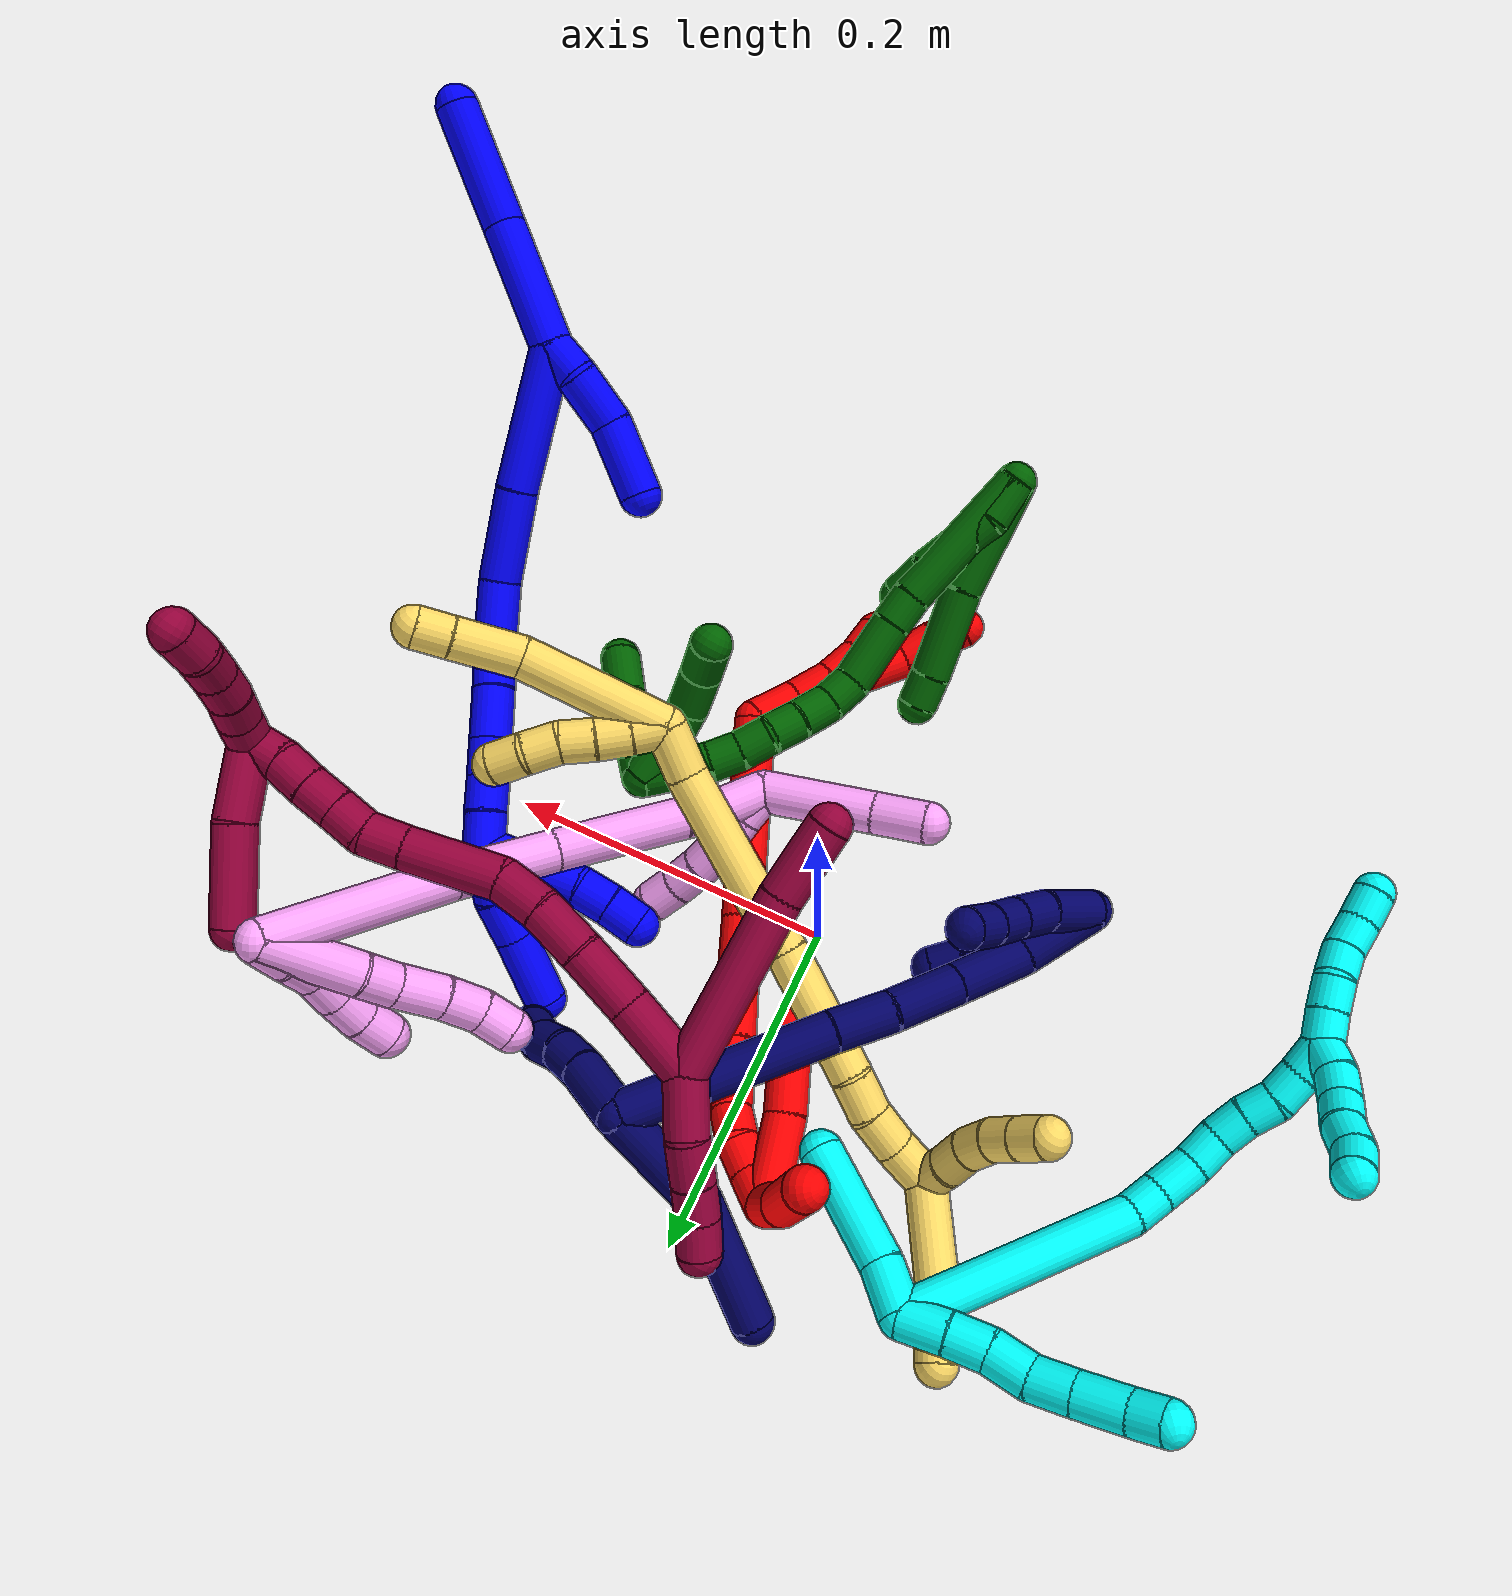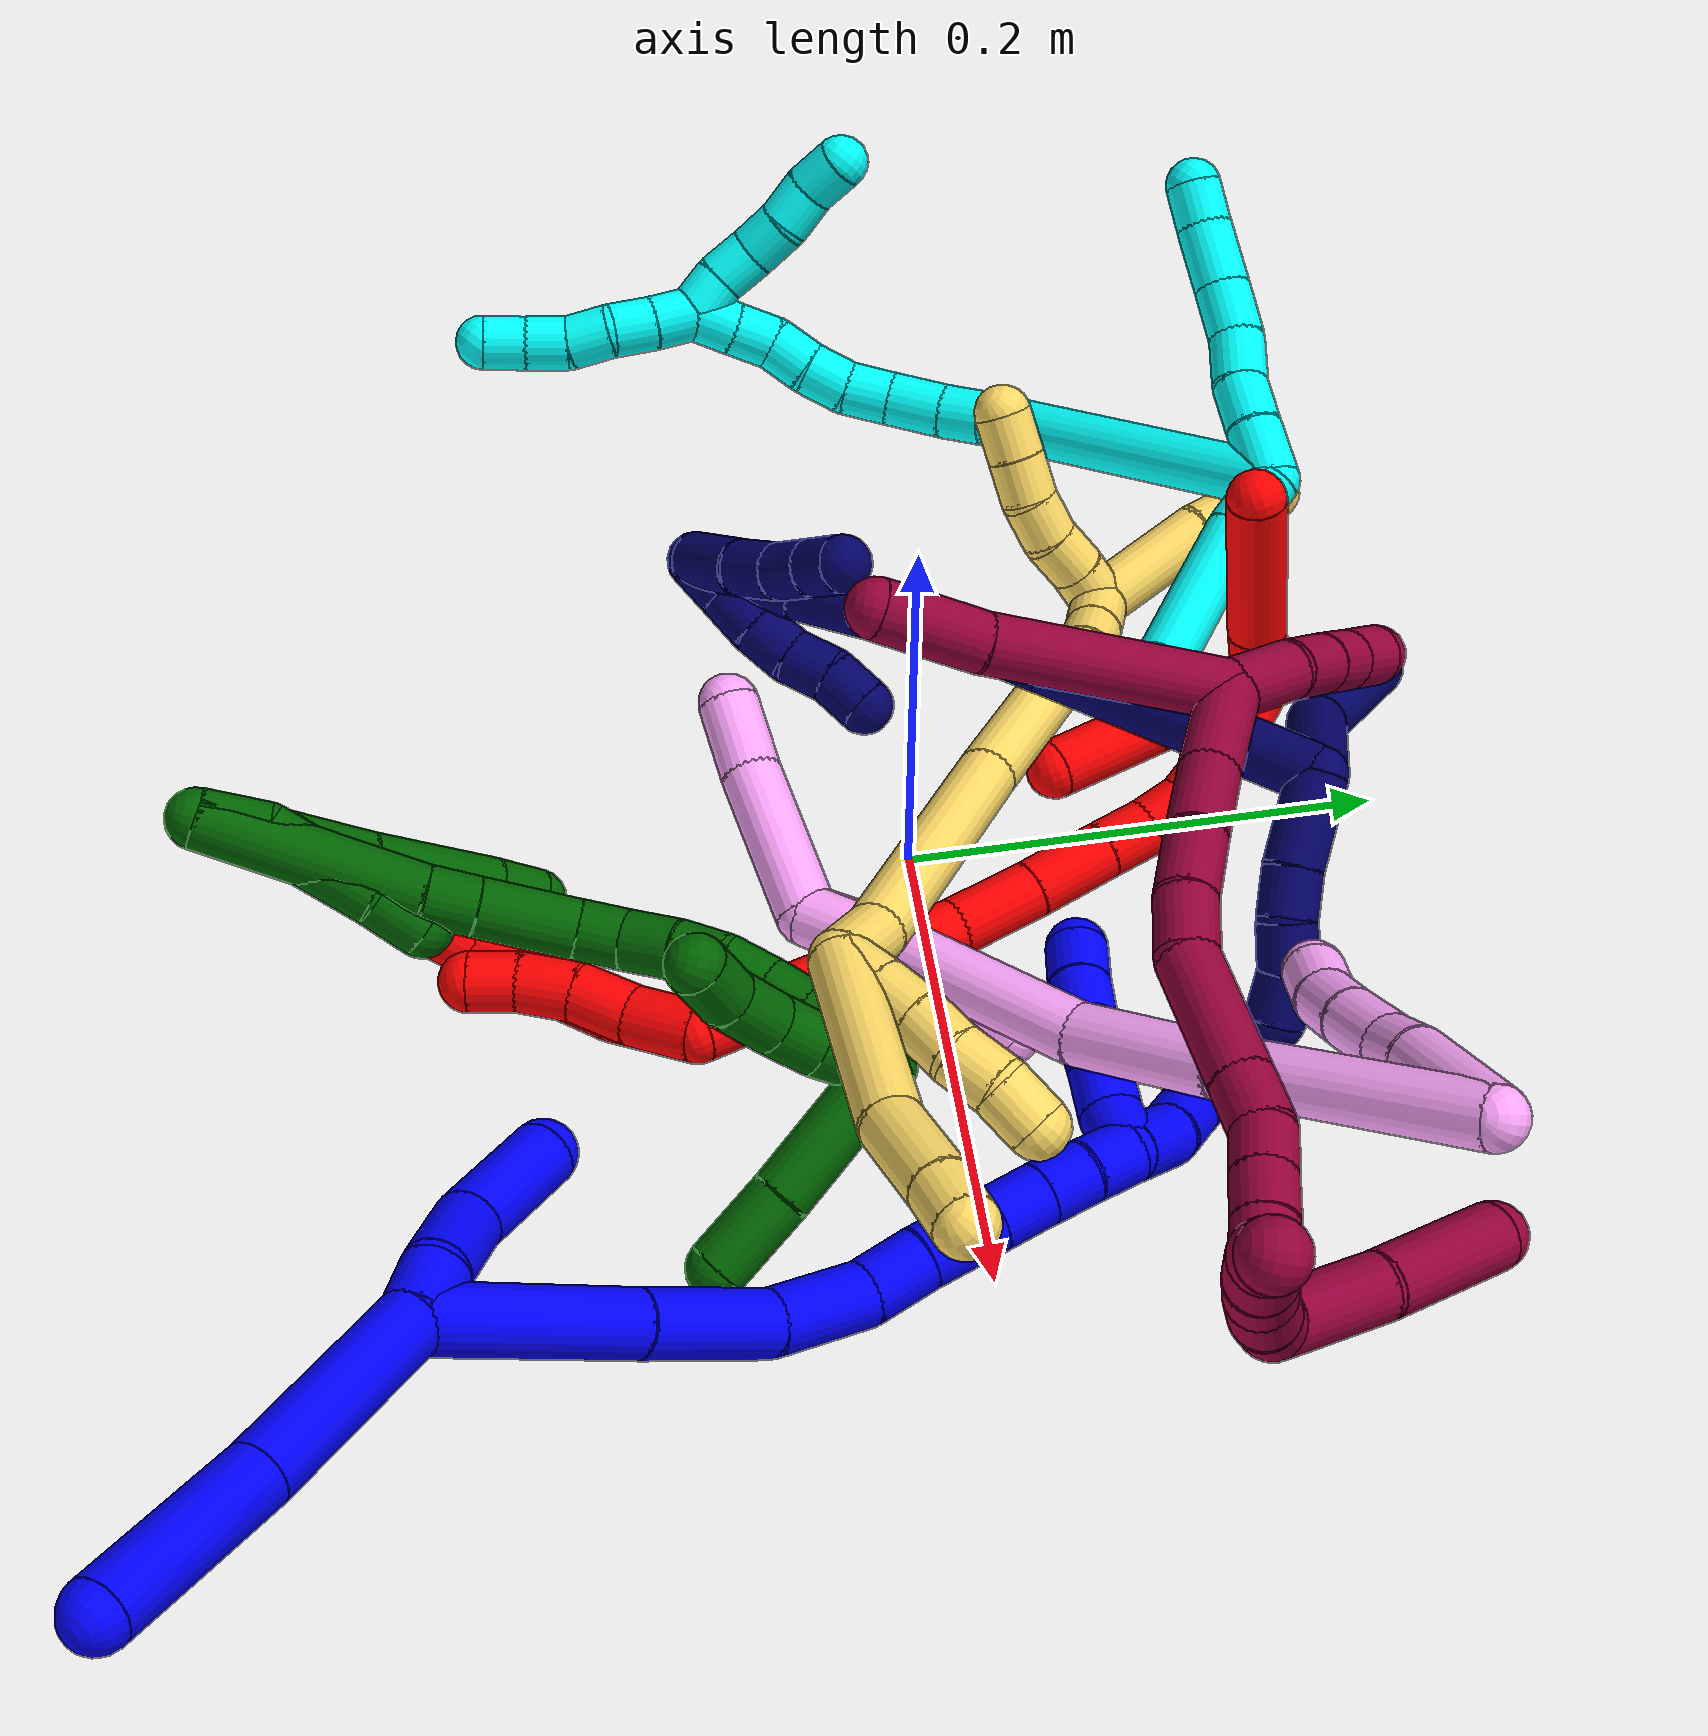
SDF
<sdf version="1.7">
 <world name="default">
  <plugin name="TubeGeneratorPlugin" filename="libtube_generator_plugin.so"/>
  <model name="photoneo_s_sensor">
   <static>1</static>
   <pose>0 0 2 1.57079 1.57079 3.14159</pose>
   <link name="link">
    <inertial><mass>0.1</mass></inertial>
    <sensor name="sensor" type="depth">
     <update_rate>30</update_rate>
     <camera>
      <horizontal_fov>1.22</horizontal_fov>
      <image><width>1920</width><height>1200</height><format>B8G8R8</format></image>
      <clip><near>0.1</near><far>4</far></clip>
      <depth_camera><output>points</output></depth_camera>
     </camera>
     <plugin name="camera_plugin" filename="libgazebo_ros_depth_camera.so">
      <baseline>0.2</baseline>
      <alwaysOn>1</alwaysOn>
      <updateRate>0.0</updateRate>
      <cameraName>camera_ir</cameraName>
      <imageTopicName>/camera/color/image_raw</imageTopicName>
      <cameraInfoTopicName>/camera/color/camera_info</cameraInfoTopicName>
      <depthImageTopicName>/camera/depth/image_raw</depthImageTopicName>
      <depthImageCameraInfoTopicName>/camera/depth/camera_info</depthImageCameraInfoTopicName>
      <pointCloudTopicName>/camera/depth/points</pointCloudTopicName>
      <frameName>fr_optical</frameName>
      <pointCloudCutoff>0.1</pointCloudCutoff>
      <pointCloudCutoffMax>2.0</pointCloudCutoffMax>
      <distortionK1>0</distortionK1>
      <distortionK2>0</distortionK2>
      <distortionK3>0</distortionK3>
      <distortionT1>0</distortionT1>
      <distortionT2>0</distortionT2>
      <CxPrime>0</CxPrime>
      <Cx>0</Cx>
      <Cy>0</Cy>
      <focalLength>0</focalLength>
      <hackBaseline>0</hackBaseline>
     </plugin>
    </sensor>
   </link>
  </model>
  <gravity>0 0 -9.8</gravity>
  <magnetic_field>6e-06 2.3e-05 -4.2e-05</magnetic_field>
  <atmosphere type="adiabatic"/>
  <physics name="default_physics" default="0" type="ode">
   <max_step_size>0.003</max_step_size>
   <real_time_factor>1</real_time_factor>
   <real_time_update_rate>1000</real_time_update_rate>
   <max_contacts>10000</max_contacts>
   <ode>
    <solver>
     <type>quick</type>
     <iters>100</iters>
     <sor>1.3</sor>
     <use_dynamic_moi_rescaling>0</use_dynamic_moi_rescaling>
    </solver>
    <constraints>
     <contact_max_correcting_vel>0</contact_max_correcting_vel>
     <contact_surface_layer>0.001</contact_surface_layer>
     <cfm>0</cfm>
     <erp>0.2</erp>
    </constraints>
   </ode>
  </physics>
  <scene><ambient>0.4 0.4 0.4 1</ambient><background>0.7 0.7 0.7 1</background><shadows>0</shadows></scene>
  <audio><device>default</device></audio>
  <spherical_coordinates>
   <surface_model>EARTH_WGS84</surface_model>
   <latitude_deg>0</latitude_deg>
   <longitude_deg>0</longitude_deg>
   <elevation>0</elevation>
   <heading_deg>0</heading_deg>
  </spherical_coordinates>
  <model name="bin">
   <static>1</static>
   <link name="bottom">
    <collision name="collision-bottom">
     <pose>0 0 -0.01 0 -0 0</pose>
     <geometry><box><size>0.8 0.6 0.02</size></box></geometry>
     <surface>
      <friction><ode><mu>100</mu><mu2>100</mu2></ode></friction>
      <contact><collide_bitmask>65535</collide_bitmask></contact>
     </surface>
    </collision>
   </link>
   <link name="west_wall">
    <collision name="collision-west_wall">
     <pose>-0.41 0 0.1 0 -0 0</pose>
     <geometry><box><size>0.02 0.6 0.2</size></box></geometry>
     <surface>
      <friction><ode><mu>100</mu><mu2>100</mu2></ode></friction>
      <contact><collide_bitmask>65535</collide_bitmask></contact>
     </surface>
    </collision>
   </link>
   <link name="east_wall">
    <collision name="collision-east_wall">
     <pose>0.41 0 0.1 0 -0 0</pose>
     <geometry><box><size>0.02 0.6 0.2</size></box></geometry>
     <surface>
      <friction><ode><mu>100</mu><mu2>100</mu2></ode></friction>
      <contact><collide_bitmask>65535</collide_bitmask></contact>
     </surface>
    </collision>
   </link>
   <link name="south_wall">
    <collision name="collision-south_wall">
     <pose>0 -0.31 0.1 0 -0 0</pose>
     <geometry><box><size>0.8 0.02 0.2</size></box></geometry>
     <surface>
      <friction><ode><mu>100</mu><mu2>100</mu2></ode></friction>
      <contact><collide_bitmask>65535</collide_bitmask></contact>
     </surface>
    </collision>
   </link>
   <link name="north_wall">
    <collision name="collision-north_wall">
     <pose>0 0.31 0.1 0 -0 0</pose>
     <geometry><box><size>0.8 0.02 0.2</size></box></geometry>
     <surface>
      <friction><ode><mu>100</mu><mu2>100</mu2></ode></friction>
      <contact><collide_bitmask>65535</collide_bitmask></contact>
     </surface>
    </collision>
   </link>
  </model>
  <model name="1">
   <static>0</static>
   <link name="1">
    <collision name="collision-cylinder-e_1_2_8">
     <pose>0.005627 0.000156 0.038166 -0.004094 0.146383 -0.0003</pose>
     <geometry><cylinder><radius>0.0125</radius><length>0.077158</length></cylinder></geometry>
     <surface>
      <friction><ode><mu>1.16</mu><mu2>1.16</mu2><slip1>0</slip1><slip2>0</slip2></ode></friction>
      <contact><ode><kp>1e+06</kp><kd>1</kd><max_vel>0</max_vel><min_depth>0.001</min_depth></ode></contact>
     </surface>
    </collision>
    <visual name="visual-cylinder-e_1_2_8">
     <pose>0.005627 0.000156 0.038166 -0.004094 0.146383 -0.0003</pose>
     <geometry><cylinder><radius>0.0125</radius><length>0.077158</length></cylinder></geometry>
     <material><ambient>0 0 1 1</ambient></material>
    </visual>
    <collision name="collision-cylinder-e_2_8_6">
     <pose>0.009991 0.000725 0.112729 -0.011325 -0.034686 0.000196</pose>
     <geometry><cylinder><radius>0.0125</radius><length>0.072842</length></cylinder></geometry>
     <surface>
      <friction><ode><mu>1.16</mu><mu2>1.16</mu2><slip1>0</slip1><slip2>0</slip2></ode></friction>
      <contact><ode><kp>1e+06</kp><kd>1</kd><max_vel>0</max_vel><min_depth>0.001</min_depth></ode></contact>
     </surface>
    </collision>
    <visual name="visual-cylinder-e_2_8_6">
     <pose>0.009991 0.000725 0.112729 -0.011325 -0.034686 0.000196</pose>
     <geometry><cylinder><radius>0.0125</radius><length>0.072842</length></cylinder></geometry>
     <material><ambient>0 0 1 1</ambient></material>
    </visual>
    <collision name="collision-cylinder-e_1_2_9">
     <pose>-0.000781 -0.00358 -0.010108 2.80125 -0.072737 -0.41732</pose>
     <geometry><cylinder><radius>0.0125</radius><length>0.021504</length></cylinder></geometry>
     <surface>
      <friction><ode><mu>1.16</mu><mu2>1.16</mu2><slip1>0</slip1><slip2>0</slip2></ode></friction>
      <contact><ode><kp>1e+06</kp><kd>1</kd><max_vel>0</max_vel><min_depth>0.001</min_depth></ode></contact>
     </surface>
    </collision>
    <visual name="visual-cylinder-e_1_2_9">
     <pose>-0.000781 -0.00358 -0.010108 2.80125 -0.072737 -0.41732</pose>
     <geometry><cylinder><radius>0.0125</radius><length>0.021504</length></cylinder></geometry>
     <material><ambient>0 0 1 1</ambient></material>
    </visual>
    <collision name="collision-cylinder-e_2_9_10">
     <pose>0.001791 -0.011644 -0.035905 2.86312 0.202725 1.25563</pose>
     <geometry><cylinder><radius>0.0125</radius><length>0.033315</length></cylinder></geometry>
     <surface>
      <friction><ode><mu>1.16</mu><mu2>1.16</mu2><slip1>0</slip1><slip2>0</slip2></ode></friction>
      <contact><ode><kp>1e+06</kp><kd>1</kd><max_vel>0</max_vel><min_depth>0.001</min_depth></ode></contact>
     </surface>
    </collision>
    <visual name="visual-cylinder-e_2_9_10">
     <pose>0.001791 -0.011644 -0.035905 2.86312 0.202725 1.25563</pose>
     <geometry><cylinder><radius>0.0125</radius><length>0.033315</length></cylinder></geometry>
     <material><ambient>0 0 1 1</ambient></material>
    </visual>
    <collision name="collision-cylinder-e_3_10_5">
     <pose>0.004799 -0.016719 -0.074173 3.1155 -0.015329 -1.06217</pose>
     <geometry><cylinder><radius>0.0125</radius><length>0.045181</length></cylinder></geometry>
     <surface>
      <friction><ode><mu>1.16</mu><mu2>1.16</mu2><slip1>0</slip1><slip2>0</slip2></ode></friction>
      <contact><ode><kp>1e+06</kp><kd>1</kd><max_vel>0</max_vel><min_depth>0.001</min_depth></ode></contact>
     </surface>
    </collision>
    <visual name="visual-cylinder-e_3_10_5">
     <pose>0.004799 -0.016719 -0.074173 3.1155 -0.015329 -1.06217</pose>
     <geometry><cylinder><radius>0.0125</radius><length>0.045181</length></cylinder></geometry>
     <material><ambient>0 0 1 1</ambient></material>
    </visual>
    <collision name="collision-cylinder-e_1_2_11">
     <pose>0.008466 0.024117 -0.033614 -2.51924 0.201858 -0.610099</pose>
     <geometry><cylinder><radius>0.0125</radius><length>0.084456</length></cylinder></geometry>
     <surface>
      <friction><ode><mu>1.16</mu><mu2>1.16</mu2><slip1>0</slip1><slip2>0</slip2></ode></friction>
      <contact><ode><kp>1e+06</kp><kd>1</kd><max_vel>0</max_vel><min_depth>0.001</min_depth></ode></contact>
     </surface>
    </collision>
    <visual name="visual-cylinder-e_1_2_11">
     <pose>0.008466 0.024117 -0.033614 -2.51924 0.201858 -0.610099</pose>
     <geometry><cylinder><radius>0.0125</radius><length>0.084456</length></cylinder></geometry>
     <material><ambient>0 0 1 1</ambient></material>
    </visual>
    <collision name="collision-cylinder-e_2_11_12">
     <pose>0.023219 0.062737 -0.089914 -2.5728 0.229369 -0.750735</pose>
     <geometry><cylinder><radius>0.0125</radius><length>0.055299</length></cylinder></geometry>
     <surface>
      <friction><ode><mu>1.16</mu><mu2>1.16</mu2><slip1>0</slip1><slip2>0</slip2></ode></friction>
      <contact><ode><kp>1e+06</kp><kd>1</kd><max_vel>0</max_vel><min_depth>0.001</min_depth></ode></contact>
     </surface>
    </collision>
    <visual name="visual-cylinder-e_2_11_12">
     <pose>0.023219 0.062737 -0.089914 -2.5728 0.229369 -0.750735</pose>
     <geometry><cylinder><radius>0.0125</radius><length>0.055299</length></cylinder></geometry>
     <material><ambient>0 0 1 1</ambient></material>
    </visual>
    <collision name="collision-cylinder-e_3_12_13">
     <pose>0.029177 0.085953 -0.130864 -2.69642 -0.016238 0.071714</pose>
     <geometry><cylinder><radius>0.0125</radius><length>0.040478</length></cylinder></geometry>
     <surface>
      <friction><ode><mu>1.16</mu><mu2>1.16</mu2><slip1>0</slip1><slip2>0</slip2></ode></friction>
      <contact><ode><kp>1e+06</kp><kd>1</kd><max_vel>0</max_vel><min_depth>0.001</min_depth></ode></contact>
     </surface>
    </collision>
    <visual name="visual-cylinder-e_3_12_13">
     <pose>0.029177 0.085953 -0.130864 -2.69642 -0.016238 0.071714</pose>
     <geometry><cylinder><radius>0.0125</radius><length>0.040478</length></cylinder></geometry>
     <material><ambient>0 0 1 1</ambient></material>
    </visual>
    <collision name="collision-cylinder-e_4_13_14">
     <pose>0.024793 0.098941 -0.160285 -2.77576 -0.327204 1.45717</pose>
     <geometry><cylinder><radius>0.0125</radius><length>0.025233</length></cylinder></geometry>
     <surface>
      <friction><ode><mu>1.16</mu><mu2>1.16</mu2><slip1>0</slip1><slip2>0</slip2></ode></friction>
      <contact><ode><kp>1e+06</kp><kd>1</kd><max_vel>0</max_vel><min_depth>0.001</min_depth></ode></contact>
     </surface>
    </collision>
    <visual name="visual-cylinder-e_4_13_14">
     <pose>0.024793 0.098941 -0.160285 -2.77576 -0.327204 1.45717</pose>
     <geometry><cylinder><radius>0.0125</radius><length>0.025233</length></cylinder></geometry>
     <material><ambient>0 0 1 1</ambient></material>
    </visual>
    <collision name="collision-cylinder-e_5_14_15">
     <pose>0.016494 0.109165 -0.185287 -2.73567 -0.27454 1.18234</pose>
     <geometry><cylinder><radius>0.0125</radius><length>0.031312</length></cylinder></geometry>
     <surface>
      <friction><ode><mu>1.16</mu><mu2>1.16</mu2><slip1>0</slip1><slip2>0</slip2></ode></friction>
      <contact><ode><kp>1e+06</kp><kd>1</kd><max_vel>0</max_vel><min_depth>0.001</min_depth></ode></contact>
     </surface>
    </collision>
    <visual name="visual-cylinder-e_5_14_15">
     <pose>0.016494 0.109165 -0.185287 -2.73567 -0.27454 1.18234</pose>
     <geometry><cylinder><radius>0.0125</radius><length>0.031312</length></cylinder></geometry>
     <material><ambient>0 0 1 1</ambient></material>
    </visual>
    <collision name="collision-cylinder-e_6_15_16">
     <pose>0.009249 0.119302 -0.208884 -2.73613 -0.275505 1.1867</pose>
     <geometry><cylinder><radius>0.0125</radius><length>0.022058</length></cylinder></geometry>
     <surface>
      <friction><ode><mu>1.16</mu><mu2>1.16</mu2><slip1>0</slip1><slip2>0</slip2></ode></friction>
      <contact><ode><kp>1e+06</kp><kd>1</kd><max_vel>0</max_vel><min_depth>0.001</min_depth></ode></contact>
     </surface>
    </collision>
    <visual name="visual-cylinder-e_6_15_16">
     <pose>0.009249 0.119302 -0.208884 -2.73613 -0.275505 1.1867</pose>
     <geometry><cylinder><radius>0.0125</radius><length>0.022058</length></cylinder></geometry>
     <material><ambient>0 0 1 1</ambient></material>
    </visual>
    <collision name="collision-cylinder-e_7_16_17">
     <pose>0.003598 0.12755 -0.227621 -2.71705 -0.262666 1.0997</pose>
     <geometry><cylinder><radius>0.0125</radius><length>0.020421</length></cylinder></geometry>
     <surface>
      <friction><ode><mu>1.16</mu><mu2>1.16</mu2><slip1>0</slip1><slip2>0</slip2></ode></friction>
      <contact><ode><kp>1e+06</kp><kd>1</kd><max_vel>0</max_vel><min_depth>0.001</min_depth></ode></contact>
     </surface>
    </collision>
    <visual name="visual-cylinder-e_7_16_17">
     <pose>0.003598 0.12755 -0.227621 -2.71705 -0.262666 1.0997</pose>
     <geometry><cylinder><radius>0.0125</radius><length>0.020421</length></cylinder></geometry>
     <material><ambient>0 0 1 1</ambient></material>
    </visual>
    <collision name="collision-cylinder-e_8_17_1">
     <pose>-0.000656 0.135447 -0.246108 -2.75789 -0.155151 0.761321</pose>
     <geometry><cylinder><radius>0.0125</radius><length>0.020743</length></cylinder></geometry>
     <surface>
      <friction><ode><mu>1.16</mu><mu2>1.16</mu2><slip1>0</slip1><slip2>0</slip2></ode></friction>
      <contact><ode><kp>1e+06</kp><kd>1</kd><max_vel>0</max_vel><min_depth>0.001</min_depth></ode></contact>
     </surface>
    </collision>
    <visual name="visual-cylinder-e_8_17_1">
     <pose>-0.000656 0.135447 -0.246108 -2.75789 -0.155151 0.761321</pose>
     <geometry><cylinder><radius>0.0125</radius><length>0.020743</length></cylinder></geometry>
     <material><ambient>0 0 1 1</ambient></material>
    </visual>
    <collision name="collision-cylinder-e_1_1_18">
     <pose>0.00142 0.141969 -0.270213 -2.95974 0.242848 -1.85817</pose>
     <geometry><cylinder><radius>0.0125</radius><length>0.030594</length></cylinder></geometry>
     <surface>
      <friction><ode><mu>1.16</mu><mu2>1.16</mu2><slip1>0</slip1><slip2>0</slip2></ode></friction>
      <contact><ode><kp>1e+06</kp><kd>1</kd><max_vel>0</max_vel><min_depth>0.001</min_depth></ode></contact>
     </surface>
    </collision>
    <visual name="visual-cylinder-e_1_1_18">
     <pose>0.00142 0.141969 -0.270213 -2.95974 0.242848 -1.85817</pose>
     <geometry><cylinder><radius>0.0125</radius><length>0.030594</length></cylinder></geometry>
     <material><ambient>0 0 1 1</ambient></material>
    </visual>
    <collision name="collision-cylinder-e_2_18_19">
     <pose>0.008158 0.143652 -0.297439 3.06239 0.23708 2.4993</pose>
     <geometry><cylinder><radius>0.0125</radius><length>0.026054</length></cylinder></geometry>
     <surface>
      <friction><ode><mu>1.16</mu><mu2>1.16</mu2><slip1>0</slip1><slip2>0</slip2></ode></friction>
      <contact><ode><kp>1e+06</kp><kd>1</kd><max_vel>0</max_vel><min_depth>0.001</min_depth></ode></contact>
     </surface>
    </collision>
    <visual name="visual-cylinder-e_2_18_19">
     <pose>0.008158 0.143652 -0.297439 3.06239 0.23708 2.4993</pose>
     <geometry><cylinder><radius>0.0125</radius><length>0.026054</length></cylinder></geometry>
     <material><ambient>0 0 1 1</ambient></material>
    </visual>
    <collision name="collision-cylinder-e_3_19_4">
     <pose>0.015405 0.141645 -0.331306 3.09431 0.194404 2.66575</pose>
     <geometry><cylinder><radius>0.0125</radius><length>0.043352</length></cylinder></geometry>
     <surface>
      <friction><ode><mu>1.16</mu><mu2>1.16</mu2><slip1>0</slip1><slip2>0</slip2></ode></friction>
      <contact><ode><kp>1e+06</kp><kd>1</kd><max_vel>0</max_vel><min_depth>0.001</min_depth></ode></contact>
     </surface>
    </collision>
    <visual name="visual-cylinder-e_3_19_4">
     <pose>0.015405 0.141645 -0.331306 3.09431 0.194404 2.66575</pose>
     <geometry><cylinder><radius>0.0125</radius><length>0.043352</length></cylinder></geometry>
     <material><ambient>0 0 1 1</ambient></material>
    </visual>
    <collision name="collision-cylinder-e_1_1_20">
     <pose>-0.001922 0.131986 -0.262439 2.32308 0.033655 0.077559</pose>
     <geometry><cylinder><radius>0.0125</radius><length>0.02</length></cylinder></geometry>
     <surface>
      <friction><ode><mu>1.16</mu><mu2>1.16</mu2><slip1>0</slip1><slip2>0</slip2></ode></friction>
      <contact><ode><kp>1e+06</kp><kd>1</kd><max_vel>0</max_vel><min_depth>0.001</min_depth></ode></contact>
     </surface>
    </collision>
    <visual name="visual-cylinder-e_1_1_20">
     <pose>-0.001922 0.131986 -0.262439 2.32308 0.033655 0.077559</pose>
     <geometry><cylinder><radius>0.0125</radius><length>0.02</length></cylinder></geometry>
     <material><ambient>0 0 1 1</ambient></material>
    </visual>
    <collision name="collision-cylinder-e_2_20_21">
     <pose>-0.004519 0.117653 -0.275741 2.31452 -0.297687 -0.658527</pose>
     <geometry><cylinder><radius>0.0125</radius><length>0.02</length></cylinder></geometry>
     <surface>
      <friction><ode><mu>1.16</mu><mu2>1.16</mu2><slip1>0</slip1><slip2>0</slip2></ode></friction>
      <contact><ode><kp>1e+06</kp><kd>1</kd><max_vel>0</max_vel><min_depth>0.001</min_depth></ode></contact>
     </surface>
    </collision>
    <visual name="visual-cylinder-e_2_20_21">
     <pose>-0.004519 0.117653 -0.275741 2.31452 -0.297687 -0.658527</pose>
     <geometry><cylinder><radius>0.0125</radius><length>0.02</length></cylinder></geometry>
     <material><ambient>0 0 1 1</ambient></material>
    </visual>
    <collision name="collision-cylinder-e_3_21_22">
     <pose>-0.009743 0.103375 -0.288717 2.30256 -0.231166 -0.509338</pose>
     <geometry><cylinder><radius>0.0125</radius><length>0.02</length></cylinder></geometry>
     <surface>
      <friction><ode><mu>1.16</mu><mu2>1.16</mu2><slip1>0</slip1><slip2>0</slip2></ode></friction>
      <contact><ode><kp>1e+06</kp><kd>1</kd><max_vel>0</max_vel><min_depth>0.001</min_depth></ode></contact>
     </surface>
    </collision>
    <visual name="visual-cylinder-e_3_21_22">
     <pose>-0.009743 0.103375 -0.288717 2.30256 -0.231166 -0.509338</pose>
     <geometry><cylinder><radius>0.0125</radius><length>0.02</length></cylinder></geometry>
     <material><ambient>0 0 1 1</ambient></material>
    </visual>
    <collision name="collision-cylinder-e_4_22_23">
     <pose>-0.013072 0.089998 -0.30305 2.47683 -0.103997 -0.299295</pose>
     <geometry><cylinder><radius>0.0125</radius><length>0.02</length></cylinder></geometry>
     <surface>
      <friction><ode><mu>1.16</mu><mu2>1.16</mu2><slip1>0</slip1><slip2>0</slip2></ode></friction>
      <contact><ode><kp>1e+06</kp><kd>1</kd><max_vel>0</max_vel><min_depth>0.001</min_depth></ode></contact>
     </surface>
    </collision>
    <visual name="visual-cylinder-e_4_22_23">
     <pose>-0.013072 0.089998 -0.30305 2.47683 -0.103997 -0.299295</pose>
     <geometry><cylinder><radius>0.0125</radius><length>0.02</length></cylinder></geometry>
     <material><ambient>0 0 1 1</ambient></material>
    </visual>
    <collision name="collision-cylinder-e_5_23_3">
     <pose>-0.014924 0.078377 -0.319199 2.5588 -0.081413 -0.269934</pose>
     <geometry><cylinder><radius>0.0125</radius><length>0.02</length></cylinder></geometry>
     <surface>
      <friction><ode><mu>1.16</mu><mu2>1.16</mu2><slip1>0</slip1><slip2>0</slip2></ode></friction>
      <contact><ode><kp>1e+06</kp><kd>1</kd><max_vel>0</max_vel><min_depth>0.001</min_depth></ode></contact>
     </surface>
    </collision>
    <visual name="visual-cylinder-e_5_23_3">
     <pose>-0.014924 0.078377 -0.319199 2.5588 -0.081413 -0.269934</pose>
     <geometry><cylinder><radius>0.0125</radius><length>0.02</length></cylinder></geometry>
     <material><ambient>0 0 1 1</ambient></material>
    </visual>
    <collision name="collision-sphere-3">
     <pose>-0.015737 0.072892 -0.327521 0 -0 0</pose>
     <geometry><sphere><radius>0.0125</radius></sphere></geometry>
     <surface>
      <friction><ode><mu>1.16</mu><mu2>1.16</mu2><slip1>0</slip1><slip2>0</slip2></ode></friction>
      <contact><ode><kp>1e+06</kp><kd>1</kd><max_vel>0</max_vel><min_depth>0.001</min_depth></ode></contact>
     </surface>
    </collision>
    <visual name="visual-sphere-3">
     <pose>-0.015737 0.072892 -0.327521 0 -0 0</pose>
     <geometry><sphere><radius>0.0125</radius></sphere></geometry>
     <material><ambient>0 0 1 1</ambient></material>
    </visual>
    <collision name="collision-sphere-23">
     <pose>-0.01411 0.083862 -0.310878 0 -0 0</pose>
     <geometry><sphere><radius>0.0125</radius></sphere></geometry>
     <surface>
      <friction><ode><mu>1.16</mu><mu2>1.16</mu2><slip1>0</slip1><slip2>0</slip2></ode></friction>
      <contact><ode><kp>1e+06</kp><kd>1</kd><max_vel>0</max_vel><min_depth>0.001</min_depth></ode></contact>
     </surface>
    </collision>
    <visual name="visual-sphere-23">
     <pose>-0.01411 0.083862 -0.310878 0 -0 0</pose>
     <geometry><sphere><radius>0.0125</radius></sphere></geometry>
     <material><ambient>0 0 1 1</ambient></material>
    </visual>
    <collision name="collision-sphere-22">
     <pose>-0.012034 0.096133 -0.295222 0 -0 0</pose>
     <geometry><sphere><radius>0.0125</radius></sphere></geometry>
     <surface>
      <friction><ode><mu>1.16</mu><mu2>1.16</mu2><slip1>0</slip1><slip2>0</slip2></ode></friction>
      <contact><ode><kp>1e+06</kp><kd>1</kd><max_vel>0</max_vel><min_depth>0.001</min_depth></ode></contact>
     </surface>
    </collision>
    <visual name="visual-sphere-22">
     <pose>-0.012034 0.096133 -0.295222 0 -0 0</pose>
     <geometry><sphere><radius>0.0125</radius></sphere></geometry>
     <material><ambient>0 0 1 1</ambient></material>
    </visual>
    <collision name="collision-sphere-21">
     <pose>-0.007452 0.110617 -0.282213 0 -0 0</pose>
     <geometry><sphere><radius>0.0125</radius></sphere></geometry>
     <surface>
      <friction><ode><mu>1.16</mu><mu2>1.16</mu2><slip1>0</slip1><slip2>0</slip2></ode></friction>
      <contact><ode><kp>1e+06</kp><kd>1</kd><max_vel>0</max_vel><min_depth>0.001</min_depth></ode></contact>
     </surface>
    </collision>
    <visual name="visual-sphere-21">
     <pose>-0.007452 0.110617 -0.282213 0 -0 0</pose>
     <geometry><sphere><radius>0.0125</radius></sphere></geometry>
     <material><ambient>0 0 1 1</ambient></material>
    </visual>
    <collision name="collision-sphere-20">
     <pose>-0.001586 0.124689 -0.269268 0 -0 0</pose>
     <geometry><sphere><radius>0.0125</radius></sphere></geometry>
     <surface>
      <friction><ode><mu>1.16</mu><mu2>1.16</mu2><slip1>0</slip1><slip2>0</slip2></ode></friction>
      <contact><ode><kp>1e+06</kp><kd>1</kd><max_vel>0</max_vel><min_depth>0.001</min_depth></ode></contact>
     </surface>
    </collision>
    <visual name="visual-sphere-20">
     <pose>-0.001586 0.124689 -0.269268 0 -0 0</pose>
     <geometry><sphere><radius>0.0125</radius></sphere></geometry>
     <material><ambient>0 0 1 1</ambient></material>
    </visual>
    <collision name="collision-sphere-4">
     <pose>0.019592 0.14064 -0.35255 0 -0 0</pose>
     <geometry><sphere><radius>0.0125</radius></sphere></geometry>
     <surface>
      <friction><ode><mu>1.16</mu><mu2>1.16</mu2><slip1>0</slip1><slip2>0</slip2></ode></friction>
      <contact><ode><kp>1e+06</kp><kd>1</kd><max_vel>0</max_vel><min_depth>0.001</min_depth></ode></contact>
     </surface>
    </collision>
    <visual name="visual-sphere-4">
     <pose>0.019592 0.14064 -0.35255 0 -0 0</pose>
     <geometry><sphere><radius>0.0125</radius></sphere></geometry>
     <material><ambient>0 0 1 1</ambient></material>
    </visual>
    <collision name="collision-sphere-5">
     <pose>0.004452 -0.017308 -0.096753 0 -0 0</pose>
     <geometry><sphere><radius>0.0125</radius></sphere></geometry>
     <surface>
      <friction><ode><mu>1.16</mu><mu2>1.16</mu2><slip1>0</slip1><slip2>0</slip2></ode></friction>
      <contact><ode><kp>1e+06</kp><kd>1</kd><max_vel>0</max_vel><min_depth>0.001</min_depth></ode></contact>
     </surface>
    </collision>
    <visual name="visual-sphere-5">
     <pose>0.004452 -0.017308 -0.096753 0 -0 0</pose>
     <geometry><sphere><radius>0.0125</radius></sphere></geometry>
     <material><ambient>0 0 1 1</ambient></material>
    </visual>
    <collision name="collision-sphere-10">
     <pose>0.005145 -0.01613 -0.051593 0 -0 0</pose>
     <geometry><sphere><radius>0.0125</radius></sphere></geometry>
     <surface>
      <friction><ode><mu>1.16</mu><mu2>1.16</mu2><slip1>0</slip1><slip2>0</slip2></ode></friction>
      <contact><ode><kp>1e+06</kp><kd>1</kd><max_vel>0</max_vel><min_depth>0.001</min_depth></ode></contact>
     </surface>
    </collision>
    <visual name="visual-sphere-10">
     <pose>0.005145 -0.01613 -0.051593 0 -0 0</pose>
     <geometry><sphere><radius>0.0125</radius></sphere></geometry>
     <material><ambient>0 0 1 1</ambient></material>
    </visual>
    <collision name="collision-sphere-6">
     <pose>0.008728 0.001137 0.149126 0 -0 0</pose>
     <geometry><sphere><radius>0.0125</radius></sphere></geometry>
     <surface>
      <friction><ode><mu>1.16</mu><mu2>1.16</mu2><slip1>0</slip1><slip2>0</slip2></ode></friction>
      <contact><ode><kp>1e+06</kp><kd>1</kd><max_vel>0</max_vel><min_depth>0.001</min_depth></ode></contact>
     </surface>
    </collision>
    <visual name="visual-sphere-6">
     <pose>0.008728 0.001137 0.149126 0 -0 0</pose>
     <geometry><sphere><radius>0.0125</radius></sphere></geometry>
     <material><ambient>0 0 1 1</ambient></material>
    </visual>
    <collision name="collision-sphere-9">
     <pose>-0.001563 -0.007159 -0.020217 0 -0 0</pose>
     <geometry><sphere><radius>0.0125</radius></sphere></geometry>
     <surface>
      <friction><ode><mu>1.16</mu><mu2>1.16</mu2><slip1>0</slip1><slip2>0</slip2></ode></friction>
      <contact><ode><kp>1e+06</kp><kd>1</kd><max_vel>0</max_vel><min_depth>0.001</min_depth></ode></contact>
     </surface>
    </collision>
    <visual name="visual-sphere-9">
     <pose>-0.001563 -0.007159 -0.020217 0 -0 0</pose>
     <geometry><sphere><radius>0.0125</radius></sphere></geometry>
     <material><ambient>0 0 1 1</ambient></material>
    </visual>
    <collision name="collision-sphere-2">
     <geometry><sphere><radius>0.0125</radius></sphere></geometry>
     <surface>
      <friction><ode><mu>1.16</mu><mu2>1.16</mu2><slip1>0</slip1><slip2>0</slip2></ode></friction>
      <contact><ode><kp>1e+06</kp><kd>1</kd><max_vel>0</max_vel><min_depth>0.001</min_depth></ode></contact>
     </surface>
    </collision>
    <visual name="visual-sphere-2">
     <geometry><sphere><radius>0.0125</radius></sphere></geometry>
     <material><ambient>0 0 1 1</ambient></material>
    </visual>
    <collision name="collision-sphere-19">
     <pose>0.011217 0.14265 -0.310062 0 -0 0</pose>
     <geometry><sphere><radius>0.0125</radius></sphere></geometry>
     <surface>
      <friction><ode><mu>1.16</mu><mu2>1.16</mu2><slip1>0</slip1><slip2>0</slip2></ode></friction>
      <contact><ode><kp>1e+06</kp><kd>1</kd><max_vel>0</max_vel><min_depth>0.001</min_depth></ode></contact>
     </surface>
    </collision>
    <visual name="visual-sphere-19">
     <pose>0.011217 0.14265 -0.310062 0 -0 0</pose>
     <geometry><sphere><radius>0.0125</radius></sphere></geometry>
     <material><ambient>0 0 1 1</ambient></material>
    </visual>
    <collision name="collision-sphere-8">
     <pose>0.011254 0.000312 0.076332 0 -0 0</pose>
     <geometry><sphere><radius>0.0125</radius></sphere></geometry>
     <surface>
      <friction><ode><mu>1.16</mu><mu2>1.16</mu2><slip1>0</slip1><slip2>0</slip2></ode></friction>
      <contact><ode><kp>1e+06</kp><kd>1</kd><max_vel>0</max_vel><min_depth>0.001</min_depth></ode></contact>
     </surface>
    </collision>
    <visual name="visual-sphere-8">
     <pose>0.011254 0.000312 0.076332 0 -0 0</pose>
     <geometry><sphere><radius>0.0125</radius></sphere></geometry>
     <material><ambient>0 0 1 1</ambient></material>
    </visual>
    <collision name="collision-sphere-11">
     <pose>0.016933 0.048234 -0.067228 0 -0 0</pose>
     <geometry><sphere><radius>0.0125</radius></sphere></geometry>
     <surface>
      <friction><ode><mu>1.16</mu><mu2>1.16</mu2><slip1>0</slip1><slip2>0</slip2></ode></friction>
      <contact><ode><kp>1e+06</kp><kd>1</kd><max_vel>0</max_vel><min_depth>0.001</min_depth></ode></contact>
     </surface>
    </collision>
    <visual name="visual-sphere-11">
     <pose>0.016933 0.048234 -0.067228 0 -0 0</pose>
     <geometry><sphere><radius>0.0125</radius></sphere></geometry>
     <material><ambient>0 0 1 1</ambient></material>
    </visual>
    <collision name="collision-sphere-12">
     <pose>0.029505 0.077239 -0.1126 0 -0 0</pose>
     <geometry><sphere><radius>0.0125</radius></sphere></geometry>
     <surface>
      <friction><ode><mu>1.16</mu><mu2>1.16</mu2><slip1>0</slip1><slip2>0</slip2></ode></friction>
      <contact><ode><kp>1e+06</kp><kd>1</kd><max_vel>0</max_vel><min_depth>0.001</min_depth></ode></contact>
     </surface>
    </collision>
    <visual name="visual-sphere-12">
     <pose>0.029505 0.077239 -0.1126 0 -0 0</pose>
     <geometry><sphere><radius>0.0125</radius></sphere></geometry>
     <material><ambient>0 0 1 1</ambient></material>
    </visual>
    <collision name="collision-sphere-13">
     <pose>0.028848 0.094667 -0.149128 0 -0 0</pose>
     <geometry><sphere><radius>0.0125</radius></sphere></geometry>
     <surface>
      <friction><ode><mu>1.16</mu><mu2>1.16</mu2><slip1>0</slip1><slip2>0</slip2></ode></friction>
      <contact><ode><kp>1e+06</kp><kd>1</kd><max_vel>0</max_vel><min_depth>0.001</min_depth></ode></contact>
     </surface>
    </collision>
    <visual name="visual-sphere-13">
     <pose>0.028848 0.094667 -0.149128 0 -0 0</pose>
     <geometry><sphere><radius>0.0125</radius></sphere></geometry>
     <material><ambient>0 0 1 1</ambient></material>
    </visual>
    <collision name="collision-sphere-14">
     <pose>0.020738 0.103215 -0.171441 0 -0 0</pose>
     <geometry><sphere><radius>0.0125</radius></sphere></geometry>
     <surface>
      <friction><ode><mu>1.16</mu><mu2>1.16</mu2><slip1>0</slip1><slip2>0</slip2></ode></friction>
      <contact><ode><kp>1e+06</kp><kd>1</kd><max_vel>0</max_vel><min_depth>0.001</min_depth></ode></contact>
     </surface>
    </collision>
    <visual name="visual-sphere-14">
     <pose>0.020738 0.103215 -0.171441 0 -0 0</pose>
     <geometry><sphere><radius>0.0125</radius></sphere></geometry>
     <material><ambient>0 0 1 1</ambient></material>
    </visual>
    <collision name="collision-sphere-15">
     <pose>0.01225 0.115116 -0.199132 0 -0 0</pose>
     <geometry><sphere><radius>0.0125</radius></sphere></geometry>
     <surface>
      <friction><ode><mu>1.16</mu><mu2>1.16</mu2><slip1>0</slip1><slip2>0</slip2></ode></friction>
      <contact><ode><kp>1e+06</kp><kd>1</kd><max_vel>0</max_vel><min_depth>0.001</min_depth></ode></contact>
     </surface>
    </collision>
    <visual name="visual-sphere-15">
     <pose>0.01225 0.115116 -0.199132 0 -0 0</pose>
     <geometry><sphere><radius>0.0125</radius></sphere></geometry>
     <material><ambient>0 0 1 1</ambient></material>
    </visual>
    <collision name="collision-sphere-16">
     <pose>0.006249 0.123488 -0.218636 0 -0 0</pose>
     <geometry><sphere><radius>0.0125</radius></sphere></geometry>
     <surface>
      <friction><ode><mu>1.16</mu><mu2>1.16</mu2><slip1>0</slip1><slip2>0</slip2></ode></friction>
      <contact><ode><kp>1e+06</kp><kd>1</kd><max_vel>0</max_vel><min_depth>0.001</min_depth></ode></contact>
     </surface>
    </collision>
    <visual name="visual-sphere-16">
     <pose>0.006249 0.123488 -0.218636 0 -0 0</pose>
     <geometry><sphere><radius>0.0125</radius></sphere></geometry>
     <material><ambient>0 0 1 1</ambient></material>
    </visual>
    <collision name="collision-sphere-17">
     <pose>0.000947 0.131611 -0.236607 0 -0 0</pose>
     <geometry><sphere><radius>0.0125</radius></sphere></geometry>
     <surface>
      <friction><ode><mu>1.16</mu><mu2>1.16</mu2><slip1>0</slip1><slip2>0</slip2></ode></friction>
      <contact><ode><kp>1e+06</kp><kd>1</kd><max_vel>0</max_vel><min_depth>0.001</min_depth></ode></contact>
     </surface>
    </collision>
    <visual name="visual-sphere-17">
     <pose>0.000947 0.131611 -0.236607 0 -0 0</pose>
     <geometry><sphere><radius>0.0125</radius></sphere></geometry>
     <material><ambient>0 0 1 1</ambient></material>
    </visual>
    <collision name="collision-sphere-1">
     <pose>-0.002259 0.139283 -0.25561 0 -0 0</pose>
     <geometry><sphere><radius>0.0125</radius></sphere></geometry>
     <surface>
      <friction><ode><mu>1.16</mu><mu2>1.16</mu2><slip1>0</slip1><slip2>0</slip2></ode></friction>
      <contact><ode><kp>1e+06</kp><kd>1</kd><max_vel>0</max_vel><min_depth>0.001</min_depth></ode></contact>
     </surface>
    </collision>
    <visual name="visual-sphere-1">
     <pose>-0.002259 0.139283 -0.25561 0 -0 0</pose>
     <geometry><sphere><radius>0.0125</radius></sphere></geometry>
     <material><ambient>0 0 1 1</ambient></material>
    </visual>
    <collision name="collision-sphere-18">
     <pose>0.005098 0.144654 -0.284816 0 -0 0</pose>
     <geometry><sphere><radius>0.0125</radius></sphere></geometry>
     <surface>
      <friction><ode><mu>1.16</mu><mu2>1.16</mu2><slip1>0</slip1><slip2>0</slip2></ode></friction>
      <contact><ode><kp>1e+06</kp><kd>1</kd><max_vel>0</max_vel><min_depth>0.001</min_depth></ode></contact>
     </surface>
    </collision>
    <visual name="visual-sphere-18">
     <pose>0.005098 0.144654 -0.284816 0 -0 0</pose>
     <geometry><sphere><radius>0.0125</radius></sphere></geometry>
     <material><ambient>0 0 1 1</ambient></material>
    </visual>
    <inertial>
     <pose>0.008064 0.061927 -0.120381 0 -0 0</pose>
     <mass>0.75</mass>
     <inertia><ixx>0.000111</ixx><ixy>0</ixy><ixz>0</ixz><iyy>-6e-06</iyy><iyz>0</iyz><izz>-8.8e-05</izz></inertia>
    </inertial>
   </link>
   <pose>0.267872 -0.211396 0.16979 -0.125457 1.17928 -0.876311</pose>
  </model>
  <model name="2">
   <static>0</static>
   <link name="2">
    <collision name="collision-cylinder-e_1_2_8">
     <pose>-0.001607 -0.019561 0.008418 1.16441 -0.075303 -0.049587</pose>
     <geometry><cylinder><radius>0.0125</radius><length>0.042712</length></cylinder></geometry>
     <surface>
      <friction><ode><mu>1.16</mu><mu2>1.16</mu2><slip1>0</slip1><slip2>0</slip2></ode></friction>
      <contact><ode><kp>1e+06</kp><kd>1</kd><max_vel>0</max_vel><min_depth>0.001</min_depth></ode></contact>
     </surface>
    </collision>
    <visual name="visual-cylinder-e_1_2_8">
     <pose>-0.001607 -0.019561 0.008418 1.16441 -0.075303 -0.049587</pose>
     <geometry><cylinder><radius>0.0125</radius><length>0.042712</length></cylinder></geometry>
     <material><ambient>1 0 0 1</ambient></material>
    </visual>
    <collision name="collision-cylinder-e_2_8_9">
     <pose>-0.001496 -0.052231 0.027694 0.87905 0.100563 0.047316</pose>
     <geometry><cylinder><radius>0.0125</radius><length>0.034217</length></cylinder></geometry>
     <surface>
      <friction><ode><mu>1.16</mu><mu2>1.16</mu2><slip1>0</slip1><slip2>0</slip2></ode></friction>
      <contact><ode><kp>1e+06</kp><kd>1</kd><max_vel>0</max_vel><min_depth>0.001</min_depth></ode></contact>
     </surface>
    </collision>
    <visual name="visual-cylinder-e_2_8_9">
     <pose>-0.001496 -0.052231 0.027694 0.87905 0.100563 0.047316</pose>
     <geometry><cylinder><radius>0.0125</radius><length>0.034217</length></cylinder></geometry>
     <material><ambient>1 0 0 1</ambient></material>
    </visual>
    <collision name="collision-cylinder-e_3_9_10">
     <pose>-0.000375 -0.077344 0.046924 0.961768 -0.040763 -0.021269</pose>
     <geometry><cylinder><radius>0.0125</radius><length>0.029295</length></cylinder></geometry>
     <surface>
      <friction><ode><mu>1.16</mu><mu2>1.16</mu2><slip1>0</slip1><slip2>0</slip2></ode></friction>
      <contact><ode><kp>1e+06</kp><kd>1</kd><max_vel>0</max_vel><min_depth>0.001</min_depth></ode></contact>
     </surface>
    </collision>
    <visual name="visual-cylinder-e_3_9_10">
     <pose>-0.000375 -0.077344 0.046924 0.961768 -0.040763 -0.021269</pose>
     <geometry><cylinder><radius>0.0125</radius><length>0.029295</length></cylinder></geometry>
     <material><ambient>1 0 0 1</ambient></material>
    </visual>
    <collision name="collision-cylinder-e_4_10_11">
     <pose>0.001192 -0.097153 0.063892 0.737203 0.184291 0.071355</pose>
     <geometry><cylinder><radius>0.0125</radius><length>0.02362</length></cylinder></geometry>
     <surface>
      <friction><ode><mu>1.16</mu><mu2>1.16</mu2><slip1>0</slip1><slip2>0</slip2></ode></friction>
      <contact><ode><kp>1e+06</kp><kd>1</kd><max_vel>0</max_vel><min_depth>0.001</min_depth></ode></contact>
     </surface>
    </collision>
    <visual name="visual-cylinder-e_4_10_11">
     <pose>0.001192 -0.097153 0.063892 0.737203 0.184291 0.071355</pose>
     <geometry><cylinder><radius>0.0125</radius><length>0.02362</length></cylinder></geometry>
     <material><ambient>1 0 0 1</ambient></material>
    </visual>
    <collision name="collision-cylinder-e_5_11_6">
     <pose>0.003896 -0.110737 0.080727 0.611723 0.05351 0.0169</pose>
     <geometry><cylinder><radius>0.0125</radius><length>0.020156</length></cylinder></geometry>
     <surface>
      <friction><ode><mu>1.16</mu><mu2>1.16</mu2><slip1>0</slip1><slip2>0</slip2></ode></friction>
      <contact><ode><kp>1e+06</kp><kd>1</kd><max_vel>0</max_vel><min_depth>0.001</min_depth></ode></contact>
     </surface>
    </collision>
    <visual name="visual-cylinder-e_5_11_6">
     <pose>0.003896 -0.110737 0.080727 0.611723 0.05351 0.0169</pose>
     <geometry><cylinder><radius>0.0125</radius><length>0.020156</length></cylinder></geometry>
     <material><ambient>1 0 0 1</ambient></material>
    </visual>
    <collision name="collision-cylinder-e_1_2_12">
     <pose>0.000642 -0.013163 0.00691 1.08735 0.043149 0.026083</pose>
     <geometry><cylinder><radius>0.0125</radius><length>0.029761</length></cylinder></geometry>
     <surface>
      <friction><ode><mu>1.16</mu><mu2>1.16</mu2><slip1>0</slip1><slip2>0</slip2></ode></friction>
      <contact><ode><kp>1e+06</kp><kd>1</kd><max_vel>0</max_vel><min_depth>0.001</min_depth></ode></contact>
     </surface>
    </collision>
    <visual name="visual-cylinder-e_1_2_12">
     <pose>0.000642 -0.013163 0.00691 1.08735 0.043149 0.026083</pose>
     <geometry><cylinder><radius>0.0125</radius><length>0.029761</length></cylinder></geometry>
     <material><ambient>1 0 0 1</ambient></material>
    </visual>
    <collision name="collision-cylinder-e_2_12_13">
     <pose>0.002982 -0.036089 0.021792 0.886099 0.133955 0.063637</pose>
     <geometry><cylinder><radius>0.0125</radius><length>0.025436</length></cylinder></geometry>
     <surface>
      <friction><ode><mu>1.16</mu><mu2>1.16</mu2><slip1>0</slip1><slip2>0</slip2></ode></friction>
      <contact><ode><kp>1e+06</kp><kd>1</kd><max_vel>0</max_vel><min_depth>0.001</min_depth></ode></contact>
     </surface>
    </collision>
    <visual name="visual-cylinder-e_2_12_13">
     <pose>0.002982 -0.036089 0.021792 0.886099 0.133955 0.063637</pose>
     <geometry><cylinder><radius>0.0125</radius><length>0.025436</length></cylinder></geometry>
     <material><ambient>1 0 0 1</ambient></material>
    </visual>
    <collision name="collision-cylinder-e_3_13_14">
     <pose>0.008136 -0.055733 0.03561 1.03651 0.29235 0.167516</pose>
     <geometry><cylinder><radius>0.0125</radius><length>0.02398</length></cylinder></geometry>
     <surface>
      <friction><ode><mu>1.16</mu><mu2>1.16</mu2><slip1>0</slip1><slip2>0</slip2></ode></friction>
      <contact><ode><kp>1e+06</kp><kd>1</kd><max_vel>0</max_vel><min_depth>0.001</min_depth></ode></contact>
     </surface>
    </collision>
    <visual name="visual-cylinder-e_3_13_14">
     <pose>0.008136 -0.055733 0.03561 1.03651 0.29235 0.167516</pose>
     <geometry><cylinder><radius>0.0125</radius><length>0.02398</length></cylinder></geometry>
     <material><ambient>1 0 0 1</ambient></material>
    </visual>
    <collision name="collision-cylinder-e_4_14_5">
     <pose>0.016338 -0.074055 0.045282 1.14529 0.473337 0.308521</pose>
     <geometry><cylinder><radius>0.0125</radius><length>0.020823</length></cylinder></geometry>
     <surface>
      <friction><ode><mu>1.16</mu><mu2>1.16</mu2><slip1>0</slip1><slip2>0</slip2></ode></friction>
      <contact><ode><kp>1e+06</kp><kd>1</kd><max_vel>0</max_vel><min_depth>0.001</min_depth></ode></contact>
     </surface>
    </collision>
    <visual name="visual-cylinder-e_4_14_5">
     <pose>0.016338 -0.074055 0.045282 1.14529 0.473337 0.308521</pose>
     <geometry><cylinder><radius>0.0125</radius><length>0.020823</length></cylinder></geometry>
     <material><ambient>1 0 0 1</ambient></material>
    </visual>
    <collision name="collision-cylinder-e_1_2_15">
     <pose>-0.051708 0.031954 -0.004047 -1.69677 -1.01371 1.12435</pose>
     <geometry><cylinder><radius>0.0125</radius><length>0.121838</length></cylinder></geometry>
     <surface>
      <friction><ode><mu>1.16</mu><mu2>1.16</mu2><slip1>0</slip1><slip2>0</slip2></ode></friction>
      <contact><ode><kp>1e+06</kp><kd>1</kd><max_vel>0</max_vel><min_depth>0.001</min_depth></ode></contact>
     </surface>
    </collision>
    <visual name="visual-cylinder-e_1_2_15">
     <pose>-0.051708 0.031954 -0.004047 -1.69677 -1.01371 1.12435</pose>
     <geometry><cylinder><radius>0.0125</radius><length>0.121838</length></cylinder></geometry>
     <material><ambient>1 0 0 1</ambient></material>
    </visual>
    <collision name="collision-cylinder-e_2_15_16">
     <pose>-0.118002 0.075499 -0.007624 -1.53033 -0.89891 0.867633</pose>
     <geometry><cylinder><radius>0.0125</radius><length>0.037276</length></cylinder></geometry>
     <surface>
      <friction><ode><mu>1.16</mu><mu2>1.16</mu2><slip1>0</slip1><slip2>0</slip2></ode></friction>
      <contact><ode><kp>1e+06</kp><kd>1</kd><max_vel>0</max_vel><min_depth>0.001</min_depth></ode></contact>
     </surface>
    </collision>
    <visual name="visual-cylinder-e_2_15_16">
     <pose>-0.118002 0.075499 -0.007624 -1.53033 -0.89891 0.867633</pose>
     <geometry><cylinder><radius>0.0125</radius><length>0.037276</length></cylinder></geometry>
     <material><ambient>1 0 0 1</ambient></material>
    </visual>
    <collision name="collision-cylinder-e_3_16_17">
     <pose>-0.146626 0.09827 -0.006005 -1.46828 -0.895691 0.818123</pose>
     <geometry><cylinder><radius>0.0125</radius><length>0.035962</length></cylinder></geometry>
     <surface>
      <friction><ode><mu>1.16</mu><mu2>1.16</mu2><slip1>0</slip1><slip2>0</slip2></ode></friction>
      <contact><ode><kp>1e+06</kp><kd>1</kd><max_vel>0</max_vel><min_depth>0.001</min_depth></ode></contact>
     </surface>
    </collision>
    <visual name="visual-cylinder-e_3_16_17">
     <pose>-0.146626 0.09827 -0.006005 -1.46828 -0.895691 0.818123</pose>
     <geometry><cylinder><radius>0.0125</radius><length>0.035962</length></cylinder></geometry>
     <material><ambient>1 0 0 1</ambient></material>
    </visual>
    <collision name="collision-cylinder-e_4_17_18">
     <pose>-0.169441 0.116522 -0.004281 -1.48992 -0.890958 0.829609</pose>
     <geometry><cylinder><radius>0.0125</radius><length>0.022574</length></cylinder></geometry>
     <surface>
      <friction><ode><mu>1.16</mu><mu2>1.16</mu2><slip1>0</slip1><slip2>0</slip2></ode></friction>
      <contact><ode><kp>1e+06</kp><kd>1</kd><max_vel>0</max_vel><min_depth>0.001</min_depth></ode></contact>
     </surface>
    </collision>
    <visual name="visual-cylinder-e_4_17_18">
     <pose>-0.169441 0.116522 -0.004281 -1.48992 -0.890958 0.829609</pose>
     <geometry><cylinder><radius>0.0125</radius><length>0.022574</length></cylinder></geometry>
     <material><ambient>1 0 0 1</ambient></material>
    </visual>
    <collision name="collision-cylinder-e_5_18_19">
     <pose>-0.185245 0.130526 -0.002013 -1.33094 -0.777671 0.622259</pose>
     <geometry><cylinder><radius>0.0125</radius><length>0.02003</length></cylinder></geometry>
     <surface>
      <friction><ode><mu>1.16</mu><mu2>1.16</mu2><slip1>0</slip1><slip2>0</slip2></ode></friction>
      <contact><ode><kp>1e+06</kp><kd>1</kd><max_vel>0</max_vel><min_depth>0.001</min_depth></ode></contact>
     </surface>
    </collision>
    <visual name="visual-cylinder-e_5_18_19">
     <pose>-0.185245 0.130526 -0.002013 -1.33094 -0.777671 0.622259</pose>
     <geometry><cylinder><radius>0.0125</radius><length>0.02003</length></cylinder></geometry>
     <material><ambient>1 0 0 1</ambient></material>
    </visual>
    <collision name="collision-cylinder-e_6_19_20">
     <pose>-0.198359 0.144152 0.004599 -0.937304 -0.632465 0.328335</pose>
     <geometry><cylinder><radius>0.0125</radius><length>0.020595</length></cylinder></geometry>
     <surface>
      <friction><ode><mu>1.16</mu><mu2>1.16</mu2><slip1>0</slip1><slip2>0</slip2></ode></friction>
      <contact><ode><kp>1e+06</kp><kd>1</kd><max_vel>0</max_vel><min_depth>0.001</min_depth></ode></contact>
     </surface>
    </collision>
    <visual name="visual-cylinder-e_6_19_20">
     <pose>-0.198359 0.144152 0.004599 -0.937304 -0.632465 0.328335</pose>
     <geometry><cylinder><radius>0.0125</radius><length>0.020595</length></cylinder></geometry>
     <material><ambient>1 0 0 1</ambient></material>
    </visual>
    <collision name="collision-cylinder-e_7_20_21">
     <pose>-0.212546 0.154779 0.014173 -0.701271 -0.925662 0.36103</pose>
     <geometry><cylinder><radius>0.0125</radius><length>0.020273</length></cylinder></geometry>
     <surface>
      <friction><ode><mu>1.16</mu><mu2>1.16</mu2><slip1>0</slip1><slip2>0</slip2></ode></friction>
      <contact><ode><kp>1e+06</kp><kd>1</kd><max_vel>0</max_vel><min_depth>0.001</min_depth></ode></contact>
     </surface>
    </collision>
    <visual name="visual-cylinder-e_7_20_21">
     <pose>-0.212546 0.154779 0.014173 -0.701271 -0.925662 0.36103</pose>
     <geometry><cylinder><radius>0.0125</radius><length>0.020273</length></cylinder></geometry>
     <material><ambient>1 0 0 1</ambient></material>
    </visual>
    <collision name="collision-cylinder-e_8_21_1">
     <pose>-0.227107 0.164252 0.025357 -0.70378 -0.64654 0.244792</pose>
     <geometry><cylinder><radius>0.0125</radius><length>0.021451</length></cylinder></geometry>
     <surface>
      <friction><ode><mu>1.16</mu><mu2>1.16</mu2><slip1>0</slip1><slip2>0</slip2></ode></friction>
      <contact><ode><kp>1e+06</kp><kd>1</kd><max_vel>0</max_vel><min_depth>0.001</min_depth></ode></contact>
     </surface>
    </collision>
    <visual name="visual-cylinder-e_8_21_1">
     <pose>-0.227107 0.164252 0.025357 -0.70378 -0.64654 0.244792</pose>
     <geometry><cylinder><radius>0.0125</radius><length>0.021451</length></cylinder></geometry>
     <material><ambient>1 0 0 1</ambient></material>
    </visual>
    <collision name="collision-cylinder-e_1_1_22">
     <pose>-0.216395 0.151069 0.032842 1.51961 0.741597 0.707661</pose>
     <geometry><cylinder><radius>0.0125</radius><length>0.050847</length></cylinder></geometry>
     <surface>
      <friction><ode><mu>1.16</mu><mu2>1.16</mu2><slip1>0</slip1><slip2>0</slip2></ode></friction>
      <contact><ode><kp>1e+06</kp><kd>1</kd><max_vel>0</max_vel><min_depth>0.001</min_depth></ode></contact>
     </surface>
    </collision>
    <visual name="visual-cylinder-e_1_1_22">
     <pose>-0.216395 0.151069 0.032842 1.51961 0.741597 0.707661</pose>
     <geometry><cylinder><radius>0.0125</radius><length>0.050847</length></cylinder></geometry>
     <material><ambient>1 0 0 1</ambient></material>
    </visual>
    <collision name="collision-cylinder-e_2_22_4">
     <pose>-0.179421 0.117793 0.034103 1.55009 0.936903 0.920317</pose>
     <geometry><cylinder><radius>0.0125</radius><length>0.049153</length></cylinder></geometry>
     <surface>
      <friction><ode><mu>1.16</mu><mu2>1.16</mu2><slip1>0</slip1><slip2>0</slip2></ode></friction>
      <contact><ode><kp>1e+06</kp><kd>1</kd><max_vel>0</max_vel><min_depth>0.001</min_depth></ode></contact>
     </surface>
    </collision>
    <visual name="visual-cylinder-e_2_22_4">
     <pose>-0.179421 0.117793 0.034103 1.55009 0.936903 0.920317</pose>
     <geometry><cylinder><radius>0.0125</radius><length>0.049153</length></cylinder></geometry>
     <material><ambient>1 0 0 1</ambient></material>
    </visual>
    <collision name="collision-cylinder-e_1_1_23">
     <pose>-0.230152 0.174949 0.043451 -0.419395 0.26344 -0.056379</pose>
     <geometry><cylinder><radius>0.0125</radius><length>0.026237</length></cylinder></geometry>
     <surface>
      <friction><ode><mu>1.16</mu><mu2>1.16</mu2><slip1>0</slip1><slip2>0</slip2></ode></friction>
      <contact><ode><kp>1e+06</kp><kd>1</kd><max_vel>0</max_vel><min_depth>0.001</min_depth></ode></contact>
     </surface>
    </collision>
    <visual name="visual-cylinder-e_1_1_23">
     <pose>-0.230152 0.174949 0.043451 -0.419395 0.26344 -0.056379</pose>
     <geometry><cylinder><radius>0.0125</radius><length>0.026237</length></cylinder></geometry>
     <material><ambient>1 0 0 1</ambient></material>
    </visual>
    <collision name="collision-cylinder-e_2_23_3">
     <pose>-0.210979 0.198214 0.083021 -0.574042 0.441433 -0.132263</pose>
     <geometry><cylinder><radius>0.0125</radius><length>0.073763</length></cylinder></geometry>
     <surface>
      <friction><ode><mu>1.16</mu><mu2>1.16</mu2><slip1>0</slip1><slip2>0</slip2></ode></friction>
      <contact><ode><kp>1e+06</kp><kd>1</kd><max_vel>0</max_vel><min_depth>0.001</min_depth></ode></contact>
     </surface>
    </collision>
    <visual name="visual-cylinder-e_2_23_3">
     <pose>-0.210979 0.198214 0.083021 -0.574042 0.441433 -0.132263</pose>
     <geometry><cylinder><radius>0.0125</radius><length>0.073763</length></cylinder></geometry>
     <material><ambient>1 0 0 1</ambient></material>
    </visual>
    <collision name="collision-sphere-3">
     <pose>-0.195222 0.216322 0.111022 0 -0 0</pose>
     <geometry><sphere><radius>0.0125</radius></sphere></geometry>
     <surface>
      <friction><ode><mu>1.16</mu><mu2>1.16</mu2><slip1>0</slip1><slip2>0</slip2></ode></friction>
      <contact><ode><kp>1e+06</kp><kd>1</kd><max_vel>0</max_vel><min_depth>0.001</min_depth></ode></contact>
     </surface>
    </collision>
    <visual name="visual-sphere-3">
     <pose>-0.195222 0.216322 0.111022 0 -0 0</pose>
     <geometry><sphere><radius>0.0125</radius></sphere></geometry>
     <material><ambient>1 0 0 1</ambient></material>
    </visual>
    <collision name="collision-sphere-23">
     <pose>-0.226736 0.180107 0.05502 0 -0 0</pose>
     <geometry><sphere><radius>0.0125</radius></sphere></geometry>
     <surface>
      <friction><ode><mu>1.16</mu><mu2>1.16</mu2><slip1>0</slip1><slip2>0</slip2></ode></friction>
      <contact><ode><kp>1e+06</kp><kd>1</kd><max_vel>0</max_vel><min_depth>0.001</min_depth></ode></contact>
     </surface>
    </collision>
    <visual name="visual-sphere-23">
     <pose>-0.226736 0.180107 0.05502 0 -0 0</pose>
     <geometry><sphere><radius>0.0125</radius></sphere></geometry>
     <material><ambient>1 0 0 1</ambient></material>
    </visual>
    <collision name="collision-sphere-4">
     <pose>-0.159619 0.10324 0.034404 0 -0 0</pose>
     <geometry><sphere><radius>0.0125</radius></sphere></geometry>
     <surface>
      <friction><ode><mu>1.16</mu><mu2>1.16</mu2><slip1>0</slip1><slip2>0</slip2></ode></friction>
      <contact><ode><kp>1e+06</kp><kd>1</kd><max_vel>0</max_vel><min_depth>0.001</min_depth></ode></contact>
     </surface>
    </collision>
    <visual name="visual-sphere-4">
     <pose>-0.159619 0.10324 0.034404 0 -0 0</pose>
     <geometry><sphere><radius>0.0125</radius></sphere></geometry>
     <material><ambient>1 0 0 1</ambient></material>
    </visual>
    <collision name="collision-sphere-22">
     <pose>-0.199223 0.132346 0.033801 0 -0 0</pose>
     <geometry><sphere><radius>0.0125</radius></sphere></geometry>
     <surface>
      <friction><ode><mu>1.16</mu><mu2>1.16</mu2><slip1>0</slip1><slip2>0</slip2></ode></friction>
      <contact><ode><kp>1e+06</kp><kd>1</kd><max_vel>0</max_vel><min_depth>0.001</min_depth></ode></contact>
     </surface>
    </collision>
    <visual name="visual-sphere-22">
     <pose>-0.199223 0.132346 0.033801 0 -0 0</pose>
     <geometry><sphere><radius>0.0125</radius></sphere></geometry>
     <material><ambient>1 0 0 1</ambient></material>
    </visual>
    <collision name="collision-sphere-1">
     <pose>-0.233568 0.169791 0.031883 0 -0 0</pose>
     <geometry><sphere><radius>0.0125</radius></sphere></geometry>
     <surface>
      <friction><ode><mu>1.16</mu><mu2>1.16</mu2><slip1>0</slip1><slip2>0</slip2></ode></friction>
      <contact><ode><kp>1e+06</kp><kd>1</kd><max_vel>0</max_vel><min_depth>0.001</min_depth></ode></contact>
     </surface>
    </collision>
    <visual name="visual-sphere-1">
     <pose>-0.233568 0.169791 0.031883 0 -0 0</pose>
     <geometry><sphere><radius>0.0125</radius></sphere></geometry>
     <material><ambient>1 0 0 1</ambient></material>
    </visual>
    <collision name="collision-sphere-21">
     <pose>-0.220646 0.158712 0.01883 0 -0 0</pose>
     <geometry><sphere><radius>0.0125</radius></sphere></geometry>
     <surface>
      <friction><ode><mu>1.16</mu><mu2>1.16</mu2><slip1>0</slip1><slip2>0</slip2></ode></friction>
      <contact><ode><kp>1e+06</kp><kd>1</kd><max_vel>0</max_vel><min_depth>0.001</min_depth></ode></contact>
     </surface>
    </collision>
    <visual name="visual-sphere-21">
     <pose>-0.220646 0.158712 0.01883 0 -0 0</pose>
     <geometry><sphere><radius>0.0125</radius></sphere></geometry>
     <material><ambient>1 0 0 1</ambient></material>
    </visual>
    <collision name="collision-sphere-6">
     <pose>0.004435 -0.116516 0.088965 0 -0 0</pose>
     <geometry><sphere><radius>0.0125</radius></sphere></geometry>
     <surface>
      <friction><ode><mu>1.16</mu><mu2>1.16</mu2><slip1>0</slip1><slip2>0</slip2></ode></friction>
      <contact><ode><kp>1e+06</kp><kd>1</kd><max_vel>0</max_vel><min_depth>0.001</min_depth></ode></contact>
     </surface>
    </collision>
    <visual name="visual-sphere-6">
     <pose>0.004435 -0.116516 0.088965 0 -0 0</pose>
     <geometry><sphere><radius>0.0125</radius></sphere></geometry>
     <material><ambient>1 0 0 1</ambient></material>
    </visual>
    <collision name="collision-sphere-11">
     <pose>0.003357 -0.104957 0.072488 0 -0 0</pose>
     <geometry><sphere><radius>0.0125</radius></sphere></geometry>
     <surface>
      <friction><ode><mu>1.16</mu><mu2>1.16</mu2><slip1>0</slip1><slip2>0</slip2></ode></friction>
      <contact><ode><kp>1e+06</kp><kd>1</kd><max_vel>0</max_vel><min_depth>0.001</min_depth></ode></contact>
     </surface>
    </collision>
    <visual name="visual-sphere-11">
     <pose>0.003357 -0.104957 0.072488 0 -0 0</pose>
     <geometry><sphere><radius>0.0125</radius></sphere></geometry>
     <material><ambient>1 0 0 1</ambient></material>
    </visual>
    <collision name="collision-sphere-10">
     <pose>-0.000972 -0.089348 0.055297 0 -0 0</pose>
     <geometry><sphere><radius>0.0125</radius></sphere></geometry>
     <surface>
      <friction><ode><mu>1.16</mu><mu2>1.16</mu2><slip1>0</slip1><slip2>0</slip2></ode></friction>
      <contact><ode><kp>1e+06</kp><kd>1</kd><max_vel>0</max_vel><min_depth>0.001</min_depth></ode></contact>
     </surface>
    </collision>
    <visual name="visual-sphere-10">
     <pose>-0.000972 -0.089348 0.055297 0 -0 0</pose>
     <geometry><sphere><radius>0.0125</radius></sphere></geometry>
     <material><ambient>1 0 0 1</ambient></material>
    </visual>
    <collision name="collision-sphere-9">
     <pose>0.000222 -0.06534 0.038552 0 -0 0</pose>
     <geometry><sphere><radius>0.0125</radius></sphere></geometry>
     <surface>
      <friction><ode><mu>1.16</mu><mu2>1.16</mu2><slip1>0</slip1><slip2>0</slip2></ode></friction>
      <contact><ode><kp>1e+06</kp><kd>1</kd><max_vel>0</max_vel><min_depth>0.001</min_depth></ode></contact>
     </surface>
    </collision>
    <visual name="visual-sphere-9">
     <pose>0.000222 -0.06534 0.038552 0 -0 0</pose>
     <geometry><sphere><radius>0.0125</radius></sphere></geometry>
     <material><ambient>1 0 0 1</ambient></material>
    </visual>
    <collision name="collision-sphere-2">
     <geometry><sphere><radius>0.0125</radius></sphere></geometry>
     <surface>
      <friction><ode><mu>1.16</mu><mu2>1.16</mu2><slip1>0</slip1><slip2>0</slip2></ode></friction>
      <contact><ode><kp>1e+06</kp><kd>1</kd><max_vel>0</max_vel><min_depth>0.001</min_depth></ode></contact>
     </surface>
    </collision>
    <visual name="visual-sphere-2">
     <geometry><sphere><radius>0.0125</radius></sphere></geometry>
     <material><ambient>1 0 0 1</ambient></material>
    </visual>
    <collision name="collision-sphere-19">
     <pose>-0.192272 0.137458 -0.000318 0 -0 0</pose>
     <geometry><sphere><radius>0.0125</radius></sphere></geometry>
     <surface>
      <friction><ode><mu>1.16</mu><mu2>1.16</mu2><slip1>0</slip1><slip2>0</slip2></ode></friction>
      <contact><ode><kp>1e+06</kp><kd>1</kd><max_vel>0</max_vel><min_depth>0.001</min_depth></ode></contact>
     </surface>
    </collision>
    <visual name="visual-sphere-19">
     <pose>-0.192272 0.137458 -0.000318 0 -0 0</pose>
     <geometry><sphere><radius>0.0125</radius></sphere></geometry>
     <material><ambient>1 0 0 1</ambient></material>
    </visual>
    <collision name="collision-sphere-8">
     <pose>-0.003213 -0.039122 0.016836 0 -0 0</pose>
     <geometry><sphere><radius>0.0125</radius></sphere></geometry>
     <surface>
      <friction><ode><mu>1.16</mu><mu2>1.16</mu2><slip1>0</slip1><slip2>0</slip2></ode></friction>
      <contact><ode><kp>1e+06</kp><kd>1</kd><max_vel>0</max_vel><min_depth>0.001</min_depth></ode></contact>
     </surface>
    </collision>
    <visual name="visual-sphere-8">
     <pose>-0.003213 -0.039122 0.016836 0 -0 0</pose>
     <geometry><sphere><radius>0.0125</radius></sphere></geometry>
     <material><ambient>1 0 0 1</ambient></material>
    </visual>
    <collision name="collision-sphere-12">
     <pose>0.001284 -0.026325 0.013821 0 -0 0</pose>
     <geometry><sphere><radius>0.0125</radius></sphere></geometry>
     <surface>
      <friction><ode><mu>1.16</mu><mu2>1.16</mu2><slip1>0</slip1><slip2>0</slip2></ode></friction>
      <contact><ode><kp>1e+06</kp><kd>1</kd><max_vel>0</max_vel><min_depth>0.001</min_depth></ode></contact>
     </surface>
    </collision>
    <visual name="visual-sphere-12">
     <pose>0.001284 -0.026325 0.013821 0 -0 0</pose>
     <geometry><sphere><radius>0.0125</radius></sphere></geometry>
     <material><ambient>1 0 0 1</ambient></material>
    </visual>
    <collision name="collision-sphere-13">
     <pose>0.004681 -0.045852 0.029764 0 -0 0</pose>
     <geometry><sphere><radius>0.0125</radius></sphere></geometry>
     <surface>
      <friction><ode><mu>1.16</mu><mu2>1.16</mu2><slip1>0</slip1><slip2>0</slip2></ode></friction>
      <contact><ode><kp>1e+06</kp><kd>1</kd><max_vel>0</max_vel><min_depth>0.001</min_depth></ode></contact>
     </surface>
    </collision>
    <visual name="visual-sphere-13">
     <pose>0.004681 -0.045852 0.029764 0 -0 0</pose>
     <geometry><sphere><radius>0.0125</radius></sphere></geometry>
     <material><ambient>1 0 0 1</ambient></material>
    </visual>
    <collision name="collision-sphere-14">
     <pose>0.011592 -0.065614 0.041457 0 -0 0</pose>
     <geometry><sphere><radius>0.0125</radius></sphere></geometry>
     <surface>
      <friction><ode><mu>1.16</mu><mu2>1.16</mu2><slip1>0</slip1><slip2>0</slip2></ode></friction>
      <contact><ode><kp>1e+06</kp><kd>1</kd><max_vel>0</max_vel><min_depth>0.001</min_depth></ode></contact>
     </surface>
    </collision>
    <visual name="visual-sphere-14">
     <pose>0.011592 -0.065614 0.041457 0 -0 0</pose>
     <geometry><sphere><radius>0.0125</radius></sphere></geometry>
     <material><ambient>1 0 0 1</ambient></material>
    </visual>
    <collision name="collision-sphere-5">
     <pose>0.021084 -0.082495 0.049107 0 -0 0</pose>
     <geometry><sphere><radius>0.0125</radius></sphere></geometry>
     <surface>
      <friction><ode><mu>1.16</mu><mu2>1.16</mu2><slip1>0</slip1><slip2>0</slip2></ode></friction>
      <contact><ode><kp>1e+06</kp><kd>1</kd><max_vel>0</max_vel><min_depth>0.001</min_depth></ode></contact>
     </surface>
    </collision>
    <visual name="visual-sphere-5">
     <pose>0.021084 -0.082495 0.049107 0 -0 0</pose>
     <geometry><sphere><radius>0.0125</radius></sphere></geometry>
     <material><ambient>1 0 0 1</ambient></material>
    </visual>
    <collision name="collision-sphere-15">
     <pose>-0.103415 0.063907 -0.008093 0 -0 0</pose>
     <geometry><sphere><radius>0.0125</radius></sphere></geometry>
     <surface>
      <friction><ode><mu>1.16</mu><mu2>1.16</mu2><slip1>0</slip1><slip2>0</slip2></ode></friction>
      <contact><ode><kp>1e+06</kp><kd>1</kd><max_vel>0</max_vel><min_depth>0.001</min_depth></ode></contact>
     </surface>
    </collision>
    <visual name="visual-sphere-15">
     <pose>-0.103415 0.063907 -0.008093 0 -0 0</pose>
     <geometry><sphere><radius>0.0125</radius></sphere></geometry>
     <material><ambient>1 0 0 1</ambient></material>
    </visual>
    <collision name="collision-sphere-16">
     <pose>-0.132589 0.087091 -0.007155 0 -0 0</pose>
     <geometry><sphere><radius>0.0125</radius></sphere></geometry>
     <surface>
      <friction><ode><mu>1.16</mu><mu2>1.16</mu2><slip1>0</slip1><slip2>0</slip2></ode></friction>
      <contact><ode><kp>1e+06</kp><kd>1</kd><max_vel>0</max_vel><min_depth>0.001</min_depth></ode></contact>
     </surface>
    </collision>
    <visual name="visual-sphere-16">
     <pose>-0.132589 0.087091 -0.007155 0 -0 0</pose>
     <geometry><sphere><radius>0.0125</radius></sphere></geometry>
     <material><ambient>1 0 0 1</ambient></material>
    </visual>
    <collision name="collision-sphere-17">
     <pose>-0.160663 0.109449 -0.004855 0 -0 0</pose>
     <geometry><sphere><radius>0.0125</radius></sphere></geometry>
     <surface>
      <friction><ode><mu>1.16</mu><mu2>1.16</mu2><slip1>0</slip1><slip2>0</slip2></ode></friction>
      <contact><ode><kp>1e+06</kp><kd>1</kd><max_vel>0</max_vel><min_depth>0.001</min_depth></ode></contact>
     </surface>
    </collision>
    <visual name="visual-sphere-17">
     <pose>-0.160663 0.109449 -0.004855 0 -0 0</pose>
     <geometry><sphere><radius>0.0125</radius></sphere></geometry>
     <material><ambient>1 0 0 1</ambient></material>
    </visual>
    <collision name="collision-sphere-18">
     <pose>-0.178219 0.123594 -0.003708 0 -0 0</pose>
     <geometry><sphere><radius>0.0125</radius></sphere></geometry>
     <surface>
      <friction><ode><mu>1.16</mu><mu2>1.16</mu2><slip1>0</slip1><slip2>0</slip2></ode></friction>
      <contact><ode><kp>1e+06</kp><kd>1</kd><max_vel>0</max_vel><min_depth>0.001</min_depth></ode></contact>
     </surface>
    </collision>
    <visual name="visual-sphere-18">
     <pose>-0.178219 0.123594 -0.003708 0 -0 0</pose>
     <geometry><sphere><radius>0.0125</radius></sphere></geometry>
     <material><ambient>1 0 0 1</ambient></material>
    </visual>
    <collision name="collision-sphere-20">
     <pose>-0.204447 0.150847 0.009516 0 -0 0</pose>
     <geometry><sphere><radius>0.0125</radius></sphere></geometry>
     <surface>
      <friction><ode><mu>1.16</mu><mu2>1.16</mu2><slip1>0</slip1><slip2>0</slip2></ode></friction>
      <contact><ode><kp>1e+06</kp><kd>1</kd><max_vel>0</max_vel><min_depth>0.001</min_depth></ode></contact>
     </surface>
    </collision>
    <visual name="visual-sphere-20">
     <pose>-0.204447 0.150847 0.009516 0 -0 0</pose>
     <geometry><sphere><radius>0.0125</radius></sphere></geometry>
     <material><ambient>1 0 0 1</ambient></material>
    </visual>
    <inertial>
     <pose>-0.103453 0.058927 0.025041 0 -0 0</pose>
     <mass>0.75</mass>
     <inertia>
      <ixx>0.000202</ixx>
      <ixy>0</ixy>
      <ixz>0</ixz>
      <iyy>0.000272</iyy>
      <iyz>0</iyz>
      <izz>5.8e-05</izz>
     </inertia>
    </inertial>
   </link>
   <pose>0.089451 -0.100381 0.030398 0.750318 -0.515368 -0.740925</pose>
  </model>
  <model name="3">
   <static>0</static>
   <link name="3">
    <collision name="collision-cylinder-e_1_2_8">
     <pose>-0.007281 -0.008471 0.007402 0.852624 -0.574427 -0.266711</pose>
     <geometry><cylinder><radius>0.0125</radius><length>0.026801</length></cylinder></geometry>
     <surface>
      <friction><ode><mu>1.16</mu><mu2>1.16</mu2><slip1>0</slip1><slip2>0</slip2></ode></friction>
      <contact><ode><kp>1e+06</kp><kd>1</kd><max_vel>0</max_vel><min_depth>0.001</min_depth></ode></contact>
     </surface>
    </collision>
    <visual name="visual-cylinder-e_1_2_8">
     <pose>-0.007281 -0.008471 0.007402 0.852624 -0.574427 -0.266711</pose>
     <geometry><cylinder><radius>0.0125</radius><length>0.026801</length></cylinder></geometry>
     <material><ambient>0.003922 1 0.996078 1</ambient></material>
    </visual>
    <collision name="collision-cylinder-e_2_8_9">
     <pose>-0.021592 -0.023619 0.021275 0.801108 -0.647401 -0.282245</pose>
     <geometry><cylinder><radius>0.0125</radius><length>0.023312</length></cylinder></geometry>
     <surface>
      <friction><ode><mu>1.16</mu><mu2>1.16</mu2><slip1>0</slip1><slip2>0</slip2></ode></friction>
      <contact><ode><kp>1e+06</kp><kd>1</kd><max_vel>0</max_vel><min_depth>0.001</min_depth></ode></contact>
     </surface>
    </collision>
    <visual name="visual-cylinder-e_2_8_9">
     <pose>-0.021592 -0.023619 0.021275 0.801108 -0.647401 -0.282245</pose>
     <geometry><cylinder><radius>0.0125</radius><length>0.023312</length></cylinder></geometry>
     <material><ambient>0.003922 1 0.996078 1</ambient></material>
    </visual>
    <collision name="collision-cylinder-e_3_9_10">
     <pose>-0.03543 -0.035858 0.036433 0.569485 -0.583302 -0.175291</pose>
     <geometry><cylinder><radius>0.0125</radius><length>0.024719</length></cylinder></geometry>
     <surface>
      <friction><ode><mu>1.16</mu><mu2>1.16</mu2><slip1>0</slip1><slip2>0</slip2></ode></friction>
      <contact><ode><kp>1e+06</kp><kd>1</kd><max_vel>0</max_vel><min_depth>0.001</min_depth></ode></contact>
     </surface>
    </collision>
    <visual name="visual-cylinder-e_3_9_10">
     <pose>-0.03543 -0.035858 0.036433 0.569485 -0.583302 -0.175291</pose>
     <geometry><cylinder><radius>0.0125</radius><length>0.024719</length></cylinder></geometry>
     <material><ambient>0.003922 1 0.996078 1</ambient></material>
    </visual>
    <collision name="collision-cylinder-e_4_10_11">
     <pose>-0.047519 -0.049805 0.052509 0.848463 -0.441538 -0.202038</pose>
     <geometry><cylinder><radius>0.0125</radius><length>0.024721</length></cylinder></geometry>
     <surface>
      <friction><ode><mu>1.16</mu><mu2>1.16</mu2><slip1>0</slip1><slip2>0</slip2></ode></friction>
      <contact><ode><kp>1e+06</kp><kd>1</kd><max_vel>0</max_vel><min_depth>0.001</min_depth></ode></contact>
     </surface>
    </collision>
    <visual name="visual-cylinder-e_4_10_11">
     <pose>-0.047519 -0.049805 0.052509 0.848463 -0.441538 -0.202038</pose>
     <geometry><cylinder><radius>0.0125</radius><length>0.024721</length></cylinder></geometry>
     <material><ambient>0.003922 1 0.996078 1</ambient></material>
    </visual>
    <collision name="collision-cylinder-e_5_11_12">
     <pose>-0.058776 -0.068832 0.068867 0.870521 -0.405495 -0.190604</pose>
     <geometry><cylinder><radius>0.0125</radius><length>0.030294</length></cylinder></geometry>
     <surface>
      <friction><ode><mu>1.16</mu><mu2>1.16</mu2><slip1>0</slip1><slip2>0</slip2></ode></friction>
      <contact><ode><kp>1e+06</kp><kd>1</kd><max_vel>0</max_vel><min_depth>0.001</min_depth></ode></contact>
     </surface>
    </collision>
    <visual name="visual-cylinder-e_5_11_12">
     <pose>-0.058776 -0.068832 0.068867 0.870521 -0.405495 -0.190604</pose>
     <geometry><cylinder><radius>0.0125</radius><length>0.030294</length></cylinder></geometry>
     <material><ambient>0.003922 1 0.996078 1</ambient></material>
    </visual>
    <collision name="collision-cylinder-e_6_12_6">
     <pose>-0.067214 -0.087079 0.083973 0.89183 -0.24685 -0.118465</pose>
     <geometry><cylinder><radius>0.0125</radius><length>0.020153</length></cylinder></geometry>
     <surface>
      <friction><ode><mu>1.16</mu><mu2>1.16</mu2><slip1>0</slip1><slip2>0</slip2></ode></friction>
      <contact><ode><kp>1e+06</kp><kd>1</kd><max_vel>0</max_vel><min_depth>0.001</min_depth></ode></contact>
     </surface>
    </collision>
    <visual name="visual-cylinder-e_6_12_6">
     <pose>-0.067214 -0.087079 0.083973 0.89183 -0.24685 -0.118465</pose>
     <geometry><cylinder><radius>0.0125</radius><length>0.020153</length></cylinder></geometry>
     <material><ambient>0.003922 1 0.996078 1</ambient></material>
    </visual>
    <collision name="collision-cylinder-e_1_2_13">
     <pose>0.00394 -0.000682 -0.014368 3.09413 0.267321 2.79218</pose>
     <geometry><cylinder><radius>0.0125</radius><length>0.029828</length></cylinder></geometry>
     <surface>
      <friction><ode><mu>1.16</mu><mu2>1.16</mu2><slip1>0</slip1><slip2>0</slip2></ode></friction>
      <contact><ode><kp>1e+06</kp><kd>1</kd><max_vel>0</max_vel><min_depth>0.001</min_depth></ode></contact>
     </surface>
    </collision>
    <visual name="visual-cylinder-e_1_2_13">
     <pose>0.00394 -0.000682 -0.014368 3.09413 0.267321 2.79218</pose>
     <geometry><cylinder><radius>0.0125</radius><length>0.029828</length></cylinder></geometry>
     <material><ambient>0.003922 1 0.996078 1</ambient></material>
    </visual>
    <collision name="collision-cylinder-e_2_13_5">
     <pose>0.02178 2.6e-05 -0.060921 -3.0984 0.407376 -2.93319</pose>
     <geometry><cylinder><radius>0.0125</radius><length>0.070172</length></cylinder></geometry>
     <surface>
      <friction><ode><mu>1.16</mu><mu2>1.16</mu2><slip1>0</slip1><slip2>0</slip2></ode></friction>
      <contact><ode><kp>1e+06</kp><kd>1</kd><max_vel>0</max_vel><min_depth>0.001</min_depth></ode></contact>
     </surface>
    </collision>
    <visual name="visual-cylinder-e_2_13_5">
     <pose>0.02178 2.6e-05 -0.060921 -3.0984 0.407376 -2.93319</pose>
     <geometry><cylinder><radius>0.0125</radius><length>0.070172</length></cylinder></geometry>
     <material><ambient>0.003922 1 0.996078 1</ambient></material>
    </visual>
    <collision name="collision-cylinder-e_1_2_14">
     <pose>-0.053611 -0.047763 -0.023244 2.02371 -0.790006 -1.17586</pose>
     <geometry><cylinder><radius>0.0125</radius><length>0.15094</length></cylinder></geometry>
     <surface>
      <friction><ode><mu>1.16</mu><mu2>1.16</mu2><slip1>0</slip1><slip2>0</slip2></ode></friction>
      <contact><ode><kp>1e+06</kp><kd>1</kd><max_vel>0</max_vel><min_depth>0.001</min_depth></ode></contact>
     </surface>
    </collision>
    <visual name="visual-cylinder-e_1_2_14">
     <pose>-0.053611 -0.047763 -0.023244 2.02371 -0.790006 -1.17586</pose>
     <geometry><cylinder><radius>0.0125</radius><length>0.15094</length></cylinder></geometry>
     <material><ambient>0.003922 1 0.996078 1</ambient></material>
    </visual>
    <collision name="collision-cylinder-e_2_14_15">
     <pose>-0.11222 -0.103696 -0.050972 2.07271 -0.49237 -0.802955</pose>
     <geometry><cylinder><radius>0.0125</radius><length>0.021149</length></cylinder></geometry>
     <surface>
      <friction><ode><mu>1.16</mu><mu2>1.16</mu2><slip1>0</slip1><slip2>0</slip2></ode></friction>
      <contact><ode><kp>1e+06</kp><kd>1</kd><max_vel>0</max_vel><min_depth>0.001</min_depth></ode></contact>
     </surface>
    </collision>
    <visual name="visual-cylinder-e_2_14_15">
     <pose>-0.11222 -0.103696 -0.050972 2.07271 -0.49237 -0.802955</pose>
     <geometry><cylinder><radius>0.0125</radius><length>0.021149</length></cylinder></geometry>
     <material><ambient>0.003922 1 0.996078 1</ambient></material>
    </visual>
    <collision name="collision-cylinder-e_3_15_16">
     <pose>-0.122734 -0.122653 -0.060552 2.01216 -0.432965 -0.668257</pose>
     <geometry><cylinder><radius>0.0125</radius><length>0.02629</length></cylinder></geometry>
     <surface>
      <friction><ode><mu>1.16</mu><mu2>1.16</mu2><slip1>0</slip1><slip2>0</slip2></ode></friction>
      <contact><ode><kp>1e+06</kp><kd>1</kd><max_vel>0</max_vel><min_depth>0.001</min_depth></ode></contact>
     </surface>
    </collision>
    <visual name="visual-cylinder-e_3_15_16">
     <pose>-0.122734 -0.122653 -0.060552 2.01216 -0.432965 -0.668257</pose>
     <geometry><cylinder><radius>0.0125</radius><length>0.02629</length></cylinder></geometry>
     <material><ambient>0.003922 1 0.996078 1</ambient></material>
    </visual>
    <collision name="collision-cylinder-e_4_16_17">
     <pose>-0.130577 -0.142961 -0.070084 2.00677 -0.218171 -0.340363</pose>
     <geometry><cylinder><radius>0.0125</radius><length>0.021512</length></cylinder></geometry>
     <surface>
      <friction><ode><mu>1.16</mu><mu2>1.16</mu2><slip1>0</slip1><slip2>0</slip2></ode></friction>
      <contact><ode><kp>1e+06</kp><kd>1</kd><max_vel>0</max_vel><min_depth>0.001</min_depth></ode></contact>
     </surface>
    </collision>
    <visual name="visual-cylinder-e_4_16_17">
     <pose>-0.130577 -0.142961 -0.070084 2.00677 -0.218171 -0.340363</pose>
     <geometry><cylinder><radius>0.0125</radius><length>0.021512</length></cylinder></geometry>
     <material><ambient>0.003922 1 0.996078 1</ambient></material>
    </visual>
    <collision name="collision-cylinder-e_5_17_18">
     <pose>-0.134479 -0.16218 -0.076427 1.7651 -0.157827 -0.191723</pose>
     <geometry><cylinder><radius>0.0125</radius><length>0.020022</length></cylinder></geometry>
     <surface>
      <friction><ode><mu>1.16</mu><mu2>1.16</mu2><slip1>0</slip1><slip2>0</slip2></ode></friction>
      <contact><ode><kp>1e+06</kp><kd>1</kd><max_vel>0</max_vel><min_depth>0.001</min_depth></ode></contact>
     </surface>
    </collision>
    <visual name="visual-cylinder-e_5_17_18">
     <pose>-0.134479 -0.16218 -0.076427 1.7651 -0.157827 -0.191723</pose>
     <geometry><cylinder><radius>0.0125</radius><length>0.020022</length></cylinder></geometry>
     <material><ambient>0.003922 1 0.996078 1</ambient></material>
    </visual>
    <collision name="collision-cylinder-e_6_18_19">
     <pose>-0.138359 -0.181605 -0.078771 1.61546 -0.232719 -0.24325</pose>
     <geometry><cylinder><radius>0.0125</radius><length>0.020008</length></cylinder></geometry>
     <surface>
      <friction><ode><mu>1.16</mu><mu2>1.16</mu2><slip1>0</slip1><slip2>0</slip2></ode></friction>
      <contact><ode><kp>1e+06</kp><kd>1</kd><max_vel>0</max_vel><min_depth>0.001</min_depth></ode></contact>
     </surface>
    </collision>
    <visual name="visual-cylinder-e_6_18_19">
     <pose>-0.138359 -0.181605 -0.078771 1.61546 -0.232719 -0.24325</pose>
     <geometry><cylinder><radius>0.0125</radius><length>0.020008</length></cylinder></geometry>
     <material><ambient>0.003922 1 0.996078 1</ambient></material>
    </visual>
    <collision name="collision-cylinder-e_7_19_20">
     <pose>-0.141205 -0.2008 -0.082402 1.89634 -0.053786 -0.074906</pose>
     <geometry><cylinder><radius>0.0125</radius><length>0.02002</length></cylinder></geometry>
     <surface>
      <friction><ode><mu>1.16</mu><mu2>1.16</mu2><slip1>0</slip1><slip2>0</slip2></ode></friction>
      <contact><ode><kp>1e+06</kp><kd>1</kd><max_vel>0</max_vel><min_depth>0.001</min_depth></ode></contact>
     </surface>
    </collision>
    <visual name="visual-cylinder-e_7_19_20">
     <pose>-0.141205 -0.2008 -0.082402 1.89634 -0.053786 -0.074906</pose>
     <geometry><cylinder><radius>0.0125</radius><length>0.02002</length></cylinder></geometry>
     <material><ambient>0.003922 1 0.996078 1</ambient></material>
    </visual>
    <collision name="collision-cylinder-e_8_20_1">
     <pose>-0.14117 -0.219779 -0.088737 1.88956 0.057101 0.078955</pose>
     <geometry><cylinder><radius>0.0125</radius><length>0.020059</length></cylinder></geometry>
     <surface>
      <friction><ode><mu>1.16</mu><mu2>1.16</mu2><slip1>0</slip1><slip2>0</slip2></ode></friction>
      <contact><ode><kp>1e+06</kp><kd>1</kd><max_vel>0</max_vel><min_depth>0.001</min_depth></ode></contact>
     </surface>
    </collision>
    <visual name="visual-cylinder-e_8_20_1">
     <pose>-0.14117 -0.219779 -0.088737 1.88956 0.057101 0.078955</pose>
     <geometry><cylinder><radius>0.0125</radius><length>0.020059</length></cylinder></geometry>
     <material><ambient>0.003922 1 0.996078 1</ambient></material>
    </visual>
    <collision name="collision-cylinder-e_1_1_21">
     <pose>-0.140566 -0.229306 -0.081875 0.001769 0.003188 3e-06</pose>
     <geometry><cylinder><radius>0.0125</radius><length>0.02</length></cylinder></geometry>
     <surface>
      <friction><ode><mu>1.16</mu><mu2>1.16</mu2><slip1>0</slip1><slip2>0</slip2></ode></friction>
      <contact><ode><kp>1e+06</kp><kd>1</kd><max_vel>0</max_vel><min_depth>0.001</min_depth></ode></contact>
     </surface>
    </collision>
    <visual name="visual-cylinder-e_1_1_21">
     <pose>-0.140566 -0.229306 -0.081875 0.001769 0.003188 3e-06</pose>
     <geometry><cylinder><radius>0.0125</radius><length>0.02</length></cylinder></geometry>
     <material><ambient>0.003922 1 0.996078 1</ambient></material>
    </visual>
    <collision name="collision-cylinder-e_2_21_22">
     <pose>-0.138749 -0.227386 -0.062228 -0.198244 0.179431 -0.017892</pose>
     <geometry><cylinder><radius>0.0125</radius><length>0.02</length></cylinder></geometry>
     <surface>
      <friction><ode><mu>1.16</mu><mu2>1.16</mu2><slip1>0</slip1><slip2>0</slip2></ode></friction>
      <contact><ode><kp>1e+06</kp><kd>1</kd><max_vel>0</max_vel><min_depth>0.001</min_depth></ode></contact>
     </surface>
    </collision>
    <visual name="visual-cylinder-e_2_21_22">
     <pose>-0.138749 -0.227386 -0.062228 -0.198244 0.179431 -0.017892</pose>
     <geometry><cylinder><radius>0.0125</radius><length>0.02</length></cylinder></geometry>
     <material><ambient>0.003922 1 0.996078 1</ambient></material>
    </visual>
    <collision name="collision-cylinder-e_3_22_23">
     <pose>-0.132915 -0.224301 -0.04351 -0.125727 0.416933 -0.02663</pose>
     <geometry><cylinder><radius>0.0125</radius><length>0.02</length></cylinder></geometry>
     <surface>
      <friction><ode><mu>1.16</mu><mu2>1.16</mu2><slip1>0</slip1><slip2>0</slip2></ode></friction>
      <contact><ode><kp>1e+06</kp><kd>1</kd><max_vel>0</max_vel><min_depth>0.001</min_depth></ode></contact>
     </surface>
    </collision>
    <visual name="visual-cylinder-e_3_22_23">
     <pose>-0.132915 -0.224301 -0.04351 -0.125727 0.416933 -0.02663</pose>
     <geometry><cylinder><radius>0.0125</radius><length>0.02</length></cylinder></geometry>
     <material><ambient>0.003922 1 0.996078 1</ambient></material>
    </visual>
    <collision name="collision-cylinder-e_4_23_24">
     <pose>-0.126421 -0.223595 -0.024753 0.045448 0.247 0.005643</pose>
     <geometry><cylinder><radius>0.0125</radius><length>0.02</length></cylinder></geometry>
     <surface>
      <friction><ode><mu>1.16</mu><mu2>1.16</mu2><slip1>0</slip1><slip2>0</slip2></ode></friction>
      <contact><ode><kp>1e+06</kp><kd>1</kd><max_vel>0</max_vel><min_depth>0.001</min_depth></ode></contact>
     </surface>
    </collision>
    <visual name="visual-cylinder-e_4_23_24">
     <pose>-0.126421 -0.223595 -0.024753 0.045448 0.247 0.005643</pose>
     <geometry><cylinder><radius>0.0125</radius><length>0.02</length></cylinder></geometry>
     <material><ambient>0.003922 1 0.996078 1</ambient></material>
    </visual>
    <collision name="collision-cylinder-e_5_24_4">
     <pose>-0.119091 -0.222785 -0.00643 -0.143797 0.510282 -0.037566</pose>
     <geometry><cylinder><radius>0.0125</radius><length>0.02</length></cylinder></geometry>
     <surface>
      <friction><ode><mu>1.16</mu><mu2>1.16</mu2><slip1>0</slip1><slip2>0</slip2></ode></friction>
      <contact><ode><kp>1e+06</kp><kd>1</kd><max_vel>0</max_vel><min_depth>0.001</min_depth></ode></contact>
     </surface>
    </collision>
    <visual name="visual-cylinder-e_5_24_4">
     <pose>-0.119091 -0.222785 -0.00643 -0.143797 0.510282 -0.037566</pose>
     <geometry><cylinder><radius>0.0125</radius><length>0.02</length></cylinder></geometry>
     <material><ambient>0.003922 1 0.996078 1</ambient></material>
    </visual>
    <collision name="collision-cylinder-e_1_1_25">
     <pose>-0.139763 -0.235383 -0.099759 2.48349 0.083554 0.243624</pose>
     <geometry><cylinder><radius>0.0125</radius><length>0.02</length></cylinder></geometry>
     <surface>
      <friction><ode><mu>1.16</mu><mu2>1.16</mu2><slip1>0</slip1><slip2>0</slip2></ode></friction>
      <contact><ode><kp>1e+06</kp><kd>1</kd><max_vel>0</max_vel><min_depth>0.001</min_depth></ode></contact>
     </surface>
    </collision>
    <visual name="visual-cylinder-e_1_1_25">
     <pose>-0.139763 -0.235383 -0.099759 2.48349 0.083554 0.243624</pose>
     <geometry><cylinder><radius>0.0125</radius><length>0.02</length></cylinder></geometry>
     <material><ambient>0.003922 1 0.996078 1</ambient></material>
    </visual>
    <collision name="collision-cylinder-e_2_25_26">
     <pose>-0.138189 -0.248068 -0.115128 2.41969 0.074085 0.19572</pose>
     <geometry><cylinder><radius>0.0125</radius><length>0.02</length></cylinder></geometry>
     <surface>
      <friction><ode><mu>1.16</mu><mu2>1.16</mu2><slip1>0</slip1><slip2>0</slip2></ode></friction>
      <contact><ode><kp>1e+06</kp><kd>1</kd><max_vel>0</max_vel><min_depth>0.001</min_depth></ode></contact>
     </surface>
    </collision>
    <visual name="visual-cylinder-e_2_25_26">
     <pose>-0.138189 -0.248068 -0.115128 2.41969 0.074085 0.19572</pose>
     <geometry><cylinder><radius>0.0125</radius><length>0.02</length></cylinder></geometry>
     <material><ambient>0.003922 1 0.996078 1</ambient></material>
    </visual>
    <collision name="collision-cylinder-e_3_26_27">
     <pose>-0.139532 -0.260226 -0.130654 2.53596 -0.209923 -0.650448</pose>
     <geometry><cylinder><radius>0.0125</radius><length>0.02</length></cylinder></geometry>
     <surface>
      <friction><ode><mu>1.16</mu><mu2>1.16</mu2><slip1>0</slip1><slip2>0</slip2></ode></friction>
      <contact><ode><kp>1e+06</kp><kd>1</kd><max_vel>0</max_vel><min_depth>0.001</min_depth></ode></contact>
     </surface>
    </collision>
    <visual name="visual-cylinder-e_3_26_27">
     <pose>-0.139532 -0.260226 -0.130654 2.53596 -0.209923 -0.650448</pose>
     <geometry><cylinder><radius>0.0125</radius><length>0.02</length></cylinder></geometry>
     <material><ambient>0.003922 1 0.996078 1</ambient></material>
    </visual>
    <collision name="collision-cylinder-e_4_27_28">
     <pose>-0.143209 -0.273442 -0.144937 2.25528 -0.159927 -0.334508</pose>
     <geometry><cylinder><radius>0.0125</radius><length>0.02</length></cylinder></geometry>
     <surface>
      <friction><ode><mu>1.16</mu><mu2>1.16</mu2><slip1>0</slip1><slip2>0</slip2></ode></friction>
      <contact><ode><kp>1e+06</kp><kd>1</kd><max_vel>0</max_vel><min_depth>0.001</min_depth></ode></contact>
     </surface>
    </collision>
    <visual name="visual-cylinder-e_4_27_28">
     <pose>-0.143209 -0.273442 -0.144937 2.25528 -0.159927 -0.334508</pose>
     <geometry><cylinder><radius>0.0125</radius><length>0.02</length></cylinder></geometry>
     <material><ambient>0.003922 1 0.996078 1</ambient></material>
    </visual>
    <collision name="collision-cylinder-e_5_28_3">
     <pose>-0.145489 -0.289003 -0.157255 2.22573 -0.068853 -0.139525</pose>
     <geometry><cylinder><radius>0.0125</radius><length>0.02</length></cylinder></geometry>
     <surface>
      <friction><ode><mu>1.16</mu><mu2>1.16</mu2><slip1>0</slip1><slip2>0</slip2></ode></friction>
      <contact><ode><kp>1e+06</kp><kd>1</kd><max_vel>0</max_vel><min_depth>0.001</min_depth></ode></contact>
     </surface>
    </collision>
    <visual name="visual-cylinder-e_5_28_3">
     <pose>-0.145489 -0.289003 -0.157255 2.22573 -0.068853 -0.139525</pose>
     <geometry><cylinder><radius>0.0125</radius><length>0.02</length></cylinder></geometry>
     <material><ambient>0.003922 1 0.996078 1</ambient></material>
    </visual>
    <collision name="collision-sphere-3">
     <pose>-0.146177 -0.296915 -0.163332 0 -0 0</pose>
     <geometry><sphere><radius>0.0125</radius></sphere></geometry>
     <surface>
      <friction><ode><mu>1.16</mu><mu2>1.16</mu2><slip1>0</slip1><slip2>0</slip2></ode></friction>
      <contact><ode><kp>1e+06</kp><kd>1</kd><max_vel>0</max_vel><min_depth>0.001</min_depth></ode></contact>
     </surface>
    </collision>
    <visual name="visual-sphere-3">
     <pose>-0.146177 -0.296915 -0.163332 0 -0 0</pose>
     <geometry><sphere><radius>0.0125</radius></sphere></geometry>
     <material><ambient>0.003922 1 0.996078 1</ambient></material>
    </visual>
    <collision name="collision-sphere-28">
     <pose>-0.144801 -0.281091 -0.151179 0 -0 0</pose>
     <geometry><sphere><radius>0.0125</radius></sphere></geometry>
     <surface>
      <friction><ode><mu>1.16</mu><mu2>1.16</mu2><slip1>0</slip1><slip2>0</slip2></ode></friction>
      <contact><ode><kp>1e+06</kp><kd>1</kd><max_vel>0</max_vel><min_depth>0.001</min_depth></ode></contact>
     </surface>
    </collision>
    <visual name="visual-sphere-28">
     <pose>-0.144801 -0.281091 -0.151179 0 -0 0</pose>
     <geometry><sphere><radius>0.0125</radius></sphere></geometry>
     <material><ambient>0.003922 1 0.996078 1</ambient></material>
    </visual>
    <collision name="collision-sphere-27">
     <pose>-0.141616 -0.265793 -0.138695 0 -0 0</pose>
     <geometry><sphere><radius>0.0125</radius></sphere></geometry>
     <surface>
      <friction><ode><mu>1.16</mu><mu2>1.16</mu2><slip1>0</slip1><slip2>0</slip2></ode></friction>
      <contact><ode><kp>1e+06</kp><kd>1</kd><max_vel>0</max_vel><min_depth>0.001</min_depth></ode></contact>
     </surface>
    </collision>
    <visual name="visual-sphere-27">
     <pose>-0.141616 -0.265793 -0.138695 0 -0 0</pose>
     <geometry><sphere><radius>0.0125</radius></sphere></geometry>
     <material><ambient>0.003922 1 0.996078 1</ambient></material>
    </visual>
    <collision name="collision-sphere-26">
     <pose>-0.137448 -0.254658 -0.122613 0 -0 0</pose>
     <geometry><sphere><radius>0.0125</radius></sphere></geometry>
     <surface>
      <friction><ode><mu>1.16</mu><mu2>1.16</mu2><slip1>0</slip1><slip2>0</slip2></ode></friction>
      <contact><ode><kp>1e+06</kp><kd>1</kd><max_vel>0</max_vel><min_depth>0.001</min_depth></ode></contact>
     </surface>
    </collision>
    <visual name="visual-sphere-26">
     <pose>-0.137448 -0.254658 -0.122613 0 -0 0</pose>
     <geometry><sphere><radius>0.0125</radius></sphere></geometry>
     <material><ambient>0.003922 1 0.996078 1</ambient></material>
    </visual>
    <collision name="collision-sphere-25">
     <pose>-0.138929 -0.241478 -0.107643 0 -0 0</pose>
     <geometry><sphere><radius>0.0125</radius></sphere></geometry>
     <surface>
      <friction><ode><mu>1.16</mu><mu2>1.16</mu2><slip1>0</slip1><slip2>0</slip2></ode></friction>
      <contact><ode><kp>1e+06</kp><kd>1</kd><max_vel>0</max_vel><min_depth>0.001</min_depth></ode></contact>
     </surface>
    </collision>
    <visual name="visual-sphere-25">
     <pose>-0.138929 -0.241478 -0.107643 0 -0 0</pose>
     <geometry><sphere><radius>0.0125</radius></sphere></geometry>
     <material><ambient>0.003922 1 0.996078 1</ambient></material>
    </visual>
    <collision name="collision-sphere-4">
     <pose>-0.114207 -0.221535 0.002206 0 -0 0</pose>
     <geometry><sphere><radius>0.0125</radius></sphere></geometry>
     <surface>
      <friction><ode><mu>1.16</mu><mu2>1.16</mu2><slip1>0</slip1><slip2>0</slip2></ode></friction>
      <contact><ode><kp>1e+06</kp><kd>1</kd><max_vel>0</max_vel><min_depth>0.001</min_depth></ode></contact>
     </surface>
    </collision>
    <visual name="visual-sphere-4">
     <pose>-0.114207 -0.221535 0.002206 0 -0 0</pose>
     <geometry><sphere><radius>0.0125</radius></sphere></geometry>
     <material><ambient>0.003922 1 0.996078 1</ambient></material>
    </visual>
    <collision name="collision-sphere-24">
     <pose>-0.123976 -0.224036 -0.015066 0 -0 0</pose>
     <geometry><sphere><radius>0.0125</radius></sphere></geometry>
     <surface>
      <friction><ode><mu>1.16</mu><mu2>1.16</mu2><slip1>0</slip1><slip2>0</slip2></ode></friction>
      <contact><ode><kp>1e+06</kp><kd>1</kd><max_vel>0</max_vel><min_depth>0.001</min_depth></ode></contact>
     </surface>
    </collision>
    <visual name="visual-sphere-24">
     <pose>-0.123976 -0.224036 -0.015066 0 -0 0</pose>
     <geometry><sphere><radius>0.0125</radius></sphere></geometry>
     <material><ambient>0.003922 1 0.996078 1</ambient></material>
    </visual>
    <collision name="collision-sphere-23">
     <pose>-0.128866 -0.223155 -0.034439 0 -0 0</pose>
     <geometry><sphere><radius>0.0125</radius></sphere></geometry>
     <surface>
      <friction><ode><mu>1.16</mu><mu2>1.16</mu2><slip1>0</slip1><slip2>0</slip2></ode></friction>
      <contact><ode><kp>1e+06</kp><kd>1</kd><max_vel>0</max_vel><min_depth>0.001</min_depth></ode></contact>
     </surface>
    </collision>
    <visual name="visual-sphere-23">
     <pose>-0.128866 -0.223155 -0.034439 0 -0 0</pose>
     <geometry><sphere><radius>0.0125</radius></sphere></geometry>
     <material><ambient>0.003922 1 0.996078 1</ambient></material>
    </visual>
    <collision name="collision-sphere-22">
     <pose>-0.136965 -0.225448 -0.052582 0 -0 0</pose>
     <geometry><sphere><radius>0.0125</radius></sphere></geometry>
     <surface>
      <friction><ode><mu>1.16</mu><mu2>1.16</mu2><slip1>0</slip1><slip2>0</slip2></ode></friction>
      <contact><ode><kp>1e+06</kp><kd>1</kd><max_vel>0</max_vel><min_depth>0.001</min_depth></ode></contact>
     </surface>
    </collision>
    <visual name="visual-sphere-22">
     <pose>-0.136965 -0.225448 -0.052582 0 -0 0</pose>
     <geometry><sphere><radius>0.0125</radius></sphere></geometry>
     <material><ambient>0.003922 1 0.996078 1</ambient></material>
    </visual>
    <collision name="collision-sphere-21">
     <pose>-0.140534 -0.229323 -0.071875 0 -0 0</pose>
     <geometry><sphere><radius>0.0125</radius></sphere></geometry>
     <surface>
      <friction><ode><mu>1.16</mu><mu2>1.16</mu2><slip1>0</slip1><slip2>0</slip2></ode></friction>
      <contact><ode><kp>1e+06</kp><kd>1</kd><max_vel>0</max_vel><min_depth>0.001</min_depth></ode></contact>
     </surface>
    </collision>
    <visual name="visual-sphere-21">
     <pose>-0.140534 -0.229323 -0.071875 0 -0 0</pose>
     <geometry><sphere><radius>0.0125</radius></sphere></geometry>
     <material><ambient>0.003922 1 0.996078 1</ambient></material>
    </visual>
    <collision name="collision-sphere-1">
     <pose>-0.140598 -0.229288 -0.091875 0 -0 0</pose>
     <geometry><sphere><radius>0.0125</radius></sphere></geometry>
     <surface>
      <friction><ode><mu>1.16</mu><mu2>1.16</mu2><slip1>0</slip1><slip2>0</slip2></ode></friction>
      <contact><ode><kp>1e+06</kp><kd>1</kd><max_vel>0</max_vel><min_depth>0.001</min_depth></ode></contact>
     </surface>
    </collision>
    <visual name="visual-sphere-1">
     <pose>-0.140598 -0.229288 -0.091875 0 -0 0</pose>
     <geometry><sphere><radius>0.0125</radius></sphere></geometry>
     <material><ambient>0.003922 1 0.996078 1</ambient></material>
    </visual>
    <collision name="collision-sphere-12">
     <pose>-0.064751 -0.079475 0.077837 0 -0 0</pose>
     <geometry><sphere><radius>0.0125</radius></sphere></geometry>
     <surface>
      <friction><ode><mu>1.16</mu><mu2>1.16</mu2><slip1>0</slip1><slip2>0</slip2></ode></friction>
      <contact><ode><kp>1e+06</kp><kd>1</kd><max_vel>0</max_vel><min_depth>0.001</min_depth></ode></contact>
     </surface>
    </collision>
    <visual name="visual-sphere-12">
     <pose>-0.064751 -0.079475 0.077837 0 -0 0</pose>
     <geometry><sphere><radius>0.0125</radius></sphere></geometry>
     <material><ambient>0.003922 1 0.996078 1</ambient></material>
    </visual>
    <collision name="collision-sphere-11">
     <pose>-0.052801 -0.058189 0.059898 0 -0 0</pose>
     <geometry><sphere><radius>0.0125</radius></sphere></geometry>
     <surface>
      <friction><ode><mu>1.16</mu><mu2>1.16</mu2><slip1>0</slip1><slip2>0</slip2></ode></friction>
      <contact><ode><kp>1e+06</kp><kd>1</kd><max_vel>0</max_vel><min_depth>0.001</min_depth></ode></contact>
     </surface>
    </collision>
    <visual name="visual-sphere-11">
     <pose>-0.052801 -0.058189 0.059898 0 -0 0</pose>
     <geometry><sphere><radius>0.0125</radius></sphere></geometry>
     <material><ambient>0.003922 1 0.996078 1</ambient></material>
    </visual>
    <collision name="collision-sphere-10">
     <pose>-0.042237 -0.041421 0.045121 0 -0 0</pose>
     <geometry><sphere><radius>0.0125</radius></sphere></geometry>
     <surface>
      <friction><ode><mu>1.16</mu><mu2>1.16</mu2><slip1>0</slip1><slip2>0</slip2></ode></friction>
      <contact><ode><kp>1e+06</kp><kd>1</kd><max_vel>0</max_vel><min_depth>0.001</min_depth></ode></contact>
     </surface>
    </collision>
    <visual name="visual-sphere-10">
     <pose>-0.042237 -0.041421 0.045121 0 -0 0</pose>
     <geometry><sphere><radius>0.0125</radius></sphere></geometry>
     <material><ambient>0.003922 1 0.996078 1</ambient></material>
    </visual>
    <collision name="collision-sphere-9">
     <pose>-0.028622 -0.030296 0.027745 0 -0 0</pose>
     <geometry><sphere><radius>0.0125</radius></sphere></geometry>
     <surface>
      <friction><ode><mu>1.16</mu><mu2>1.16</mu2><slip1>0</slip1><slip2>0</slip2></ode></friction>
      <contact><ode><kp>1e+06</kp><kd>1</kd><max_vel>0</max_vel><min_depth>0.001</min_depth></ode></contact>
     </surface>
    </collision>
    <visual name="visual-sphere-9">
     <pose>-0.028622 -0.030296 0.027745 0 -0 0</pose>
     <geometry><sphere><radius>0.0125</radius></sphere></geometry>
     <material><ambient>0.003922 1 0.996078 1</ambient></material>
    </visual>
    <collision name="collision-sphere-2">
     <geometry><sphere><radius>0.0125</radius></sphere></geometry>
     <surface>
      <friction><ode><mu>1.16</mu><mu2>1.16</mu2><slip1>0</slip1><slip2>0</slip2></ode></friction>
      <contact><ode><kp>1e+06</kp><kd>1</kd><max_vel>0</max_vel><min_depth>0.001</min_depth></ode></contact>
     </surface>
    </collision>
    <visual name="visual-sphere-2">
     <geometry><sphere><radius>0.0125</radius></sphere></geometry>
     <material><ambient>0.003922 1 0.996078 1</ambient></material>
    </visual>
    <collision name="collision-sphere-19">
     <pose>-0.140666 -0.191329 -0.079205 0 -0 0</pose>
     <geometry><sphere><radius>0.0125</radius></sphere></geometry>
     <surface>
      <friction><ode><mu>1.16</mu><mu2>1.16</mu2><slip1>0</slip1><slip2>0</slip2></ode></friction>
      <contact><ode><kp>1e+06</kp><kd>1</kd><max_vel>0</max_vel><min_depth>0.001</min_depth></ode></contact>
     </surface>
    </collision>
    <visual name="visual-sphere-19">
     <pose>-0.140666 -0.191329 -0.079205 0 -0 0</pose>
     <geometry><sphere><radius>0.0125</radius></sphere></geometry>
     <material><ambient>0.003922 1 0.996078 1</ambient></material>
    </visual>
    <collision name="collision-sphere-8">
     <pose>-0.014562 -0.016942 0.014805 0 -0 0</pose>
     <geometry><sphere><radius>0.0125</radius></sphere></geometry>
     <surface>
      <friction><ode><mu>1.16</mu><mu2>1.16</mu2><slip1>0</slip1><slip2>0</slip2></ode></friction>
      <contact><ode><kp>1e+06</kp><kd>1</kd><max_vel>0</max_vel><min_depth>0.001</min_depth></ode></contact>
     </surface>
    </collision>
    <visual name="visual-sphere-8">
     <pose>-0.014562 -0.016942 0.014805 0 -0 0</pose>
     <geometry><sphere><radius>0.0125</radius></sphere></geometry>
     <material><ambient>0.003922 1 0.996078 1</ambient></material>
    </visual>
    <collision name="collision-sphere-6">
     <pose>-0.069676 -0.094683 0.090109 0 -0 0</pose>
     <geometry><sphere><radius>0.0125</radius></sphere></geometry>
     <surface>
      <friction><ode><mu>1.16</mu><mu2>1.16</mu2><slip1>0</slip1><slip2>0</slip2></ode></friction>
      <contact><ode><kp>1e+06</kp><kd>1</kd><max_vel>0</max_vel><min_depth>0.001</min_depth></ode></contact>
     </surface>
    </collision>
    <visual name="visual-sphere-6">
     <pose>-0.069676 -0.094683 0.090109 0 -0 0</pose>
     <geometry><sphere><radius>0.0125</radius></sphere></geometry>
     <material><ambient>0.003922 1 0.996078 1</ambient></material>
    </visual>
    <collision name="collision-sphere-13">
     <pose>0.007879 -0.001365 -0.028736 0 -0 0</pose>
     <geometry><sphere><radius>0.0125</radius></sphere></geometry>
     <surface>
      <friction><ode><mu>1.16</mu><mu2>1.16</mu2><slip1>0</slip1><slip2>0</slip2></ode></friction>
      <contact><ode><kp>1e+06</kp><kd>1</kd><max_vel>0</max_vel><min_depth>0.001</min_depth></ode></contact>
     </surface>
    </collision>
    <visual name="visual-sphere-13">
     <pose>0.007879 -0.001365 -0.028736 0 -0 0</pose>
     <geometry><sphere><radius>0.0125</radius></sphere></geometry>
     <material><ambient>0.003922 1 0.996078 1</ambient></material>
    </visual>
    <collision name="collision-sphere-5">
     <pose>0.035681 0.001417 -0.093105 0 -0 0</pose>
     <geometry><sphere><radius>0.0125</radius></sphere></geometry>
     <surface>
      <friction><ode><mu>1.16</mu><mu2>1.16</mu2><slip1>0</slip1><slip2>0</slip2></ode></friction>
      <contact><ode><kp>1e+06</kp><kd>1</kd><max_vel>0</max_vel><min_depth>0.001</min_depth></ode></contact>
     </surface>
    </collision>
    <visual name="visual-sphere-5">
     <pose>0.035681 0.001417 -0.093105 0 -0 0</pose>
     <geometry><sphere><radius>0.0125</radius></sphere></geometry>
     <material><ambient>0.003922 1 0.996078 1</ambient></material>
    </visual>
    <collision name="collision-sphere-14">
     <pose>-0.107221 -0.095526 -0.046489 0 -0 0</pose>
     <geometry><sphere><radius>0.0125</radius></sphere></geometry>
     <surface>
      <friction><ode><mu>1.16</mu><mu2>1.16</mu2><slip1>0</slip1><slip2>0</slip2></ode></friction>
      <contact><ode><kp>1e+06</kp><kd>1</kd><max_vel>0</max_vel><min_depth>0.001</min_depth></ode></contact>
     </surface>
    </collision>
    <visual name="visual-sphere-14">
     <pose>-0.107221 -0.095526 -0.046489 0 -0 0</pose>
     <geometry><sphere><radius>0.0125</radius></sphere></geometry>
     <material><ambient>0.003922 1 0.996078 1</ambient></material>
    </visual>
    <collision name="collision-sphere-15">
     <pose>-0.117219 -0.111865 -0.055455 0 -0 0</pose>
     <geometry><sphere><radius>0.0125</radius></sphere></geometry>
     <surface>
      <friction><ode><mu>1.16</mu><mu2>1.16</mu2><slip1>0</slip1><slip2>0</slip2></ode></friction>
      <contact><ode><kp>1e+06</kp><kd>1</kd><max_vel>0</max_vel><min_depth>0.001</min_depth></ode></contact>
     </surface>
    </collision>
    <visual name="visual-sphere-15">
     <pose>-0.117219 -0.111865 -0.055455 0 -0 0</pose>
     <geometry><sphere><radius>0.0125</radius></sphere></geometry>
     <material><ambient>0.003922 1 0.996078 1</ambient></material>
    </visual>
    <collision name="collision-sphere-16">
     <pose>-0.128249 -0.133442 -0.065649 0 -0 0</pose>
     <geometry><sphere><radius>0.0125</radius></sphere></geometry>
     <surface>
      <friction><ode><mu>1.16</mu><mu2>1.16</mu2><slip1>0</slip1><slip2>0</slip2></ode></friction>
      <contact><ode><kp>1e+06</kp><kd>1</kd><max_vel>0</max_vel><min_depth>0.001</min_depth></ode></contact>
     </surface>
    </collision>
    <visual name="visual-sphere-16">
     <pose>-0.128249 -0.133442 -0.065649 0 -0 0</pose>
     <geometry><sphere><radius>0.0125</radius></sphere></geometry>
     <material><ambient>0.003922 1 0.996078 1</ambient></material>
    </visual>
    <collision name="collision-sphere-17">
     <pose>-0.132905 -0.15248 -0.074518 0 -0 0</pose>
     <geometry><sphere><radius>0.0125</radius></sphere></geometry>
     <surface>
      <friction><ode><mu>1.16</mu><mu2>1.16</mu2><slip1>0</slip1><slip2>0</slip2></ode></friction>
      <contact><ode><kp>1e+06</kp><kd>1</kd><max_vel>0</max_vel><min_depth>0.001</min_depth></ode></contact>
     </surface>
    </collision>
    <visual name="visual-sphere-17">
     <pose>-0.132905 -0.15248 -0.074518 0 -0 0</pose>
     <geometry><sphere><radius>0.0125</radius></sphere></geometry>
     <material><ambient>0.003922 1 0.996078 1</ambient></material>
    </visual>
    <collision name="collision-sphere-18">
     <pose>-0.136052 -0.17188 -0.078336 0 -0 0</pose>
     <geometry><sphere><radius>0.0125</radius></sphere></geometry>
     <surface>
      <friction><ode><mu>1.16</mu><mu2>1.16</mu2><slip1>0</slip1><slip2>0</slip2></ode></friction>
      <contact><ode><kp>1e+06</kp><kd>1</kd><max_vel>0</max_vel><min_depth>0.001</min_depth></ode></contact>
     </surface>
    </collision>
    <visual name="visual-sphere-18">
     <pose>-0.136052 -0.17188 -0.078336 0 -0 0</pose>
     <geometry><sphere><radius>0.0125</radius></sphere></geometry>
     <material><ambient>0.003922 1 0.996078 1</ambient></material>
    </visual>
    <collision name="collision-sphere-20">
     <pose>-0.141743 -0.21027 -0.085599 0 -0 0</pose>
     <geometry><sphere><radius>0.0125</radius></sphere></geometry>
     <surface>
      <friction><ode><mu>1.16</mu><mu2>1.16</mu2><slip1>0</slip1><slip2>0</slip2></ode></friction>
      <contact><ode><kp>1e+06</kp><kd>1</kd><max_vel>0</max_vel><min_depth>0.001</min_depth></ode></contact>
     </surface>
    </collision>
    <visual name="visual-sphere-20">
     <pose>-0.141743 -0.21027 -0.085599 0 -0 0</pose>
     <geometry><sphere><radius>0.0125</radius></sphere></geometry>
     <material><ambient>0.003922 1 0.996078 1</ambient></material>
    </visual>
    <inertial>
     <pose>-0.07885 -0.115247 -0.039446 0 -0 0</pose>
     <mass>0.75</mass>
     <inertia>
      <ixx>-0.000131</ixx>
      <ixy>0</ixy>
      <ixz>0</ixz>
      <iyy>-6.4e-05</iyy>
      <iyz>0</iyz>
      <izz>0.000404</izz>
     </inertia>
    </inertial>
   </link>
   <pose>-0.133189 0.182283 0.060601 -0.852718 -0.77728 0.093298</pose>
  </model>
  <model name="4">
   <static>0</static>
   <link name="4">
    <collision name="collision-cylinder-e_1_2_8">
     <pose>-0.012062 -0.022034 -0.012981 2.1032 -0.44071 -0.747081</pose>
     <geometry><cylinder><radius>0.0125</radius><length>0.05655</length></cylinder></geometry>
     <surface>
      <friction><ode><mu>1.16</mu><mu2>1.16</mu2><slip1>0</slip1><slip2>0</slip2></ode></friction>
      <contact><ode><kp>1e+06</kp><kd>1</kd><max_vel>0</max_vel><min_depth>0.001</min_depth></ode></contact>
     </surface>
    </collision>
    <visual name="visual-cylinder-e_1_2_8">
     <pose>-0.012062 -0.022034 -0.012981 2.1032 -0.44071 -0.747081</pose>
     <geometry><cylinder><radius>0.0125</radius><length>0.05655</length></cylinder></geometry>
     <material><ambient>1 0.65098 0.996078 1</ambient></material>
    </visual>
    <collision name="collision-cylinder-e_2_8_9">
     <pose>-0.027235 -0.052726 -0.031283 2.1218 -0.297105 -0.522971</pose>
     <geometry><cylinder><radius>0.0125</radius><length>0.021257</length></cylinder></geometry>
     <surface>
      <friction><ode><mu>1.16</mu><mu2>1.16</mu2><slip1>0</slip1><slip2>0</slip2></ode></friction>
      <contact><ode><kp>1e+06</kp><kd>1</kd><max_vel>0</max_vel><min_depth>0.001</min_depth></ode></contact>
     </surface>
    </collision>
    <visual name="visual-cylinder-e_2_8_9">
     <pose>-0.027235 -0.052726 -0.031283 2.1218 -0.297105 -0.522971</pose>
     <geometry><cylinder><radius>0.0125</radius><length>0.021257</length></cylinder></geometry>
     <material><ambient>1 0.65098 0.996078 1</ambient></material>
    </visual>
    <collision name="collision-cylinder-e_3_9_10">
     <pose>-0.036388 -0.072906 -0.042254 2.02676 -0.440036 -0.688926</pose>
     <geometry><cylinder><radius>0.0125</radius><length>0.028367</length></cylinder></geometry>
     <surface>
      <friction><ode><mu>1.16</mu><mu2>1.16</mu2><slip1>0</slip1><slip2>0</slip2></ode></friction>
      <contact><ode><kp>1e+06</kp><kd>1</kd><max_vel>0</max_vel><min_depth>0.001</min_depth></ode></contact>
     </surface>
    </collision>
    <visual name="visual-cylinder-e_3_9_10">
     <pose>-0.036388 -0.072906 -0.042254 2.02676 -0.440036 -0.688926</pose>
     <geometry><cylinder><radius>0.0125</radius><length>0.028367</length></cylinder></geometry>
     <material><ambient>1 0.65098 0.996078 1</ambient></material>
    </visual>
    <collision name="collision-cylinder-e_4_10_11">
     <pose>-0.047216 -0.093369 -0.053595 2.13755 -0.424178 -0.747645</pose>
     <geometry><cylinder><radius>0.0125</radius><length>0.023259</length></cylinder></geometry>
     <surface>
      <friction><ode><mu>1.16</mu><mu2>1.16</mu2><slip1>0</slip1><slip2>0</slip2></ode></friction>
      <contact><ode><kp>1e+06</kp><kd>1</kd><max_vel>0</max_vel><min_depth>0.001</min_depth></ode></contact>
     </surface>
    </collision>
    <visual name="visual-cylinder-e_4_10_11">
     <pose>-0.047216 -0.093369 -0.053595 2.13755 -0.424178 -0.747645</pose>
     <geometry><cylinder><radius>0.0125</radius><length>0.023259</length></cylinder></geometry>
     <material><ambient>1 0.65098 0.996078 1</ambient></material>
    </visual>
    <collision name="collision-cylinder-e_5_11_6">
     <pose>-0.05797 -0.108227 -0.065214 2.35722 -0.619046 -1.31636</pose>
     <geometry><cylinder><radius>0.0125</radius><length>0.020567</length></cylinder></geometry>
     <surface>
      <friction><ode><mu>1.16</mu><mu2>1.16</mu2><slip1>0</slip1><slip2>0</slip2></ode></friction>
      <contact><ode><kp>1e+06</kp><kd>1</kd><max_vel>0</max_vel><min_depth>0.001</min_depth></ode></contact>
     </surface>
    </collision>
    <visual name="visual-cylinder-e_5_11_6">
     <pose>-0.05797 -0.108227 -0.065214 2.35722 -0.619046 -1.31636</pose>
     <geometry><cylinder><radius>0.0125</radius><length>0.020567</length></cylinder></geometry>
     <material><ambient>1 0.65098 0.996078 1</ambient></material>
    </visual>
    <collision name="collision-cylinder-e_1_2_12">
     <pose>-0.002375 -0.006904 -0.006833 2.35108 -0.239825 -0.562298</pose>
     <geometry><cylinder><radius>0.0125</radius><length>0.02</length></cylinder></geometry>
     <surface>
      <friction><ode><mu>1.16</mu><mu2>1.16</mu2><slip1>0</slip1><slip2>0</slip2></ode></friction>
      <contact><ode><kp>1e+06</kp><kd>1</kd><max_vel>0</max_vel><min_depth>0.001</min_depth></ode></contact>
     </surface>
    </collision>
    <visual name="visual-cylinder-e_1_2_12">
     <pose>-0.002375 -0.006904 -0.006833 2.35108 -0.239825 -0.562298</pose>
     <geometry><cylinder><radius>0.0125</radius><length>0.02</length></cylinder></geometry>
     <material><ambient>1 0.65098 0.996078 1</ambient></material>
    </visual>
    <collision name="collision-cylinder-e_2_12_13">
     <pose>-0.005262 -0.021119 -0.02047 2.32017 -0.051205 -0.117474</pose>
     <geometry><cylinder><radius>0.0125</radius><length>0.02</length></cylinder></geometry>
     <surface>
      <friction><ode><mu>1.16</mu><mu2>1.16</mu2><slip1>0</slip1><slip2>0</slip2></ode></friction>
      <contact><ode><kp>1e+06</kp><kd>1</kd><max_vel>0</max_vel><min_depth>0.001</min_depth></ode></contact>
     </surface>
    </collision>
    <visual name="visual-cylinder-e_2_12_13">
     <pose>-0.005262 -0.021119 -0.02047 2.32017 -0.051205 -0.117474</pose>
     <geometry><cylinder><radius>0.0125</radius><length>0.02</length></cylinder></geometry>
     <material><ambient>1 0.65098 0.996078 1</ambient></material>
    </visual>
    <collision name="collision-cylinder-e_3_13_14">
     <pose>-0.00734 -0.033965 -0.035453 2.5468 -0.157263 -0.50328</pose>
     <geometry><cylinder><radius>0.0125</radius><length>0.02</length></cylinder></geometry>
     <surface>
      <friction><ode><mu>1.16</mu><mu2>1.16</mu2><slip1>0</slip1><slip2>0</slip2></ode></friction>
      <contact><ode><kp>1e+06</kp><kd>1</kd><max_vel>0</max_vel><min_depth>0.001</min_depth></ode></contact>
     </surface>
    </collision>
    <visual name="visual-cylinder-e_3_13_14">
     <pose>-0.00734 -0.033965 -0.035453 2.5468 -0.157263 -0.50328</pose>
     <geometry><cylinder><radius>0.0125</radius><length>0.02</length></cylinder></geometry>
     <material><ambient>1 0.65098 0.996078 1</ambient></material>
    </visual>
    <collision name="collision-cylinder-e_4_14_15">
     <pose>-0.011431 -0.045225 -0.051434 2.50838 -0.255196 -0.746462</pose>
     <geometry><cylinder><radius>0.0125</radius><length>0.02</length></cylinder></geometry>
     <surface>
      <friction><ode><mu>1.16</mu><mu2>1.16</mu2><slip1>0</slip1><slip2>0</slip2></ode></friction>
      <contact><ode><kp>1e+06</kp><kd>1</kd><max_vel>0</max_vel><min_depth>0.001</min_depth></ode></contact>
     </surface>
    </collision>
    <visual name="visual-cylinder-e_4_14_15">
     <pose>-0.011431 -0.045225 -0.051434 2.50838 -0.255196 -0.746462</pose>
     <geometry><cylinder><radius>0.0125</radius><length>0.02</length></cylinder></geometry>
     <material><ambient>1 0.65098 0.996078 1</ambient></material>
    </visual>
    <collision name="collision-cylinder-e_5_15_5">
     <pose>-0.017026 -0.057525 -0.066115 2.37902 -0.312084 -0.747905</pose>
     <geometry><cylinder><radius>0.0125</radius><length>0.02</length></cylinder></geometry>
     <surface>
      <friction><ode><mu>1.16</mu><mu2>1.16</mu2><slip1>0</slip1><slip2>0</slip2></ode></friction>
      <contact><ode><kp>1e+06</kp><kd>1</kd><max_vel>0</max_vel><min_depth>0.001</min_depth></ode></contact>
     </surface>
    </collision>
    <visual name="visual-cylinder-e_5_15_5">
     <pose>-0.017026 -0.057525 -0.066115 2.37902 -0.312084 -0.747905</pose>
     <geometry><cylinder><radius>0.0125</radius><length>0.02</length></cylinder></geometry>
     <material><ambient>1 0.65098 0.996078 1</ambient></material>
    </visual>
    <collision name="collision-cylinder-e_1_2_16">
     <pose>-0.012074 -0.052937 0.004953 1.47751 -0.223296 -0.203524</pose>
     <geometry><cylinder><radius>0.0125</radius><length>0.109043</length></cylinder></geometry>
     <surface>
      <friction><ode><mu>1.16</mu><mu2>1.16</mu2><slip1>0</slip1><slip2>0</slip2></ode></friction>
      <contact><ode><kp>1e+06</kp><kd>1</kd><max_vel>0</max_vel><min_depth>0.001</min_depth></ode></contact>
     </surface>
    </collision>
    <visual name="visual-cylinder-e_1_2_16">
     <pose>-0.012074 -0.052937 0.004953 1.47751 -0.223296 -0.203524</pose>
     <geometry><cylinder><radius>0.0125</radius><length>0.109043</length></cylinder></geometry>
     <material><ambient>1 0.65098 0.996078 1</ambient></material>
    </visual>
    <collision name="collision-cylinder-e_2_16_17">
     <pose>-0.032174 -0.135834 0.011694 1.51116 -0.261337 -0.246357</pose>
     <geometry><cylinder><radius>0.0125</radius><length>0.062136</length></cylinder></geometry>
     <surface>
      <friction><ode><mu>1.16</mu><mu2>1.16</mu2><slip1>0</slip1><slip2>0</slip2></ode></friction>
      <contact><ode><kp>1e+06</kp><kd>1</kd><max_vel>0</max_vel><min_depth>0.001</min_depth></ode></contact>
     </surface>
    </collision>
    <visual name="visual-cylinder-e_2_16_17">
     <pose>-0.032174 -0.135834 0.011694 1.51116 -0.261337 -0.246357</pose>
     <geometry><cylinder><radius>0.0125</radius><length>0.062136</length></cylinder></geometry>
     <material><ambient>1 0.65098 0.996078 1</ambient></material>
    </visual>
    <collision name="collision-cylinder-e_3_17_18">
     <pose>-0.057553 -0.199881 0.019509 1.39582 -0.464645 -0.391786</pose>
     <geometry><cylinder><radius>0.0125</radius><length>0.077443</length></cylinder></geometry>
     <surface>
      <friction><ode><mu>1.16</mu><mu2>1.16</mu2><slip1>0</slip1><slip2>0</slip2></ode></friction>
      <contact><ode><kp>1e+06</kp><kd>1</kd><max_vel>0</max_vel><min_depth>0.001</min_depth></ode></contact>
     </surface>
    </collision>
    <visual name="visual-cylinder-e_3_17_18">
     <pose>-0.057553 -0.199881 0.019509 1.39582 -0.464645 -0.391786</pose>
     <geometry><cylinder><radius>0.0125</radius><length>0.077443</length></cylinder></geometry>
     <material><ambient>1 0.65098 0.996078 1</ambient></material>
    </visual>
    <collision name="collision-cylinder-e_4_18_19">
     <pose>-0.079015 -0.244086 0.026495 1.47612 -0.384393 -0.350363</pose>
     <geometry><cylinder><radius>0.0125</radius><length>0.021925</length></cylinder></geometry>
     <surface>
      <friction><ode><mu>1.16</mu><mu2>1.16</mu2><slip1>0</slip1><slip2>0</slip2></ode></friction>
      <contact><ode><kp>1e+06</kp><kd>1</kd><max_vel>0</max_vel><min_depth>0.001</min_depth></ode></contact>
     </surface>
    </collision>
    <visual name="visual-cylinder-e_4_18_19">
     <pose>-0.079015 -0.244086 0.026495 1.47612 -0.384393 -0.350363</pose>
     <geometry><cylinder><radius>0.0125</radius><length>0.021925</length></cylinder></geometry>
     <material><ambient>1 0.65098 0.996078 1</ambient></material>
    </visual>
    <collision name="collision-cylinder-e_5_19_1">
     <pose>-0.089042 -0.267027 0.031629 1.25622 -0.413402 -0.302252</pose>
     <geometry><cylinder><radius>0.0125</radius><length>0.029452</length></cylinder></geometry>
     <surface>
      <friction><ode><mu>1.16</mu><mu2>1.16</mu2><slip1>0</slip1><slip2>0</slip2></ode></friction>
      <contact><ode><kp>1e+06</kp><kd>1</kd><max_vel>0</max_vel><min_depth>0.001</min_depth></ode></contact>
     </surface>
    </collision>
    <visual name="visual-cylinder-e_5_19_1">
     <pose>-0.089042 -0.267027 0.031629 1.25622 -0.413402 -0.302252</pose>
     <geometry><cylinder><radius>0.0125</radius><length>0.029452</length></cylinder></geometry>
     <material><ambient>1 0.65098 0.996078 1</ambient></material>
    </visual>
    <collision name="collision-cylinder-e_1_1_20">
     <pose>-0.125221 -0.294728 0.034689 1.64543 -1.1128 -1.18088</pose>
     <geometry><cylinder><radius>0.0125</radius><length>0.067481</length></cylinder></geometry>
     <surface>
      <friction><ode><mu>1.16</mu><mu2>1.16</mu2><slip1>0</slip1><slip2>0</slip2></ode></friction>
      <contact><ode><kp>1e+06</kp><kd>1</kd><max_vel>0</max_vel><min_depth>0.001</min_depth></ode></contact>
     </surface>
    </collision>
    <visual name="visual-cylinder-e_1_1_20">
     <pose>-0.125221 -0.294728 0.034689 1.64543 -1.1128 -1.18088</pose>
     <geometry><cylinder><radius>0.0125</radius><length>0.067481</length></cylinder></geometry>
     <material><ambient>1 0.65098 0.996078 1</ambient></material>
    </visual>
    <collision name="collision-cylinder-e_2_20_4">
     <pose>-0.170804 -0.315041 0.033908 1.50997 -1.22918 -1.17245</pose>
     <geometry><cylinder><radius>0.0125</radius><length>0.032519</length></cylinder></geometry>
     <surface>
      <friction><ode><mu>1.16</mu><mu2>1.16</mu2><slip1>0</slip1><slip2>0</slip2></ode></friction>
      <contact><ode><kp>1e+06</kp><kd>1</kd><max_vel>0</max_vel><min_depth>0.001</min_depth></ode></contact>
     </surface>
    </collision>
    <visual name="visual-cylinder-e_2_20_4">
     <pose>-0.170804 -0.315041 0.033908 1.50997 -1.22918 -1.17245</pose>
     <geometry><cylinder><radius>0.0125</radius><length>0.032519</length></cylinder></geometry>
     <material><ambient>1 0.65098 0.996078 1</ambient></material>
    </visual>
    <collision name="collision-cylinder-e_1_1_21">
     <pose>-0.091891 -0.274521 0.027916 -2.5472 0.311719 -0.948084</pose>
     <geometry><cylinder><radius>0.0125</radius><length>0.02</length></cylinder></geometry>
     <surface>
      <friction><ode><mu>1.16</mu><mu2>1.16</mu2><slip1>0</slip1><slip2>0</slip2></ode></friction>
      <contact><ode><kp>1e+06</kp><kd>1</kd><max_vel>0</max_vel><min_depth>0.001</min_depth></ode></contact>
     </surface>
    </collision>
    <visual name="visual-cylinder-e_1_1_21">
     <pose>-0.091891 -0.274521 0.027916 -2.5472 0.311719 -0.948084</pose>
     <geometry><cylinder><radius>0.0125</radius><length>0.02</length></cylinder></geometry>
     <material><ambient>1 0.65098 0.996078 1</ambient></material>
    </visual>
    <collision name="collision-cylinder-e_2_21_22">
     <pose>-0.085966 -0.264192 0.011854 -2.59285 0.28983 -0.95665</pose>
     <geometry><cylinder><radius>0.0125</radius><length>0.02</length></cylinder></geometry>
     <surface>
      <friction><ode><mu>1.16</mu><mu2>1.16</mu2><slip1>0</slip1><slip2>0</slip2></ode></friction>
      <contact><ode><kp>1e+06</kp><kd>1</kd><max_vel>0</max_vel><min_depth>0.001</min_depth></ode></contact>
     </surface>
    </collision>
    <visual name="visual-cylinder-e_2_21_22">
     <pose>-0.085966 -0.264192 0.011854 -2.59285 0.28983 -0.95665</pose>
     <geometry><cylinder><radius>0.0125</radius><length>0.02</length></cylinder></geometry>
     <material><ambient>1 0.65098 0.996078 1</ambient></material>
    </visual>
    <collision name="collision-cylinder-e_3_22_23">
     <pose>-0.077886 -0.255911 -0.004194 -2.74657 0.549368 -1.90662</pose>
     <geometry><cylinder><radius>0.0125</radius><length>0.02</length></cylinder></geometry>
     <surface>
      <friction><ode><mu>1.16</mu><mu2>1.16</mu2><slip1>0</slip1><slip2>0</slip2></ode></friction>
      <contact><ode><kp>1e+06</kp><kd>1</kd><max_vel>0</max_vel><min_depth>0.001</min_depth></ode></contact>
     </surface>
    </collision>
    <visual name="visual-cylinder-e_3_22_23">
     <pose>-0.077886 -0.255911 -0.004194 -2.74657 0.549368 -1.90662</pose>
     <geometry><cylinder><radius>0.0125</radius><length>0.02</length></cylinder></geometry>
     <material><ambient>1 0.65098 0.996078 1</ambient></material>
    </visual>
    <collision name="collision-cylinder-e_4_23_24">
     <pose>-0.066468 -0.249717 -0.019354 -2.76142 0.668333 -2.12947</pose>
     <geometry><cylinder><radius>0.0125</radius><length>0.02</length></cylinder></geometry>
     <surface>
      <friction><ode><mu>1.16</mu><mu2>1.16</mu2><slip1>0</slip1><slip2>0</slip2></ode></friction>
      <contact><ode><kp>1e+06</kp><kd>1</kd><max_vel>0</max_vel><min_depth>0.001</min_depth></ode></contact>
     </surface>
    </collision>
    <visual name="visual-cylinder-e_4_23_24">
     <pose>-0.066468 -0.249717 -0.019354 -2.76142 0.668333 -2.12947</pose>
     <geometry><cylinder><radius>0.0125</radius><length>0.02</length></cylinder></geometry>
     <material><ambient>1 0.65098 0.996078 1</ambient></material>
    </visual>
    <collision name="collision-cylinder-e_5_24_3">
     <pose>-0.054036 -0.242895 -0.033412 -2.61792 0.673302 -1.8346</pose>
     <geometry><cylinder><radius>0.0125</radius><length>0.02</length></cylinder></geometry>
     <surface>
      <friction><ode><mu>1.16</mu><mu2>1.16</mu2><slip1>0</slip1><slip2>0</slip2></ode></friction>
      <contact><ode><kp>1e+06</kp><kd>1</kd><max_vel>0</max_vel><min_depth>0.001</min_depth></ode></contact>
     </surface>
    </collision>
    <visual name="visual-cylinder-e_5_24_3">
     <pose>-0.054036 -0.242895 -0.033412 -2.61792 0.673302 -1.8346</pose>
     <geometry><cylinder><radius>0.0125</radius><length>0.02</length></cylinder></geometry>
     <material><ambient>1 0.65098 0.996078 1</ambient></material>
    </visual>
    <collision name="collision-sphere-3">
     <pose>-0.0478 -0.238986 -0.040182 0 -0 0</pose>
     <geometry><sphere><radius>0.0125</radius></sphere></geometry>
     <surface>
      <friction><ode><mu>1.16</mu><mu2>1.16</mu2><slip1>0</slip1><slip2>0</slip2></ode></friction>
      <contact><ode><kp>1e+06</kp><kd>1</kd><max_vel>0</max_vel><min_depth>0.001</min_depth></ode></contact>
     </surface>
    </collision>
    <visual name="visual-sphere-3">
     <pose>-0.0478 -0.238986 -0.040182 0 -0 0</pose>
     <geometry><sphere><radius>0.0125</radius></sphere></geometry>
     <material><ambient>1 0.65098 0.996078 1</ambient></material>
    </visual>
    <collision name="collision-sphere-24">
     <pose>-0.060271 -0.246804 -0.026642 0 -0 0</pose>
     <geometry><sphere><radius>0.0125</radius></sphere></geometry>
     <surface>
      <friction><ode><mu>1.16</mu><mu2>1.16</mu2><slip1>0</slip1><slip2>0</slip2></ode></friction>
      <contact><ode><kp>1e+06</kp><kd>1</kd><max_vel>0</max_vel><min_depth>0.001</min_depth></ode></contact>
     </surface>
    </collision>
    <visual name="visual-sphere-24">
     <pose>-0.060271 -0.246804 -0.026642 0 -0 0</pose>
     <geometry><sphere><radius>0.0125</radius></sphere></geometry>
     <material><ambient>1 0.65098 0.996078 1</ambient></material>
    </visual>
    <collision name="collision-sphere-23">
     <pose>-0.072665 -0.252629 -0.012065 0 -0 0</pose>
     <geometry><sphere><radius>0.0125</radius></sphere></geometry>
     <surface>
      <friction><ode><mu>1.16</mu><mu2>1.16</mu2><slip1>0</slip1><slip2>0</slip2></ode></friction>
      <contact><ode><kp>1e+06</kp><kd>1</kd><max_vel>0</max_vel><min_depth>0.001</min_depth></ode></contact>
     </surface>
    </collision>
    <visual name="visual-sphere-23">
     <pose>-0.072665 -0.252629 -0.012065 0 -0 0</pose>
     <geometry><sphere><radius>0.0125</radius></sphere></geometry>
     <material><ambient>1 0.65098 0.996078 1</ambient></material>
    </visual>
    <collision name="collision-sphere-22">
     <pose>-0.083108 -0.259193 0.003678 0 -0 0</pose>
     <geometry><sphere><radius>0.0125</radius></sphere></geometry>
     <surface>
      <friction><ode><mu>1.16</mu><mu2>1.16</mu2><slip1>0</slip1><slip2>0</slip2></ode></friction>
      <contact><ode><kp>1e+06</kp><kd>1</kd><max_vel>0</max_vel><min_depth>0.001</min_depth></ode></contact>
     </surface>
    </collision>
    <visual name="visual-sphere-22">
     <pose>-0.083108 -0.259193 0.003678 0 -0 0</pose>
     <geometry><sphere><radius>0.0125</radius></sphere></geometry>
     <material><ambient>1 0.65098 0.996078 1</ambient></material>
    </visual>
    <collision name="collision-sphere-21">
     <pose>-0.088824 -0.26919 0.02003 0 -0 0</pose>
     <geometry><sphere><radius>0.0125</radius></sphere></geometry>
     <surface>
      <friction><ode><mu>1.16</mu><mu2>1.16</mu2><slip1>0</slip1><slip2>0</slip2></ode></friction>
      <contact><ode><kp>1e+06</kp><kd>1</kd><max_vel>0</max_vel><min_depth>0.001</min_depth></ode></contact>
     </surface>
    </collision>
    <visual name="visual-sphere-21">
     <pose>-0.088824 -0.26919 0.02003 0 -0 0</pose>
     <geometry><sphere><radius>0.0125</radius></sphere></geometry>
     <material><ambient>1 0.65098 0.996078 1</ambient></material>
    </visual>
    <collision name="collision-sphere-4">
     <pose>-0.186124 -0.320478 0.034239 0 -0 0</pose>
     <geometry><sphere><radius>0.0125</radius></sphere></geometry>
     <surface>
      <friction><ode><mu>1.16</mu><mu2>1.16</mu2><slip1>0</slip1><slip2>0</slip2></ode></friction>
      <contact><ode><kp>1e+06</kp><kd>1</kd><max_vel>0</max_vel><min_depth>0.001</min_depth></ode></contact>
     </surface>
    </collision>
    <visual name="visual-sphere-4">
     <pose>-0.186124 -0.320478 0.034239 0 -0 0</pose>
     <geometry><sphere><radius>0.0125</radius></sphere></geometry>
     <material><ambient>1 0.65098 0.996078 1</ambient></material>
    </visual>
    <collision name="collision-sphere-20">
     <pose>-0.155484 -0.309604 0.033576 0 -0 0</pose>
     <geometry><sphere><radius>0.0125</radius></sphere></geometry>
     <surface>
      <friction><ode><mu>1.16</mu><mu2>1.16</mu2><slip1>0</slip1><slip2>0</slip2></ode></friction>
      <contact><ode><kp>1e+06</kp><kd>1</kd><max_vel>0</max_vel><min_depth>0.001</min_depth></ode></contact>
     </surface>
    </collision>
    <visual name="visual-sphere-20">
     <pose>-0.155484 -0.309604 0.033576 0 -0 0</pose>
     <geometry><sphere><radius>0.0125</radius></sphere></geometry>
     <material><ambient>1 0.65098 0.996078 1</ambient></material>
    </visual>
    <collision name="collision-sphere-6">
     <pose>-0.063937 -0.114143 -0.071142 0 -0 0</pose>
     <geometry><sphere><radius>0.0125</radius></sphere></geometry>
     <surface>
      <friction><ode><mu>1.16</mu><mu2>1.16</mu2><slip1>0</slip1><slip2>0</slip2></ode></friction>
      <contact><ode><kp>1e+06</kp><kd>1</kd><max_vel>0</max_vel><min_depth>0.001</min_depth></ode></contact>
     </surface>
    </collision>
    <visual name="visual-sphere-6">
     <pose>-0.063937 -0.114143 -0.071142 0 -0 0</pose>
     <geometry><sphere><radius>0.0125</radius></sphere></geometry>
     <material><ambient>1 0.65098 0.996078 1</ambient></material>
    </visual>
    <collision name="collision-sphere-11">
     <pose>-0.052003 -0.102311 -0.059286 0 -0 0</pose>
     <geometry><sphere><radius>0.0125</radius></sphere></geometry>
     <surface>
      <friction><ode><mu>1.16</mu><mu2>1.16</mu2><slip1>0</slip1><slip2>0</slip2></ode></friction>
      <contact><ode><kp>1e+06</kp><kd>1</kd><max_vel>0</max_vel><min_depth>0.001</min_depth></ode></contact>
     </surface>
    </collision>
    <visual name="visual-sphere-11">
     <pose>-0.052003 -0.102311 -0.059286 0 -0 0</pose>
     <geometry><sphere><radius>0.0125</radius></sphere></geometry>
     <material><ambient>1 0.65098 0.996078 1</ambient></material>
    </visual>
    <collision name="collision-sphere-10">
     <pose>-0.04243 -0.084427 -0.047905 0 -0 0</pose>
     <geometry><sphere><radius>0.0125</radius></sphere></geometry>
     <surface>
      <friction><ode><mu>1.16</mu><mu2>1.16</mu2><slip1>0</slip1><slip2>0</slip2></ode></friction>
      <contact><ode><kp>1e+06</kp><kd>1</kd><max_vel>0</max_vel><min_depth>0.001</min_depth></ode></contact>
     </surface>
    </collision>
    <visual name="visual-sphere-10">
     <pose>-0.04243 -0.084427 -0.047905 0 -0 0</pose>
     <geometry><sphere><radius>0.0125</radius></sphere></geometry>
     <material><ambient>1 0.65098 0.996078 1</ambient></material>
    </visual>
    <collision name="collision-sphere-9">
     <pose>-0.030346 -0.061385 -0.036604 0 -0 0</pose>
     <geometry><sphere><radius>0.0125</radius></sphere></geometry>
     <surface>
      <friction><ode><mu>1.16</mu><mu2>1.16</mu2><slip1>0</slip1><slip2>0</slip2></ode></friction>
      <contact><ode><kp>1e+06</kp><kd>1</kd><max_vel>0</max_vel><min_depth>0.001</min_depth></ode></contact>
     </surface>
    </collision>
    <visual name="visual-sphere-9">
     <pose>-0.030346 -0.061385 -0.036604 0 -0 0</pose>
     <geometry><sphere><radius>0.0125</radius></sphere></geometry>
     <material><ambient>1 0.65098 0.996078 1</ambient></material>
    </visual>
    <collision name="collision-sphere-2">
     <geometry><sphere><radius>0.0125</radius></sphere></geometry>
     <surface>
      <friction><ode><mu>1.16</mu><mu2>1.16</mu2><slip1>0</slip1><slip2>0</slip2></ode></friction>
      <contact><ode><kp>1e+06</kp><kd>1</kd><max_vel>0</max_vel><min_depth>0.001</min_depth></ode></contact>
     </surface>
    </collision>
    <visual name="visual-sphere-2">
     <geometry><sphere><radius>0.0125</radius></sphere></geometry>
     <material><ambient>1 0.65098 0.996078 1</ambient></material>
    </visual>
    <collision name="collision-sphere-19">
     <pose>-0.083126 -0.254203 0.027456 0 -0 0</pose>
     <geometry><sphere><radius>0.0125</radius></sphere></geometry>
     <surface>
      <friction><ode><mu>1.16</mu><mu2>1.16</mu2><slip1>0</slip1><slip2>0</slip2></ode></friction>
      <contact><ode><kp>1e+06</kp><kd>1</kd><max_vel>0</max_vel><min_depth>0.001</min_depth></ode></contact>
     </surface>
    </collision>
    <visual name="visual-sphere-19">
     <pose>-0.083126 -0.254203 0.027456 0 -0 0</pose>
     <geometry><sphere><radius>0.0125</radius></sphere></geometry>
     <material><ambient>1 0.65098 0.996078 1</ambient></material>
    </visual>
    <collision name="collision-sphere-8">
     <pose>-0.024123 -0.044067 -0.025962 0 -0 0</pose>
     <geometry><sphere><radius>0.0125</radius></sphere></geometry>
     <surface>
      <friction><ode><mu>1.16</mu><mu2>1.16</mu2><slip1>0</slip1><slip2>0</slip2></ode></friction>
      <contact><ode><kp>1e+06</kp><kd>1</kd><max_vel>0</max_vel><min_depth>0.001</min_depth></ode></contact>
     </surface>
    </collision>
    <visual name="visual-sphere-8">
     <pose>-0.024123 -0.044067 -0.025962 0 -0 0</pose>
     <geometry><sphere><radius>0.0125</radius></sphere></geometry>
     <material><ambient>1 0.65098 0.996078 1</ambient></material>
    </visual>
    <collision name="collision-sphere-12">
     <pose>-0.004751 -0.013807 -0.013667 0 -0 0</pose>
     <geometry><sphere><radius>0.0125</radius></sphere></geometry>
     <surface>
      <friction><ode><mu>1.16</mu><mu2>1.16</mu2><slip1>0</slip1><slip2>0</slip2></ode></friction>
      <contact><ode><kp>1e+06</kp><kd>1</kd><max_vel>0</max_vel><min_depth>0.001</min_depth></ode></contact>
     </surface>
    </collision>
    <visual name="visual-sphere-12">
     <pose>-0.004751 -0.013807 -0.013667 0 -0 0</pose>
     <geometry><sphere><radius>0.0125</radius></sphere></geometry>
     <material><ambient>1 0.65098 0.996078 1</ambient></material>
    </visual>
    <collision name="collision-sphere-13">
     <pose>-0.005774 -0.028431 -0.027273 0 -0 0</pose>
     <geometry><sphere><radius>0.0125</radius></sphere></geometry>
     <surface>
      <friction><ode><mu>1.16</mu><mu2>1.16</mu2><slip1>0</slip1><slip2>0</slip2></ode></friction>
      <contact><ode><kp>1e+06</kp><kd>1</kd><max_vel>0</max_vel><min_depth>0.001</min_depth></ode></contact>
     </surface>
    </collision>
    <visual name="visual-sphere-13">
     <pose>-0.005774 -0.028431 -0.027273 0 -0 0</pose>
     <geometry><sphere><radius>0.0125</radius></sphere></geometry>
     <material><ambient>1 0.65098 0.996078 1</ambient></material>
    </visual>
    <collision name="collision-sphere-14">
     <pose>-0.008907 -0.039499 -0.043634 0 -0 0</pose>
     <geometry><sphere><radius>0.0125</radius></sphere></geometry>
     <surface>
      <friction><ode><mu>1.16</mu><mu2>1.16</mu2><slip1>0</slip1><slip2>0</slip2></ode></friction>
      <contact><ode><kp>1e+06</kp><kd>1</kd><max_vel>0</max_vel><min_depth>0.001</min_depth></ode></contact>
     </surface>
    </collision>
    <visual name="visual-sphere-14">
     <pose>-0.008907 -0.039499 -0.043634 0 -0 0</pose>
     <geometry><sphere><radius>0.0125</radius></sphere></geometry>
     <material><ambient>1 0.65098 0.996078 1</ambient></material>
    </visual>
    <collision name="collision-sphere-15">
     <pose>-0.013955 -0.050951 -0.059234 0 -0 0</pose>
     <geometry><sphere><radius>0.0125</radius></sphere></geometry>
     <surface>
      <friction><ode><mu>1.16</mu><mu2>1.16</mu2><slip1>0</slip1><slip2>0</slip2></ode></friction>
      <contact><ode><kp>1e+06</kp><kd>1</kd><max_vel>0</max_vel><min_depth>0.001</min_depth></ode></contact>
     </surface>
    </collision>
    <visual name="visual-sphere-15">
     <pose>-0.013955 -0.050951 -0.059234 0 -0 0</pose>
     <geometry><sphere><radius>0.0125</radius></sphere></geometry>
     <material><ambient>1 0.65098 0.996078 1</ambient></material>
    </visual>
    <collision name="collision-sphere-5">
     <pose>-0.020096 -0.064099 -0.072997 0 -0 0</pose>
     <geometry><sphere><radius>0.0125</radius></sphere></geometry>
     <surface>
      <friction><ode><mu>1.16</mu><mu2>1.16</mu2><slip1>0</slip1><slip2>0</slip2></ode></friction>
      <contact><ode><kp>1e+06</kp><kd>1</kd><max_vel>0</max_vel><min_depth>0.001</min_depth></ode></contact>
     </surface>
    </collision>
    <visual name="visual-sphere-5">
     <pose>-0.020096 -0.064099 -0.072997 0 -0 0</pose>
     <geometry><sphere><radius>0.0125</radius></sphere></geometry>
     <material><ambient>1 0.65098 0.996078 1</ambient></material>
    </visual>
    <collision name="collision-sphere-16">
     <pose>-0.024147 -0.105874 0.009905 0 -0 0</pose>
     <geometry><sphere><radius>0.0125</radius></sphere></geometry>
     <surface>
      <friction><ode><mu>1.16</mu><mu2>1.16</mu2><slip1>0</slip1><slip2>0</slip2></ode></friction>
      <contact><ode><kp>1e+06</kp><kd>1</kd><max_vel>0</max_vel><min_depth>0.001</min_depth></ode></contact>
     </surface>
    </collision>
    <visual name="visual-sphere-16">
     <pose>-0.024147 -0.105874 0.009905 0 -0 0</pose>
     <geometry><sphere><radius>0.0125</radius></sphere></geometry>
     <material><ambient>1 0.65098 0.996078 1</ambient></material>
    </visual>
    <collision name="collision-sphere-17">
     <pose>-0.040201 -0.165794 0.013483 0 -0 0</pose>
     <geometry><sphere><radius>0.0125</radius></sphere></geometry>
     <surface>
      <friction><ode><mu>1.16</mu><mu2>1.16</mu2><slip1>0</slip1><slip2>0</slip2></ode></friction>
      <contact><ode><kp>1e+06</kp><kd>1</kd><max_vel>0</max_vel><min_depth>0.001</min_depth></ode></contact>
     </surface>
    </collision>
    <visual name="visual-sphere-17">
     <pose>-0.040201 -0.165794 0.013483 0 -0 0</pose>
     <geometry><sphere><radius>0.0125</radius></sphere></geometry>
     <material><ambient>1 0.65098 0.996078 1</ambient></material>
    </visual>
    <collision name="collision-sphere-18">
     <pose>-0.074904 -0.233969 0.025535 0 -0 0</pose>
     <geometry><sphere><radius>0.0125</radius></sphere></geometry>
     <surface>
      <friction><ode><mu>1.16</mu><mu2>1.16</mu2><slip1>0</slip1><slip2>0</slip2></ode></friction>
      <contact><ode><kp>1e+06</kp><kd>1</kd><max_vel>0</max_vel><min_depth>0.001</min_depth></ode></contact>
     </surface>
    </collision>
    <visual name="visual-sphere-18">
     <pose>-0.074904 -0.233969 0.025535 0 -0 0</pose>
     <geometry><sphere><radius>0.0125</radius></sphere></geometry>
     <material><ambient>1 0.65098 0.996078 1</ambient></material>
    </visual>
    <collision name="collision-sphere-1">
     <pose>-0.094958 -0.279851 0.035801 0 -0 0</pose>
     <geometry><sphere><radius>0.0125</radius></sphere></geometry>
     <surface>
      <friction><ode><mu>1.16</mu><mu2>1.16</mu2><slip1>0</slip1><slip2>0</slip2></ode></friction>
      <contact><ode><kp>1e+06</kp><kd>1</kd><max_vel>0</max_vel><min_depth>0.001</min_depth></ode></contact>
     </surface>
    </collision>
    <visual name="visual-sphere-1">
     <pose>-0.094958 -0.279851 0.035801 0 -0 0</pose>
     <geometry><sphere><radius>0.0125</radius></sphere></geometry>
     <material><ambient>1 0.65098 0.996078 1</ambient></material>
    </visual>
    <inertial>
     <pose>-0.052146 -0.147885 -0.001869 0 -0 0</pose>
     <mass>0.75</mass>
     <inertia>
      <ixx>9.7e-05</ixx>
      <ixy>0</ixy>
      <ixz>0</ixz>
      <iyy>-6.2e-05</iyy>
      <iyz>0</iyz>
      <izz>0.000282</izz>
     </inertia>
    </inertial>
   </link>
   <pose>0.243111 0.160279 0.158174 0.725433 0.468652 -0.120695</pose>
  </model>
  <model name="5">
   <static>0</static>
   <link name="5">
    <collision name="collision-cylinder-e_1_2_8">
     <pose>0.0444 0.002578 -0.001275 -2.03013 1.5061 -1.9713</pose>
     <geometry><cylinder><radius>0.0125</radius><length>0.088986</length></cylinder></geometry>
     <surface>
      <friction><ode><mu>1.16</mu><mu2>1.16</mu2><slip1>0</slip1><slip2>0</slip2></ode></friction>
      <contact><ode><kp>1e+06</kp><kd>1</kd><max_vel>0</max_vel><min_depth>0.001</min_depth></ode></contact>
     </surface>
    </collision>
    <visual name="visual-cylinder-e_1_2_8">
     <pose>0.0444 0.002578 -0.001275 -2.03013 1.5061 -1.9713</pose>
     <geometry><cylinder><radius>0.0125</radius><length>0.088986</length></cylinder></geometry>
     <material><ambient>1 0.858824 0.4 1</ambient></material>
    </visual>
    <collision name="collision-cylinder-e_2_8_9">
     <pose>0.108046 0.011362 -0.003516 -1.72514 1.2554 -1.40575</pose>
     <geometry><cylinder><radius>0.0125</radius><length>0.040489</length></cylinder></geometry>
     <surface>
      <friction><ode><mu>1.16</mu><mu2>1.16</mu2><slip1>0</slip1><slip2>0</slip2></ode></friction>
      <contact><ode><kp>1e+06</kp><kd>1</kd><max_vel>0</max_vel><min_depth>0.001</min_depth></ode></contact>
     </surface>
    </collision>
    <visual name="visual-cylinder-e_2_8_9">
     <pose>0.108046 0.011362 -0.003516 -1.72514 1.2554 -1.40575</pose>
     <geometry><cylinder><radius>0.0125</radius><length>0.040489</length></cylinder></geometry>
     <material><ambient>1 0.858824 0.4 1</ambient></material>
    </visual>
    <collision name="collision-cylinder-e_3_9_6">
     <pose>0.13717 0.020217 -0.005323 -1.87816 1.2964 -1.6052</pose>
     <geometry><cylinder><radius>0.0125</radius><length>0.020525</length></cylinder></geometry>
     <surface>
      <friction><ode><mu>1.16</mu><mu2>1.16</mu2><slip1>0</slip1><slip2>0</slip2></ode></friction>
      <contact><ode><kp>1e+06</kp><kd>1</kd><max_vel>0</max_vel><min_depth>0.001</min_depth></ode></contact>
     </surface>
    </collision>
    <visual name="visual-cylinder-e_3_9_6">
     <pose>0.13717 0.020217 -0.005323 -1.87816 1.2964 -1.6052</pose>
     <geometry><cylinder><radius>0.0125</radius><length>0.020525</length></cylinder></geometry>
     <material><ambient>1 0.858824 0.4 1</ambient></material>
    </visual>
    <collision name="collision-cylinder-e_1_2_10">
     <pose>0.007508 0.004605 -0.004736 -2.37012 0.84921 -1.67796</pose>
     <geometry><cylinder><radius>0.0125</radius><length>0.02</length></cylinder></geometry>
     <surface>
      <friction><ode><mu>1.16</mu><mu2>1.16</mu2><slip1>0</slip1><slip2>0</slip2></ode></friction>
      <contact><ode><kp>1e+06</kp><kd>1</kd><max_vel>0</max_vel><min_depth>0.001</min_depth></ode></contact>
     </surface>
    </collision>
    <visual name="visual-cylinder-e_1_2_10">
     <pose>0.007508 0.004605 -0.004736 -2.37012 0.84921 -1.67796</pose>
     <geometry><cylinder><radius>0.0125</radius><length>0.02</length></cylinder></geometry>
     <material><ambient>1 0.858824 0.4 1</ambient></material>
    </visual>
    <collision name="collision-cylinder-e_2_10_11">
     <pose>0.022915 0.013438 -0.013912 -2.38084 0.910806 -1.77219</pose>
     <geometry><cylinder><radius>0.0125</radius><length>0.02</length></cylinder></geometry>
     <surface>
      <friction><ode><mu>1.16</mu><mu2>1.16</mu2><slip1>0</slip1><slip2>0</slip2></ode></friction>
      <contact><ode><kp>1e+06</kp><kd>1</kd><max_vel>0</max_vel><min_depth>0.001</min_depth></ode></contact>
     </surface>
    </collision>
    <visual name="visual-cylinder-e_2_10_11">
     <pose>0.022915 0.013438 -0.013912 -2.38084 0.910806 -1.77219</pose>
     <geometry><cylinder><radius>0.0125</radius><length>0.02</length></cylinder></geometry>
     <material><ambient>1 0.858824 0.4 1</ambient></material>
    </visual>
    <collision name="collision-cylinder-e_3_11_12">
     <pose>0.03911 0.020979 -0.022849 -2.50644 0.978201 -2.03508</pose>
     <geometry><cylinder><radius>0.0125</radius><length>0.02</length></cylinder></geometry>
     <surface>
      <friction><ode><mu>1.16</mu><mu2>1.16</mu2><slip1>0</slip1><slip2>0</slip2></ode></friction>
      <contact><ode><kp>1e+06</kp><kd>1</kd><max_vel>0</max_vel><min_depth>0.001</min_depth></ode></contact>
     </surface>
    </collision>
    <visual name="visual-cylinder-e_3_11_12">
     <pose>0.03911 0.020979 -0.022849 -2.50644 0.978201 -2.03508</pose>
     <geometry><cylinder><radius>0.0125</radius><length>0.02</length></cylinder></geometry>
     <material><ambient>1 0.858824 0.4 1</ambient></material>
    </visual>
    <collision name="collision-cylinder-e_4_12_13">
     <pose>0.054167 0.028402 -0.033459 -2.54987 0.742573 -1.81317</pose>
     <geometry><cylinder><radius>0.0125</radius><length>0.02</length></cylinder></geometry>
     <surface>
      <friction><ode><mu>1.16</mu><mu2>1.16</mu2><slip1>0</slip1><slip2>0</slip2></ode></friction>
      <contact><ode><kp>1e+06</kp><kd>1</kd><max_vel>0</max_vel><min_depth>0.001</min_depth></ode></contact>
     </surface>
    </collision>
    <visual name="visual-cylinder-e_4_12_13">
     <pose>0.054167 0.028402 -0.033459 -2.54987 0.742573 -1.81317</pose>
     <geometry><cylinder><radius>0.0125</radius><length>0.02</length></cylinder></geometry>
     <material><ambient>1 0.858824 0.4 1</ambient></material>
    </visual>
    <collision name="collision-cylinder-e_5_13_5">
     <pose>0.067187 0.034525 -0.047109 -2.88052 0.676233 -2.42691</pose>
     <geometry><cylinder><radius>0.0125</radius><length>0.02</length></cylinder></geometry>
     <surface>
      <friction><ode><mu>1.16</mu><mu2>1.16</mu2><slip1>0</slip1><slip2>0</slip2></ode></friction>
      <contact><ode><kp>1e+06</kp><kd>1</kd><max_vel>0</max_vel><min_depth>0.001</min_depth></ode></contact>
     </surface>
    </collision>
    <visual name="visual-cylinder-e_5_13_5">
     <pose>0.067187 0.034525 -0.047109 -2.88052 0.676233 -2.42691</pose>
     <geometry><cylinder><radius>0.0125</radius><length>0.02</length></cylinder></geometry>
     <material><ambient>1 0.858824 0.4 1</ambient></material>
    </visual>
    <collision name="collision-cylinder-e_1_2_14">
     <pose>-0.012236 0.004116 -0.008571 -2.69385 -0.910205 2.27063</pose>
     <geometry><cylinder><radius>0.0125</radius><length>0.030991</length></cylinder></geometry>
     <surface>
      <friction><ode><mu>1.16</mu><mu2>1.16</mu2><slip1>0</slip1><slip2>0</slip2></ode></friction>
      <contact><ode><kp>1e+06</kp><kd>1</kd><max_vel>0</max_vel><min_depth>0.001</min_depth></ode></contact>
     </surface>
    </collision>
    <visual name="visual-cylinder-e_1_2_14">
     <pose>-0.012236 0.004116 -0.008571 -2.69385 -0.910205 2.27063</pose>
     <geometry><cylinder><radius>0.0125</radius><length>0.030991</length></cylinder></geometry>
     <material><ambient>1 0.858824 0.4 1</ambient></material>
    </visual>
    <collision name="collision-cylinder-e_2_14_15">
     <pose>-0.073006 0.030778 -0.036993 -2.29274 -1.01658 1.77861</pose>
     <geometry><cylinder><radius>0.0125</radius><length>0.114157</length></cylinder></geometry>
     <surface>
      <friction><ode><mu>1.16</mu><mu2>1.16</mu2><slip1>0</slip1><slip2>0</slip2></ode></friction>
      <contact><ode><kp>1e+06</kp><kd>1</kd><max_vel>0</max_vel><min_depth>0.001</min_depth></ode></contact>
     </surface>
    </collision>
    <visual name="visual-cylinder-e_2_14_15">
     <pose>-0.073006 0.030778 -0.036993 -2.29274 -1.01658 1.77861</pose>
     <geometry><cylinder><radius>0.0125</radius><length>0.114157</length></cylinder></geometry>
     <material><ambient>1 0.858824 0.4 1</ambient></material>
    </visual>
    <collision name="collision-cylinder-e_3_15_16">
     <pose>-0.154165 0.071114 -0.07016 -2.21331 -0.972828 1.62552</pose>
     <geometry><cylinder><radius>0.0125</radius><length>0.078948</length></cylinder></geometry>
     <surface>
      <friction><ode><mu>1.16</mu><mu2>1.16</mu2><slip1>0</slip1><slip2>0</slip2></ode></friction>
      <contact><ode><kp>1e+06</kp><kd>1</kd><max_vel>0</max_vel><min_depth>0.001</min_depth></ode></contact>
     </surface>
    </collision>
    <visual name="visual-cylinder-e_3_15_16">
     <pose>-0.154165 0.071114 -0.07016 -2.21331 -0.972828 1.62552</pose>
     <geometry><cylinder><radius>0.0125</radius><length>0.078948</length></cylinder></geometry>
     <material><ambient>1 0.858824 0.4 1</ambient></material>
    </visual>
    <collision name="collision-cylinder-e_4_16_17">
     <pose>-0.196634 0.092929 -0.089109 -2.52137 -0.957918 2.0358</pose>
     <geometry><cylinder><radius>0.0125</radius><length>0.024069</length></cylinder></geometry>
     <surface>
      <friction><ode><mu>1.16</mu><mu2>1.16</mu2><slip1>0</slip1><slip2>0</slip2></ode></friction>
      <contact><ode><kp>1e+06</kp><kd>1</kd><max_vel>0</max_vel><min_depth>0.001</min_depth></ode></contact>
     </surface>
    </collision>
    <visual name="visual-cylinder-e_4_16_17">
     <pose>-0.196634 0.092929 -0.089109 -2.52137 -0.957918 2.0358</pose>
     <geometry><cylinder><radius>0.0125</radius><length>0.024069</length></cylinder></geometry>
     <material><ambient>1 0.858824 0.4 1</ambient></material>
    </visual>
    <collision name="collision-cylinder-e_5_17_18">
     <pose>-0.217639 0.098895 -0.099414 -2.74744 -1.14519 2.54086</pose>
     <geometry><cylinder><radius>0.0125</radius><length>0.024507</length></cylinder></geometry>
     <surface>
      <friction><ode><mu>1.16</mu><mu2>1.16</mu2><slip1>0</slip1><slip2>0</slip2></ode></friction>
      <contact><ode><kp>1e+06</kp><kd>1</kd><max_vel>0</max_vel><min_depth>0.001</min_depth></ode></contact>
     </surface>
    </collision>
    <visual name="visual-cylinder-e_5_17_18">
     <pose>-0.217639 0.098895 -0.099414 -2.74744 -1.14519 2.54086</pose>
     <geometry><cylinder><radius>0.0125</radius><length>0.024507</length></cylinder></geometry>
     <material><ambient>1 0.858824 0.4 1</ambient></material>
    </visual>
    <collision name="collision-cylinder-e_6_18_1">
     <pose>-0.241729 0.10341 -0.107677 -2.52016 -1.24151 2.29741</pose>
     <geometry><cylinder><radius>0.0125</radius><length>0.027327</length></cylinder></geometry>
     <surface>
      <friction><ode><mu>1.16</mu><mu2>1.16</mu2><slip1>0</slip1><slip2>0</slip2></ode></friction>
      <contact><ode><kp>1e+06</kp><kd>1</kd><max_vel>0</max_vel><min_depth>0.001</min_depth></ode></contact>
     </surface>
    </collision>
    <visual name="visual-cylinder-e_6_18_1">
     <pose>-0.241729 0.10341 -0.107677 -2.52016 -1.24151 2.29741</pose>
     <geometry><cylinder><radius>0.0125</radius><length>0.027327</length></cylinder></geometry>
     <material><ambient>1 0.858824 0.4 1</ambient></material>
    </visual>
    <collision name="collision-cylinder-e_1_1_19">
     <pose>-0.256252 0.106552 -0.101414 -0.057731 -0.160113 0.004633</pose>
     <geometry><cylinder><radius>0.0125</radius><length>0.02</length></cylinder></geometry>
     <surface>
      <friction><ode><mu>1.16</mu><mu2>1.16</mu2><slip1>0</slip1><slip2>0</slip2></ode></friction>
      <contact><ode><kp>1e+06</kp><kd>1</kd><max_vel>0</max_vel><min_depth>0.001</min_depth></ode></contact>
     </surface>
    </collision>
    <visual name="visual-cylinder-e_1_1_19">
     <pose>-0.256252 0.106552 -0.101414 -0.057731 -0.160113 0.004633</pose>
     <geometry><cylinder><radius>0.0125</radius><length>0.02</length></cylinder></geometry>
     <material><ambient>1 0.858824 0.4 1</ambient></material>
    </visual>
    <collision name="collision-cylinder-e_2_19_20">
     <pose>-0.259153 0.106741 -0.081651 0.038394 -0.130989 -0.002519</pose>
     <geometry><cylinder><radius>0.0125</radius><length>0.02</length></cylinder></geometry>
     <surface>
      <friction><ode><mu>1.16</mu><mu2>1.16</mu2><slip1>0</slip1><slip2>0</slip2></ode></friction>
      <contact><ode><kp>1e+06</kp><kd>1</kd><max_vel>0</max_vel><min_depth>0.001</min_depth></ode></contact>
     </surface>
    </collision>
    <visual name="visual-cylinder-e_2_19_20">
     <pose>-0.259153 0.106741 -0.081651 0.038394 -0.130989 -0.002519</pose>
     <geometry><cylinder><radius>0.0125</radius><length>0.02</length></cylinder></geometry>
     <material><ambient>1 0.858824 0.4 1</ambient></material>
    </visual>
    <collision name="collision-cylinder-e_3_20_21">
     <pose>-0.26305 0.10796 -0.062219 -0.166363 -0.262086 0.021976</pose>
     <geometry><cylinder><radius>0.0125</radius><length>0.02</length></cylinder></geometry>
     <surface>
      <friction><ode><mu>1.16</mu><mu2>1.16</mu2><slip1>0</slip1><slip2>0</slip2></ode></friction>
      <contact><ode><kp>1e+06</kp><kd>1</kd><max_vel>0</max_vel><min_depth>0.001</min_depth></ode></contact>
     </surface>
    </collision>
    <visual name="visual-cylinder-e_3_20_21">
     <pose>-0.26305 0.10796 -0.062219 -0.166363 -0.262086 0.021976</pose>
     <geometry><cylinder><radius>0.0125</radius><length>0.02</length></cylinder></geometry>
     <material><ambient>1 0.858824 0.4 1</ambient></material>
    </visual>
    <collision name="collision-cylinder-e_4_21_22">
     <pose>-0.26959 0.112701 -0.044061 -0.349014 -0.405985 0.072543</pose>
     <geometry><cylinder><radius>0.0125</radius><length>0.02</length></cylinder></geometry>
     <surface>
      <friction><ode><mu>1.16</mu><mu2>1.16</mu2><slip1>0</slip1><slip2>0</slip2></ode></friction>
      <contact><ode><kp>1e+06</kp><kd>1</kd><max_vel>0</max_vel><min_depth>0.001</min_depth></ode></contact>
     </surface>
    </collision>
    <visual name="visual-cylinder-e_4_21_22">
     <pose>-0.26959 0.112701 -0.044061 -0.349014 -0.405985 0.072543</pose>
     <geometry><cylinder><radius>0.0125</radius><length>0.02</length></cylinder></geometry>
     <material><ambient>1 0.858824 0.4 1</ambient></material>
    </visual>
    <collision name="collision-cylinder-e_5_22_4">
     <pose>-0.2778 0.118928 -0.026923 -0.34803 -0.440122 0.078604</pose>
     <geometry><cylinder><radius>0.0125</radius><length>0.02</length></cylinder></geometry>
     <surface>
      <friction><ode><mu>1.16</mu><mu2>1.16</mu2><slip1>0</slip1><slip2>0</slip2></ode></friction>
      <contact><ode><kp>1e+06</kp><kd>1</kd><max_vel>0</max_vel><min_depth>0.001</min_depth></ode></contact>
     </surface>
    </collision>
    <visual name="visual-cylinder-e_5_22_4">
     <pose>-0.2778 0.118928 -0.026923 -0.34803 -0.440122 0.078604</pose>
     <geometry><cylinder><radius>0.0125</radius><length>0.02</length></cylinder></geometry>
     <material><ambient>1 0.858824 0.4 1</ambient></material>
    </visual>
    <collision name="collision-cylinder-e_1_1_23">
     <pose>-0.268071 0.130483 -0.1196 -1.89854 -0.478178 0.656075</pose>
     <geometry><cylinder><radius>0.0125</radius><length>0.058295</length></cylinder></geometry>
     <surface>
      <friction><ode><mu>1.16</mu><mu2>1.16</mu2><slip1>0</slip1><slip2>0</slip2></ode></friction>
      <contact><ode><kp>1e+06</kp><kd>1</kd><max_vel>0</max_vel><min_depth>0.001</min_depth></ode></contact>
     </surface>
    </collision>
    <visual name="visual-cylinder-e_1_1_23">
     <pose>-0.268071 0.130483 -0.1196 -1.89854 -0.478178 0.656075</pose>
     <geometry><cylinder><radius>0.0125</radius><length>0.058295</length></cylinder></geometry>
     <material><ambient>1 0.858824 0.4 1</ambient></material>
    </visual>
    <collision name="collision-cylinder-e_2_23_24">
     <pose>-0.285786 0.163834 -0.13232 -2.03122 -0.410805 0.648102</pose>
     <geometry><cylinder><radius>0.0125</radius><length>0.02155</length></cylinder></geometry>
     <surface>
      <friction><ode><mu>1.16</mu><mu2>1.16</mu2><slip1>0</slip1><slip2>0</slip2></ode></friction>
      <contact><ode><kp>1e+06</kp><kd>1</kd><max_vel>0</max_vel><min_depth>0.001</min_depth></ode></contact>
     </surface>
    </collision>
    <visual name="visual-cylinder-e_2_23_24">
     <pose>-0.285786 0.163834 -0.13232 -2.03122 -0.410805 0.648102</pose>
     <geometry><cylinder><radius>0.0125</radius><length>0.02155</length></cylinder></geometry>
     <material><ambient>1 0.858824 0.4 1</ambient></material>
    </visual>
    <collision name="collision-cylinder-e_3_24_3">
     <pose>-0.293819 0.181123 -0.140762 -2.01851 -0.379113 0.592029</pose>
     <geometry><cylinder><radius>0.0125</radius><length>0.020155</length></cylinder></geometry>
     <surface>
      <friction><ode><mu>1.16</mu><mu2>1.16</mu2><slip1>0</slip1><slip2>0</slip2></ode></friction>
      <contact><ode><kp>1e+06</kp><kd>1</kd><max_vel>0</max_vel><min_depth>0.001</min_depth></ode></contact>
     </surface>
    </collision>
    <visual name="visual-cylinder-e_3_24_3">
     <pose>-0.293819 0.181123 -0.140762 -2.01851 -0.379113 0.592029</pose>
     <geometry><cylinder><radius>0.0125</radius><length>0.020155</length></cylinder></geometry>
     <material><ambient>1 0.858824 0.4 1</ambient></material>
    </visual>
    <collision name="collision-sphere-3">
     <pose>-0.297548 0.189562 -0.144815 0 -0 0</pose>
     <geometry><sphere><radius>0.0125</radius></sphere></geometry>
     <surface>
      <friction><ode><mu>1.16</mu><mu2>1.16</mu2><slip1>0</slip1><slip2>0</slip2></ode></friction>
      <contact><ode><kp>1e+06</kp><kd>1</kd><max_vel>0</max_vel><min_depth>0.001</min_depth></ode></contact>
     </surface>
    </collision>
    <visual name="visual-sphere-3">
     <pose>-0.297548 0.189562 -0.144815 0 -0 0</pose>
     <geometry><sphere><radius>0.0125</radius></sphere></geometry>
     <material><ambient>1 0.858824 0.4 1</ambient></material>
    </visual>
    <collision name="collision-sphere-24">
     <pose>-0.290089 0.172683 -0.136709 0 -0 0</pose>
     <geometry><sphere><radius>0.0125</radius></sphere></geometry>
     <surface>
      <friction><ode><mu>1.16</mu><mu2>1.16</mu2><slip1>0</slip1><slip2>0</slip2></ode></friction>
      <contact><ode><kp>1e+06</kp><kd>1</kd><max_vel>0</max_vel><min_depth>0.001</min_depth></ode></contact>
     </surface>
    </collision>
    <visual name="visual-sphere-24">
     <pose>-0.290089 0.172683 -0.136709 0 -0 0</pose>
     <geometry><sphere><radius>0.0125</radius></sphere></geometry>
     <material><ambient>1 0.858824 0.4 1</ambient></material>
    </visual>
    <collision name="collision-sphere-23">
     <pose>-0.281483 0.154984 -0.12793 0 -0 0</pose>
     <geometry><sphere><radius>0.0125</radius></sphere></geometry>
     <surface>
      <friction><ode><mu>1.16</mu><mu2>1.16</mu2><slip1>0</slip1><slip2>0</slip2></ode></friction>
      <contact><ode><kp>1e+06</kp><kd>1</kd><max_vel>0</max_vel><min_depth>0.001</min_depth></ode></contact>
     </surface>
    </collision>
    <visual name="visual-sphere-23">
     <pose>-0.281483 0.154984 -0.12793 0 -0 0</pose>
     <geometry><sphere><radius>0.0125</radius></sphere></geometry>
     <material><ambient>1 0.858824 0.4 1</ambient></material>
    </visual>
    <collision name="collision-sphere-4">
     <pose>-0.28206 0.122014 -0.018418 0 -0 0</pose>
     <geometry><sphere><radius>0.0125</radius></sphere></geometry>
     <surface>
      <friction><ode><mu>1.16</mu><mu2>1.16</mu2><slip1>0</slip1><slip2>0</slip2></ode></friction>
      <contact><ode><kp>1e+06</kp><kd>1</kd><max_vel>0</max_vel><min_depth>0.001</min_depth></ode></contact>
     </surface>
    </collision>
    <visual name="visual-sphere-4">
     <pose>-0.28206 0.122014 -0.018418 0 -0 0</pose>
     <geometry><sphere><radius>0.0125</radius></sphere></geometry>
     <material><ambient>1 0.858824 0.4 1</ambient></material>
    </visual>
    <collision name="collision-sphere-22">
     <pose>-0.273539 0.115843 -0.035427 0 -0 0</pose>
     <geometry><sphere><radius>0.0125</radius></sphere></geometry>
     <surface>
      <friction><ode><mu>1.16</mu><mu2>1.16</mu2><slip1>0</slip1><slip2>0</slip2></ode></friction>
      <contact><ode><kp>1e+06</kp><kd>1</kd><max_vel>0</max_vel><min_depth>0.001</min_depth></ode></contact>
     </surface>
    </collision>
    <visual name="visual-sphere-22">
     <pose>-0.273539 0.115843 -0.035427 0 -0 0</pose>
     <geometry><sphere><radius>0.0125</radius></sphere></geometry>
     <material><ambient>1 0.858824 0.4 1</ambient></material>
    </visual>
    <collision name="collision-sphere-21">
     <pose>-0.265641 0.10956 -0.052694 0 -0 0</pose>
     <geometry><sphere><radius>0.0125</radius></sphere></geometry>
     <surface>
      <friction><ode><mu>1.16</mu><mu2>1.16</mu2><slip1>0</slip1><slip2>0</slip2></ode></friction>
      <contact><ode><kp>1e+06</kp><kd>1</kd><max_vel>0</max_vel><min_depth>0.001</min_depth></ode></contact>
     </surface>
    </collision>
    <visual name="visual-sphere-21">
     <pose>-0.265641 0.10956 -0.052694 0 -0 0</pose>
     <geometry><sphere><radius>0.0125</radius></sphere></geometry>
     <material><ambient>1 0.858824 0.4 1</ambient></material>
    </visual>
    <collision name="collision-sphere-20">
     <pose>-0.260459 0.106361 -0.071744 0 -0 0</pose>
     <geometry><sphere><radius>0.0125</radius></sphere></geometry>
     <surface>
      <friction><ode><mu>1.16</mu><mu2>1.16</mu2><slip1>0</slip1><slip2>0</slip2></ode></friction>
      <contact><ode><kp>1e+06</kp><kd>1</kd><max_vel>0</max_vel><min_depth>0.001</min_depth></ode></contact>
     </surface>
    </collision>
    <visual name="visual-sphere-20">
     <pose>-0.260459 0.106361 -0.071744 0 -0 0</pose>
     <geometry><sphere><radius>0.0125</radius></sphere></geometry>
     <material><ambient>1 0.858824 0.4 1</ambient></material>
    </visual>
    <collision name="collision-sphere-11">
     <pose>0.030815 0.017665 -0.018353 0 -0 0</pose>
     <geometry><sphere><radius>0.0125</radius></sphere></geometry>
     <surface>
      <friction><ode><mu>1.16</mu><mu2>1.16</mu2><slip1>0</slip1><slip2>0</slip2></ode></friction>
      <contact><ode><kp>1e+06</kp><kd>1</kd><max_vel>0</max_vel><min_depth>0.001</min_depth></ode></contact>
     </surface>
    </collision>
    <visual name="visual-sphere-11">
     <pose>0.030815 0.017665 -0.018353 0 -0 0</pose>
     <geometry><sphere><radius>0.0125</radius></sphere></geometry>
     <material><ambient>1 0.858824 0.4 1</ambient></material>
    </visual>
    <collision name="collision-sphere-10">
     <pose>0.015015 0.009211 -0.009471 0 -0 0</pose>
     <geometry><sphere><radius>0.0125</radius></sphere></geometry>
     <surface>
      <friction><ode><mu>1.16</mu><mu2>1.16</mu2><slip1>0</slip1><slip2>0</slip2></ode></friction>
      <contact><ode><kp>1e+06</kp><kd>1</kd><max_vel>0</max_vel><min_depth>0.001</min_depth></ode></contact>
     </surface>
    </collision>
    <visual name="visual-sphere-10">
     <pose>0.015015 0.009211 -0.009471 0 -0 0</pose>
     <geometry><sphere><radius>0.0125</radius></sphere></geometry>
     <material><ambient>1 0.858824 0.4 1</ambient></material>
    </visual>
    <collision name="collision-sphere-6">
     <pose>0.147049 0.022867 -0.006164 0 -0 0</pose>
     <geometry><sphere><radius>0.0125</radius></sphere></geometry>
     <surface>
      <friction><ode><mu>1.16</mu><mu2>1.16</mu2><slip1>0</slip1><slip2>0</slip2></ode></friction>
      <contact><ode><kp>1e+06</kp><kd>1</kd><max_vel>0</max_vel><min_depth>0.001</min_depth></ode></contact>
     </surface>
    </collision>
    <visual name="visual-sphere-6">
     <pose>0.147049 0.022867 -0.006164 0 -0 0</pose>
     <geometry><sphere><radius>0.0125</radius></sphere></geometry>
     <material><ambient>1 0.858824 0.4 1</ambient></material>
    </visual>
    <collision name="collision-sphere-9">
     <pose>0.127292 0.017567 -0.004481 0 -0 0</pose>
     <geometry><sphere><radius>0.0125</radius></sphere></geometry>
     <surface>
      <friction><ode><mu>1.16</mu><mu2>1.16</mu2><slip1>0</slip1><slip2>0</slip2></ode></friction>
      <contact><ode><kp>1e+06</kp><kd>1</kd><max_vel>0</max_vel><min_depth>0.001</min_depth></ode></contact>
     </surface>
    </collision>
    <visual name="visual-sphere-9">
     <pose>0.127292 0.017567 -0.004481 0 -0 0</pose>
     <geometry><sphere><radius>0.0125</radius></sphere></geometry>
     <material><ambient>1 0.858824 0.4 1</ambient></material>
    </visual>
    <collision name="collision-sphere-2">
     <geometry><sphere><radius>0.0125</radius></sphere></geometry>
     <surface>
      <friction><ode><mu>1.16</mu><mu2>1.16</mu2><slip1>0</slip1><slip2>0</slip2></ode></friction>
      <contact><ode><kp>1e+06</kp><kd>1</kd><max_vel>0</max_vel><min_depth>0.001</min_depth></ode></contact>
     </surface>
    </collision>
    <visual name="visual-sphere-2">
     <geometry><sphere><radius>0.0125</radius></sphere></geometry>
     <material><ambient>1 0.858824 0.4 1</ambient></material>
    </visual>
    <collision name="collision-sphere-19">
     <pose>-0.257847 0.107122 -0.091558 0 -0 0</pose>
     <geometry><sphere><radius>0.0125</radius></sphere></geometry>
     <surface>
      <friction><ode><mu>1.16</mu><mu2>1.16</mu2><slip1>0</slip1><slip2>0</slip2></ode></friction>
      <contact><ode><kp>1e+06</kp><kd>1</kd><max_vel>0</max_vel><min_depth>0.001</min_depth></ode></contact>
     </surface>
    </collision>
    <visual name="visual-sphere-19">
     <pose>-0.257847 0.107122 -0.091558 0 -0 0</pose>
     <geometry><sphere><radius>0.0125</radius></sphere></geometry>
     <material><ambient>1 0.858824 0.4 1</ambient></material>
    </visual>
    <collision name="collision-sphere-8">
     <pose>0.0888 0.005156 -0.00255 0 -0 0</pose>
     <geometry><sphere><radius>0.0125</radius></sphere></geometry>
     <surface>
      <friction><ode><mu>1.16</mu><mu2>1.16</mu2><slip1>0</slip1><slip2>0</slip2></ode></friction>
      <contact><ode><kp>1e+06</kp><kd>1</kd><max_vel>0</max_vel><min_depth>0.001</min_depth></ode></contact>
     </surface>
    </collision>
    <visual name="visual-sphere-8">
     <pose>0.0888 0.005156 -0.00255 0 -0 0</pose>
     <geometry><sphere><radius>0.0125</radius></sphere></geometry>
     <material><ambient>1 0.858824 0.4 1</ambient></material>
    </visual>
    <collision name="collision-sphere-12">
     <pose>0.047405 0.024293 -0.027345 0 -0 0</pose>
     <geometry><sphere><radius>0.0125</radius></sphere></geometry>
     <surface>
      <friction><ode><mu>1.16</mu><mu2>1.16</mu2><slip1>0</slip1><slip2>0</slip2></ode></friction>
      <contact><ode><kp>1e+06</kp><kd>1</kd><max_vel>0</max_vel><min_depth>0.001</min_depth></ode></contact>
     </surface>
    </collision>
    <visual name="visual-sphere-12">
     <pose>0.047405 0.024293 -0.027345 0 -0 0</pose>
     <geometry><sphere><radius>0.0125</radius></sphere></geometry>
     <material><ambient>1 0.858824 0.4 1</ambient></material>
    </visual>
    <collision name="collision-sphere-13">
     <pose>0.060929 0.032512 -0.039574 0 -0 0</pose>
     <geometry><sphere><radius>0.0125</radius></sphere></geometry>
     <surface>
      <friction><ode><mu>1.16</mu><mu2>1.16</mu2><slip1>0</slip1><slip2>0</slip2></ode></friction>
      <contact><ode><kp>1e+06</kp><kd>1</kd><max_vel>0</max_vel><min_depth>0.001</min_depth></ode></contact>
     </surface>
    </collision>
    <visual name="visual-sphere-13">
     <pose>0.060929 0.032512 -0.039574 0 -0 0</pose>
     <geometry><sphere><radius>0.0125</radius></sphere></geometry>
     <material><ambient>1 0.858824 0.4 1</ambient></material>
    </visual>
    <collision name="collision-sphere-5">
     <pose>0.073446 0.036538 -0.054644 0 -0 0</pose>
     <geometry><sphere><radius>0.0125</radius></sphere></geometry>
     <surface>
      <friction><ode><mu>1.16</mu><mu2>1.16</mu2><slip1>0</slip1><slip2>0</slip2></ode></friction>
      <contact><ode><kp>1e+06</kp><kd>1</kd><max_vel>0</max_vel><min_depth>0.001</min_depth></ode></contact>
     </surface>
    </collision>
    <visual name="visual-sphere-5">
     <pose>0.073446 0.036538 -0.054644 0 -0 0</pose>
     <geometry><sphere><radius>0.0125</radius></sphere></geometry>
     <material><ambient>1 0.858824 0.4 1</ambient></material>
    </visual>
    <collision name="collision-sphere-14">
     <pose>-0.024472 0.008233 -0.017141 0 -0 0</pose>
     <geometry><sphere><radius>0.0125</radius></sphere></geometry>
     <surface>
      <friction><ode><mu>1.16</mu><mu2>1.16</mu2><slip1>0</slip1><slip2>0</slip2></ode></friction>
      <contact><ode><kp>1e+06</kp><kd>1</kd><max_vel>0</max_vel><min_depth>0.001</min_depth></ode></contact>
     </surface>
    </collision>
    <visual name="visual-sphere-14">
     <pose>-0.024472 0.008233 -0.017141 0 -0 0</pose>
     <geometry><sphere><radius>0.0125</radius></sphere></geometry>
     <material><ambient>1 0.858824 0.4 1</ambient></material>
    </visual>
    <collision name="collision-sphere-15">
     <pose>-0.12154 0.053323 -0.056844 0 -0 0</pose>
     <geometry><sphere><radius>0.0125</radius></sphere></geometry>
     <surface>
      <friction><ode><mu>1.16</mu><mu2>1.16</mu2><slip1>0</slip1><slip2>0</slip2></ode></friction>
      <contact><ode><kp>1e+06</kp><kd>1</kd><max_vel>0</max_vel><min_depth>0.001</min_depth></ode></contact>
     </surface>
    </collision>
    <visual name="visual-sphere-15">
     <pose>-0.12154 0.053323 -0.056844 0 -0 0</pose>
     <geometry><sphere><radius>0.0125</radius></sphere></geometry>
     <material><ambient>1 0.858824 0.4 1</ambient></material>
    </visual>
    <collision name="collision-sphere-16">
     <pose>-0.18679 0.088905 -0.083476 0 -0 0</pose>
     <geometry><sphere><radius>0.0125</radius></sphere></geometry>
     <surface>
      <friction><ode><mu>1.16</mu><mu2>1.16</mu2><slip1>0</slip1><slip2>0</slip2></ode></friction>
      <contact><ode><kp>1e+06</kp><kd>1</kd><max_vel>0</max_vel><min_depth>0.001</min_depth></ode></contact>
     </surface>
    </collision>
    <visual name="visual-sphere-16">
     <pose>-0.18679 0.088905 -0.083476 0 -0 0</pose>
     <geometry><sphere><radius>0.0125</radius></sphere></geometry>
     <material><ambient>1 0.858824 0.4 1</ambient></material>
    </visual>
    <collision name="collision-sphere-17">
     <pose>-0.206478 0.096952 -0.094743 0 -0 0</pose>
     <geometry><sphere><radius>0.0125</radius></sphere></geometry>
     <surface>
      <friction><ode><mu>1.16</mu><mu2>1.16</mu2><slip1>0</slip1><slip2>0</slip2></ode></friction>
      <contact><ode><kp>1e+06</kp><kd>1</kd><max_vel>0</max_vel><min_depth>0.001</min_depth></ode></contact>
     </surface>
    </collision>
    <visual name="visual-sphere-17">
     <pose>-0.206478 0.096952 -0.094743 0 -0 0</pose>
     <geometry><sphere><radius>0.0125</radius></sphere></geometry>
     <material><ambient>1 0.858824 0.4 1</ambient></material>
    </visual>
    <collision name="collision-sphere-18">
     <pose>-0.228799 0.100838 -0.104085 0 -0 0</pose>
     <geometry><sphere><radius>0.0125</radius></sphere></geometry>
     <surface>
      <friction><ode><mu>1.16</mu><mu2>1.16</mu2><slip1>0</slip1><slip2>0</slip2></ode></friction>
      <contact><ode><kp>1e+06</kp><kd>1</kd><max_vel>0</max_vel><min_depth>0.001</min_depth></ode></contact>
     </surface>
    </collision>
    <visual name="visual-sphere-18">
     <pose>-0.228799 0.100838 -0.104085 0 -0 0</pose>
     <geometry><sphere><radius>0.0125</radius></sphere></geometry>
     <material><ambient>1 0.858824 0.4 1</ambient></material>
    </visual>
    <collision name="collision-sphere-1">
     <pose>-0.254658 0.105983 -0.11127 0 -0 0</pose>
     <geometry><sphere><radius>0.0125</radius></sphere></geometry>
     <surface>
      <friction><ode><mu>1.16</mu><mu2>1.16</mu2><slip1>0</slip1><slip2>0</slip2></ode></friction>
      <contact><ode><kp>1e+06</kp><kd>1</kd><max_vel>0</max_vel><min_depth>0.001</min_depth></ode></contact>
     </surface>
    </collision>
    <visual name="visual-sphere-1">
     <pose>-0.254658 0.105983 -0.11127 0 -0 0</pose>
     <geometry><sphere><radius>0.0125</radius></sphere></geometry>
     <material><ambient>1 0.858824 0.4 1</ambient></material>
    </visual>
    <inertial>
     <pose>-0.10243 0.060974 -0.052458 0 -0 0</pose>
     <mass>0.75</mass>
     <inertia>
      <ixx>8.9e-05</ixx>
      <ixy>0</ixy>
      <ixz>0</ixz>
      <iyy>0.000337</iyy>
      <iyz>0</iyz>
      <izz>-1.9e-05</izz>
     </inertia>
    </inertial>
   </link>
   <pose>0.11713 -0.047694 0.113189 0.589486 -0.275953 -0.012966</pose>
  </model>
  <model name="6">
   <static>0</static>
   <link name="6">
    <collision name="collision-cylinder-e_1_2_8">
     <pose>-0.001637 -0.002036 -0.03609 3.08524 -0.045249 -1.35298</pose>
     <geometry><cylinder><radius>0.0125</radius><length>0.072369</length></cylinder></geometry>
     <surface>
      <friction><ode><mu>1.16</mu><mu2>1.16</mu2><slip1>0</slip1><slip2>0</slip2></ode></friction>
      <contact><ode><kp>1e+06</kp><kd>1</kd><max_vel>0</max_vel><min_depth>0.001</min_depth></ode></contact>
     </surface>
    </collision>
    <visual name="visual-cylinder-e_1_2_8">
     <pose>-0.001637 -0.002036 -0.03609 3.08524 -0.045249 -1.35298</pose>
     <geometry><cylinder><radius>0.0125</radius><length>0.072369</length></cylinder></geometry>
     <material><ambient>0 0.392157 0.003922 1</ambient></material>
    </visual>
    <collision name="collision-cylinder-e_2_8_9">
     <pose>-0.006588 -0.008473 -0.100095 2.98524 -0.11675 -1.28189</pose>
     <geometry><cylinder><radius>0.0125</radius><length>0.056907</length></cylinder></geometry>
     <surface>
      <friction><ode><mu>1.16</mu><mu2>1.16</mu2><slip1>0</slip1><slip2>0</slip2></ode></friction>
      <contact><ode><kp>1e+06</kp><kd>1</kd><max_vel>0</max_vel><min_depth>0.001</min_depth></ode></contact>
     </surface>
    </collision>
    <visual name="visual-cylinder-e_2_8_9">
     <pose>-0.006588 -0.008473 -0.100095 2.98524 -0.11675 -1.28189</pose>
     <geometry><cylinder><radius>0.0125</radius><length>0.056907</length></cylinder></geometry>
     <material><ambient>0 0.392157 0.003922 1</ambient></material>
    </visual>
    <collision name="collision-cylinder-e_3_9_6">
     <pose>-0.010566 -0.014135 -0.138274 3.01928 -0.06413 -0.965101</pose>
     <geometry><cylinder><radius>0.0125</radius><length>0.020724</length></cylinder></geometry>
     <surface>
      <friction><ode><mu>1.16</mu><mu2>1.16</mu2><slip1>0</slip1><slip2>0</slip2></ode></friction>
      <contact><ode><kp>1e+06</kp><kd>1</kd><max_vel>0</max_vel><min_depth>0.001</min_depth></ode></contact>
     </surface>
    </collision>
    <visual name="visual-cylinder-e_3_9_6">
     <pose>-0.010566 -0.014135 -0.138274 3.01928 -0.06413 -0.965101</pose>
     <geometry><cylinder><radius>0.0125</radius><length>0.020724</length></cylinder></geometry>
     <material><ambient>0 0.392157 0.003922 1</ambient></material>
    </visual>
    <collision name="collision-cylinder-e_1_2_10">
     <pose>-0.000301 0.002629 -0.013727 -2.95235 -0.021499 0.225577</pose>
     <geometry><cylinder><radius>0.0125</radius><length>0.027959</length></cylinder></geometry>
     <surface>
      <friction><ode><mu>1.16</mu><mu2>1.16</mu2><slip1>0</slip1><slip2>0</slip2></ode></friction>
      <contact><ode><kp>1e+06</kp><kd>1</kd><max_vel>0</max_vel><min_depth>0.001</min_depth></ode></contact>
     </surface>
    </collision>
    <visual name="visual-cylinder-e_1_2_10">
     <pose>-0.000301 0.002629 -0.013727 -2.95235 -0.021499 0.225577</pose>
     <geometry><cylinder><radius>0.0125</radius><length>0.027959</length></cylinder></geometry>
     <material><ambient>0 0.392157 0.003922 1</ambient></material>
    </visual>
    <collision name="collision-cylinder-e_2_10_11">
     <pose>0.007188 0.009824 -0.050279 -2.94419 0.322911 -2.04907</pose>
     <geometry><cylinder><radius>0.0125</radius><length>0.049093</length></cylinder></geometry>
     <surface>
      <friction><ode><mu>1.16</mu><mu2>1.16</mu2><slip1>0</slip1><slip2>0</slip2></ode></friction>
      <contact><ode><kp>1e+06</kp><kd>1</kd><max_vel>0</max_vel><min_depth>0.001</min_depth></ode></contact>
     </surface>
    </collision>
    <visual name="visual-cylinder-e_2_10_11">
     <pose>0.007188 0.009824 -0.050279 -2.94419 0.322911 -2.04907</pose>
     <geometry><cylinder><radius>0.0125</radius><length>0.049093</length></cylinder></geometry>
     <material><ambient>0 0.392157 0.003922 1</ambient></material>
    </visual>
    <collision name="collision-cylinder-e_3_11_5">
     <pose>0.018522 0.014329 -0.084018 3.13609 0.314047 3.10681</pose>
     <geometry><cylinder><radius>0.0125</radius><length>0.022948</length></cylinder></geometry>
     <surface>
      <friction><ode><mu>1.16</mu><mu2>1.16</mu2><slip1>0</slip1><slip2>0</slip2></ode></friction>
      <contact><ode><kp>1e+06</kp><kd>1</kd><max_vel>0</max_vel><min_depth>0.001</min_depth></ode></contact>
     </surface>
    </collision>
    <visual name="visual-cylinder-e_3_11_5">
     <pose>0.018522 0.014329 -0.084018 3.13609 0.314047 3.10681</pose>
     <geometry><cylinder><radius>0.0125</radius><length>0.022948</length></cylinder></geometry>
     <material><ambient>0 0.392157 0.003922 1</ambient></material>
    </visual>
    <collision name="collision-cylinder-e_1_2_12">
     <pose>0.005517 0.010421 -0.045255 -2.91527 0.118249 -0.96038</pose>
     <geometry><cylinder><radius>0.0125</radius><length>0.093532</length></cylinder></geometry>
     <surface>
      <friction><ode><mu>1.16</mu><mu2>1.16</mu2><slip1>0</slip1><slip2>0</slip2></ode></friction>
      <contact><ode><kp>1e+06</kp><kd>1</kd><max_vel>0</max_vel><min_depth>0.001</min_depth></ode></contact>
     </surface>
    </collision>
    <visual name="visual-cylinder-e_1_2_12">
     <pose>0.005517 0.010421 -0.045255 -2.91527 0.118249 -0.96038</pose>
     <geometry><cylinder><radius>0.0125</radius><length>0.093532</length></cylinder></geometry>
     <material><ambient>0 0.392157 0.003922 1</ambient></material>
    </visual>
    <collision name="collision-cylinder-e_2_12_13">
     <pose>0.011131 0.022785 -0.100752 -2.95411 0.009233 -0.098127</pose>
     <geometry><cylinder><radius>0.0125</radius><length>0.020849</length></cylinder></geometry>
     <surface>
      <friction><ode><mu>1.16</mu><mu2>1.16</mu2><slip1>0</slip1><slip2>0</slip2></ode></friction>
      <contact><ode><kp>1e+06</kp><kd>1</kd><max_vel>0</max_vel><min_depth>0.001</min_depth></ode></contact>
     </surface>
    </collision>
    <visual name="visual-cylinder-e_2_12_13">
     <pose>0.011131 0.022785 -0.100752 -2.95411 0.009233 -0.098127</pose>
     <geometry><cylinder><radius>0.0125</radius><length>0.020849</length></cylinder></geometry>
     <material><ambient>0 0.392157 0.003922 1</ambient></material>
    </visual>
    <collision name="collision-cylinder-e_3_13_14">
     <pose>0.011005 0.028 -0.13185 -2.98595 -0.010496 0.134403</pose>
     <geometry><cylinder><radius>0.0125</radius><length>0.042225</length></cylinder></geometry>
     <surface>
      <friction><ode><mu>1.16</mu><mu2>1.16</mu2><slip1>0</slip1><slip2>0</slip2></ode></friction>
      <contact><ode><kp>1e+06</kp><kd>1</kd><max_vel>0</max_vel><min_depth>0.001</min_depth></ode></contact>
     </surface>
    </collision>
    <visual name="visual-cylinder-e_3_13_14">
     <pose>0.011005 0.028 -0.13185 -2.98595 -0.010496 0.134403</pose>
     <geometry><cylinder><radius>0.0125</radius><length>0.042225</length></cylinder></geometry>
     <material><ambient>0 0.392157 0.003922 1</ambient></material>
    </visual>
    <collision name="collision-cylinder-e_4_14_15">
     <pose>0.011577 0.036077 -0.16165 -2.6487 0.07804 -0.307922</pose>
     <geometry><cylinder><radius>0.0125</radius><length>0.020367</length></cylinder></geometry>
     <surface>
      <friction><ode><mu>1.16</mu><mu2>1.16</mu2><slip1>0</slip1><slip2>0</slip2></ode></friction>
      <contact><ode><kp>1e+06</kp><kd>1</kd><max_vel>0</max_vel><min_depth>0.001</min_depth></ode></contact>
     </surface>
    </collision>
    <visual name="visual-cylinder-e_4_14_15">
     <pose>0.011577 0.036077 -0.16165 -2.6487 0.07804 -0.307922</pose>
     <geometry><cylinder><radius>0.0125</radius><length>0.020367</length></cylinder></geometry>
     <material><ambient>0 0.392157 0.003922 1</ambient></material>
    </visual>
    <collision name="collision-cylinder-e_5_15_16">
     <pose>0.01382 0.04873 -0.17872 -2.37349 0.127534 -0.313422</pose>
     <geometry><cylinder><radius>0.0125</radius><length>0.02278</length></cylinder></geometry>
     <surface>
      <friction><ode><mu>1.16</mu><mu2>1.16</mu2><slip1>0</slip1><slip2>0</slip2></ode></friction>
      <contact><ode><kp>1e+06</kp><kd>1</kd><max_vel>0</max_vel><min_depth>0.001</min_depth></ode></contact>
     </surface>
    </collision>
    <visual name="visual-cylinder-e_5_15_16">
     <pose>0.01382 0.04873 -0.17872 -2.37349 0.127534 -0.313422</pose>
     <geometry><cylinder><radius>0.0125</radius><length>0.02278</length></cylinder></geometry>
     <material><ambient>0 0.392157 0.003922 1</ambient></material>
    </visual>
    <collision name="collision-cylinder-e_6_16_17">
     <pose>0.017495 0.063032 -0.19431 -2.42872 0.221921 -0.581511</pose>
     <geometry><cylinder><radius>0.0125</radius><length>0.020231</length></cylinder></geometry>
     <surface>
      <friction><ode><mu>1.16</mu><mu2>1.16</mu2><slip1>0</slip1><slip2>0</slip2></ode></friction>
      <contact><ode><kp>1e+06</kp><kd>1</kd><max_vel>0</max_vel><min_depth>0.001</min_depth></ode></contact>
     </surface>
    </collision>
    <visual name="visual-cylinder-e_6_16_17">
     <pose>0.017495 0.063032 -0.19431 -2.42872 0.221921 -0.581511</pose>
     <geometry><cylinder><radius>0.0125</radius><length>0.020231</length></cylinder></geometry>
     <material><ambient>0 0.392157 0.003922 1</ambient></material>
    </visual>
    <collision name="collision-cylinder-e_7_17_18">
     <pose>0.023206 0.073853 -0.210072 -2.65709 0.355737 -1.25789</pose>
     <geometry><cylinder><radius>0.0125</radius><length>0.020006</length></cylinder></geometry>
     <surface>
      <friction><ode><mu>1.16</mu><mu2>1.16</mu2><slip1>0</slip1><slip2>0</slip2></ode></friction>
      <contact><ode><kp>1e+06</kp><kd>1</kd><max_vel>0</max_vel><min_depth>0.001</min_depth></ode></contact>
     </surface>
    </collision>
    <visual name="visual-cylinder-e_7_17_18">
     <pose>0.023206 0.073853 -0.210072 -2.65709 0.355737 -1.25789</pose>
     <geometry><cylinder><radius>0.0125</radius><length>0.020006</length></cylinder></geometry>
     <material><ambient>0 0.392157 0.003922 1</ambient></material>
    </visual>
    <collision name="collision-cylinder-e_8_18_19">
     <pose>0.030851 0.083599 -0.225707 -2.50904 0.429011 -1.17467</pose>
     <geometry><cylinder><radius>0.0125</radius><length>0.020008</length></cylinder></geometry>
     <surface>
      <friction><ode><mu>1.16</mu><mu2>1.16</mu2><slip1>0</slip1><slip2>0</slip2></ode></friction>
      <contact><ode><kp>1e+06</kp><kd>1</kd><max_vel>0</max_vel><min_depth>0.001</min_depth></ode></contact>
     </surface>
    </collision>
    <visual name="visual-cylinder-e_8_18_19">
     <pose>0.030851 0.083599 -0.225707 -2.50904 0.429011 -1.17467</pose>
     <geometry><cylinder><radius>0.0125</radius><length>0.020008</length></cylinder></geometry>
     <material><ambient>0 0.392157 0.003922 1</ambient></material>
    </visual>
    <collision name="collision-cylinder-e_9_19_20">
     <pose>0.040035 0.094974 -0.239274 -2.37526 0.526208 -1.17815</pose>
     <geometry><cylinder><radius>0.0125</radius><length>0.020001</length></cylinder></geometry>
     <surface>
      <friction><ode><mu>1.16</mu><mu2>1.16</mu2><slip1>0</slip1><slip2>0</slip2></ode></friction>
      <contact><ode><kp>1e+06</kp><kd>1</kd><max_vel>0</max_vel><min_depth>0.001</min_depth></ode></contact>
     </surface>
    </collision>
    <visual name="visual-cylinder-e_9_19_20">
     <pose>0.040035 0.094974 -0.239274 -2.37526 0.526208 -1.17815</pose>
     <geometry><cylinder><radius>0.0125</radius><length>0.020001</length></cylinder></geometry>
     <material><ambient>0 0.392157 0.003922 1</ambient></material>
    </visual>
    <collision name="collision-cylinder-e_10_20_1">
     <pose>0.050095 0.106993 -0.251699 -2.3704 0.527874 -1.17474</pose>
     <geometry><cylinder><radius>0.0125</radius><length>0.02</length></cylinder></geometry>
     <surface>
      <friction><ode><mu>1.16</mu><mu2>1.16</mu2><slip1>0</slip1><slip2>0</slip2></ode></friction>
      <contact><ode><kp>1e+06</kp><kd>1</kd><max_vel>0</max_vel><min_depth>0.001</min_depth></ode></contact>
     </surface>
    </collision>
    <visual name="visual-cylinder-e_10_20_1">
     <pose>0.050095 0.106993 -0.251699 -2.3704 0.527874 -1.17474</pose>
     <geometry><cylinder><radius>0.0125</radius><length>0.02</length></cylinder></geometry>
     <material><ambient>0 0.392157 0.003922 1</ambient></material>
    </visual>
    <collision name="collision-cylinder-e_1_1_21">
     <pose>0.082035 0.101797 -0.245313 0.728145 1.0111 0.415765</pose>
     <geometry><cylinder><radius>0.0125</radius><length>0.063495</length></cylinder></geometry>
     <surface>
      <friction><ode><mu>1.16</mu><mu2>1.16</mu2><slip1>0</slip1><slip2>0</slip2></ode></friction>
      <contact><ode><kp>1e+06</kp><kd>1</kd><max_vel>0</max_vel><min_depth>0.001</min_depth></ode></contact>
     </surface>
    </collision>
    <visual name="visual-cylinder-e_1_1_21">
     <pose>0.082035 0.101797 -0.245313 0.728145 1.0111 0.415765</pose>
     <geometry><cylinder><radius>0.0125</radius><length>0.063495</length></cylinder></geometry>
     <material><ambient>0 0.392157 0.003922 1</ambient></material>
    </visual>
    <collision name="collision-cylinder-e_2_21_4">
     <pose>0.123824 0.083109 -0.225264 0.78561 0.953643 0.421713</pose>
     <geometry><cylinder><radius>0.0125</radius><length>0.036505</length></cylinder></geometry>
     <surface>
      <friction><ode><mu>1.16</mu><mu2>1.16</mu2><slip1>0</slip1><slip2>0</slip2></ode></friction>
      <contact><ode><kp>1e+06</kp><kd>1</kd><max_vel>0</max_vel><min_depth>0.001</min_depth></ode></contact>
     </surface>
    </collision>
    <visual name="visual-cylinder-e_2_21_4">
     <pose>0.123824 0.083109 -0.225264 0.78561 0.953643 0.421713</pose>
     <geometry><cylinder><radius>0.0125</radius><length>0.036505</length></cylinder></geometry>
     <material><ambient>0 0.392157 0.003922 1</ambient></material>
    </visual>
    <collision name="collision-cylinder-e_1_1_22">
     <pose>0.054094 0.111701 -0.243182 0.089002 -0.070124 -0.003124</pose>
     <geometry><cylinder><radius>0.0125</radius><length>0.029614</length></cylinder></geometry>
     <surface>
      <friction><ode><mu>1.16</mu><mu2>1.16</mu2><slip1>0</slip1><slip2>0</slip2></ode></friction>
      <contact><ode><kp>1e+06</kp><kd>1</kd><max_vel>0</max_vel><min_depth>0.001</min_depth></ode></contact>
     </surface>
    </collision>
    <visual name="visual-cylinder-e_1_1_22">
     <pose>0.054094 0.111701 -0.243182 0.089002 -0.070124 -0.003124</pose>
     <geometry><cylinder><radius>0.0125</radius><length>0.029614</length></cylinder></geometry>
     <material><ambient>0 0.392157 0.003922 1</ambient></material>
    </visual>
    <collision name="collision-cylinder-e_2_22_23">
     <pose>0.05178 0.112214 -0.217942 -0.171759 -0.118946 0.010252</pose>
     <geometry><cylinder><radius>0.0125</radius><length>0.02152</length></cylinder></geometry>
     <surface>
      <friction><ode><mu>1.16</mu><mu2>1.16</mu2><slip1>0</slip1><slip2>0</slip2></ode></friction>
      <contact><ode><kp>1e+06</kp><kd>1</kd><max_vel>0</max_vel><min_depth>0.001</min_depth></ode></contact>
     </surface>
    </collision>
    <visual name="visual-cylinder-e_2_22_23">
     <pose>0.05178 0.112214 -0.217942 -0.171759 -0.118946 0.010252</pose>
     <geometry><cylinder><radius>0.0125</radius><length>0.02152</length></cylinder></geometry>
     <material><ambient>0 0.392157 0.003922 1</ambient></material>
    </visual>
    <collision name="collision-cylinder-e_3_23_24">
     <pose>0.049369 0.118618 -0.19565 -0.371055 -0.089575 0.016823</pose>
     <geometry><cylinder><radius>0.0125</radius><length>0.025352</length></cylinder></geometry>
     <surface>
      <friction><ode><mu>1.16</mu><mu2>1.16</mu2><slip1>0</slip1><slip2>0</slip2></ode></friction>
      <contact><ode><kp>1e+06</kp><kd>1</kd><max_vel>0</max_vel><min_depth>0.001</min_depth></ode></contact>
     </surface>
    </collision>
    <visual name="visual-cylinder-e_3_23_24">
     <pose>0.049369 0.118618 -0.19565 -0.371055 -0.089575 0.016823</pose>
     <geometry><cylinder><radius>0.0125</radius><length>0.025352</length></cylinder></geometry>
     <material><ambient>0 0.392157 0.003922 1</ambient></material>
    </visual>
    <collision name="collision-cylinder-e_4_24_3">
     <pose>0.04578 0.129543 -0.174297 -0.584816 -0.210387 0.063548</pose>
     <geometry><cylinder><radius>0.0125</radius><length>0.023513</length></cylinder></geometry>
     <surface>
      <friction><ode><mu>1.16</mu><mu2>1.16</mu2><slip1>0</slip1><slip2>0</slip2></ode></friction>
      <contact><ode><kp>1e+06</kp><kd>1</kd><max_vel>0</max_vel><min_depth>0.001</min_depth></ode></contact>
     </surface>
    </collision>
    <visual name="visual-cylinder-e_4_24_3">
     <pose>0.04578 0.129543 -0.174297 -0.584816 -0.210387 0.063548</pose>
     <geometry><cylinder><radius>0.0125</radius><length>0.023513</length></cylinder></geometry>
     <material><ambient>0 0.392157 0.003922 1</ambient></material>
    </visual>
    <collision name="collision-sphere-3">
     <pose>0.043325 0.13589 -0.16471 0 -0 0</pose>
     <geometry><sphere><radius>0.0125</radius></sphere></geometry>
     <surface>
      <friction><ode><mu>1.16</mu><mu2>1.16</mu2><slip1>0</slip1><slip2>0</slip2></ode></friction>
      <contact><ode><kp>1e+06</kp><kd>1</kd><max_vel>0</max_vel><min_depth>0.001</min_depth></ode></contact>
     </surface>
    </collision>
    <visual name="visual-sphere-3">
     <pose>0.043325 0.13589 -0.16471 0 -0 0</pose>
     <geometry><sphere><radius>0.0125</radius></sphere></geometry>
     <material><ambient>0 0.392157 0.003922 1</ambient></material>
    </visual>
    <collision name="collision-sphere-24">
     <pose>0.048235 0.123196 -0.183884 0 -0 0</pose>
     <geometry><sphere><radius>0.0125</radius></sphere></geometry>
     <surface>
      <friction><ode><mu>1.16</mu><mu2>1.16</mu2><slip1>0</slip1><slip2>0</slip2></ode></friction>
      <contact><ode><kp>1e+06</kp><kd>1</kd><max_vel>0</max_vel><min_depth>0.001</min_depth></ode></contact>
     </surface>
    </collision>
    <visual name="visual-sphere-24">
     <pose>0.048235 0.123196 -0.183884 0 -0 0</pose>
     <geometry><sphere><radius>0.0125</radius></sphere></geometry>
     <material><ambient>0 0.392157 0.003922 1</ambient></material>
    </visual>
    <collision name="collision-sphere-23">
     <pose>0.050503 0.11404 -0.207416 0 -0 0</pose>
     <geometry><sphere><radius>0.0125</radius></sphere></geometry>
     <surface>
      <friction><ode><mu>1.16</mu><mu2>1.16</mu2><slip1>0</slip1><slip2>0</slip2></ode></friction>
      <contact><ode><kp>1e+06</kp><kd>1</kd><max_vel>0</max_vel><min_depth>0.001</min_depth></ode></contact>
     </surface>
    </collision>
    <visual name="visual-sphere-23">
     <pose>0.050503 0.11404 -0.207416 0 -0 0</pose>
     <geometry><sphere><radius>0.0125</radius></sphere></geometry>
     <material><ambient>0 0.392157 0.003922 1</ambient></material>
    </visual>
    <collision name="collision-sphere-22">
     <pose>0.053057 0.110388 -0.228469 0 -0 0</pose>
     <geometry><sphere><radius>0.0125</radius></sphere></geometry>
     <surface>
      <friction><ode><mu>1.16</mu><mu2>1.16</mu2><slip1>0</slip1><slip2>0</slip2></ode></friction>
      <contact><ode><kp>1e+06</kp><kd>1</kd><max_vel>0</max_vel><min_depth>0.001</min_depth></ode></contact>
     </surface>
    </collision>
    <visual name="visual-sphere-22">
     <pose>0.053057 0.110388 -0.228469 0 -0 0</pose>
     <geometry><sphere><radius>0.0125</radius></sphere></geometry>
     <material><ambient>0 0.392157 0.003922 1</ambient></material>
    </visual>
    <collision name="collision-sphere-4">
     <pose>0.13871 0.075638 -0.217796 0 -0 0</pose>
     <geometry><sphere><radius>0.0125</radius></sphere></geometry>
     <surface>
      <friction><ode><mu>1.16</mu><mu2>1.16</mu2><slip1>0</slip1><slip2>0</slip2></ode></friction>
      <contact><ode><kp>1e+06</kp><kd>1</kd><max_vel>0</max_vel><min_depth>0.001</min_depth></ode></contact>
     </surface>
    </collision>
    <visual name="visual-sphere-4">
     <pose>0.13871 0.075638 -0.217796 0 -0 0</pose>
     <geometry><sphere><radius>0.0125</radius></sphere></geometry>
     <material><ambient>0 0.392157 0.003922 1</ambient></material>
    </visual>
    <collision name="collision-sphere-21">
     <pose>0.108939 0.09058 -0.232732 0 -0 0</pose>
     <geometry><sphere><radius>0.0125</radius></sphere></geometry>
     <surface>
      <friction><ode><mu>1.16</mu><mu2>1.16</mu2><slip1>0</slip1><slip2>0</slip2></ode></friction>
      <contact><ode><kp>1e+06</kp><kd>1</kd><max_vel>0</max_vel><min_depth>0.001</min_depth></ode></contact>
     </surface>
    </collision>
    <visual name="visual-sphere-21">
     <pose>0.108939 0.09058 -0.232732 0 -0 0</pose>
     <geometry><sphere><radius>0.0125</radius></sphere></geometry>
     <material><ambient>0 0.392157 0.003922 1</ambient></material>
    </visual>
    <collision name="collision-sphere-1">
     <pose>0.055132 0.113014 -0.257894 0 -0 0</pose>
     <geometry><sphere><radius>0.0125</radius></sphere></geometry>
     <surface>
      <friction><ode><mu>1.16</mu><mu2>1.16</mu2><slip1>0</slip1><slip2>0</slip2></ode></friction>
      <contact><ode><kp>1e+06</kp><kd>1</kd><max_vel>0</max_vel><min_depth>0.001</min_depth></ode></contact>
     </surface>
    </collision>
    <visual name="visual-sphere-1">
     <pose>0.055132 0.113014 -0.257894 0 -0 0</pose>
     <geometry><sphere><radius>0.0125</radius></sphere></geometry>
     <material><ambient>0 0.392157 0.003922 1</ambient></material>
    </visual>
    <collision name="collision-sphere-11">
     <pose>0.014977 0.014389 -0.073105 0 -0 0</pose>
     <geometry><sphere><radius>0.0125</radius></sphere></geometry>
     <surface>
      <friction><ode><mu>1.16</mu><mu2>1.16</mu2><slip1>0</slip1><slip2>0</slip2></ode></friction>
      <contact><ode><kp>1e+06</kp><kd>1</kd><max_vel>0</max_vel><min_depth>0.001</min_depth></ode></contact>
     </surface>
    </collision>
    <visual name="visual-sphere-11">
     <pose>0.014977 0.014389 -0.073105 0 -0 0</pose>
     <geometry><sphere><radius>0.0125</radius></sphere></geometry>
     <material><ambient>0 0.392157 0.003922 1</ambient></material>
    </visual>
    <collision name="collision-sphere-10">
     <pose>-0.000601 0.005258 -0.027454 0 -0 0</pose>
     <geometry><sphere><radius>0.0125</radius></sphere></geometry>
     <surface>
      <friction><ode><mu>1.16</mu><mu2>1.16</mu2><slip1>0</slip1><slip2>0</slip2></ode></friction>
      <contact><ode><kp>1e+06</kp><kd>1</kd><max_vel>0</max_vel><min_depth>0.001</min_depth></ode></contact>
     </surface>
    </collision>
    <visual name="visual-sphere-10">
     <pose>-0.000601 0.005258 -0.027454 0 -0 0</pose>
     <geometry><sphere><radius>0.0125</radius></sphere></geometry>
     <material><ambient>0 0.392157 0.003922 1</ambient></material>
    </visual>
    <collision name="collision-sphere-6">
     <pose>-0.01123 -0.015396 -0.148537 0 -0 0</pose>
     <geometry><sphere><radius>0.0125</radius></sphere></geometry>
     <surface>
      <friction><ode><mu>1.16</mu><mu2>1.16</mu2><slip1>0</slip1><slip2>0</slip2></ode></friction>
      <contact><ode><kp>1e+06</kp><kd>1</kd><max_vel>0</max_vel><min_depth>0.001</min_depth></ode></contact>
     </surface>
    </collision>
    <visual name="visual-sphere-6">
     <pose>-0.01123 -0.015396 -0.148537 0 -0 0</pose>
     <geometry><sphere><radius>0.0125</radius></sphere></geometry>
     <material><ambient>0 0.392157 0.003922 1</ambient></material>
    </visual>
    <collision name="collision-sphere-9">
     <pose>-0.009902 -0.012873 -0.12801 0 -0 0</pose>
     <geometry><sphere><radius>0.0125</radius></sphere></geometry>
     <surface>
      <friction><ode><mu>1.16</mu><mu2>1.16</mu2><slip1>0</slip1><slip2>0</slip2></ode></friction>
      <contact><ode><kp>1e+06</kp><kd>1</kd><max_vel>0</max_vel><min_depth>0.001</min_depth></ode></contact>
     </surface>
    </collision>
    <visual name="visual-sphere-9">
     <pose>-0.009902 -0.012873 -0.12801 0 -0 0</pose>
     <geometry><sphere><radius>0.0125</radius></sphere></geometry>
     <material><ambient>0 0.392157 0.003922 1</ambient></material>
    </visual>
    <collision name="collision-sphere-2">
     <geometry><sphere><radius>0.0125</radius></sphere></geometry>
     <surface>
      <friction><ode><mu>1.16</mu><mu2>1.16</mu2><slip1>0</slip1><slip2>0</slip2></ode></friction>
      <contact><ode><kp>1e+06</kp><kd>1</kd><max_vel>0</max_vel><min_depth>0.001</min_depth></ode></contact>
     </surface>
    </collision>
    <visual name="visual-sphere-2">
     <geometry><sphere><radius>0.0125</radius></sphere></geometry>
     <material><ambient>0 0.392157 0.003922 1</ambient></material>
    </visual>
    <collision name="collision-sphere-19">
     <pose>0.035012 0.088977 -0.233044 0 -0 0</pose>
     <geometry><sphere><radius>0.0125</radius></sphere></geometry>
     <surface>
      <friction><ode><mu>1.16</mu><mu2>1.16</mu2><slip1>0</slip1><slip2>0</slip2></ode></friction>
      <contact><ode><kp>1e+06</kp><kd>1</kd><max_vel>0</max_vel><min_depth>0.001</min_depth></ode></contact>
     </surface>
    </collision>
    <visual name="visual-sphere-19">
     <pose>0.035012 0.088977 -0.233044 0 -0 0</pose>
     <geometry><sphere><radius>0.0125</radius></sphere></geometry>
     <material><ambient>0 0.392157 0.003922 1</ambient></material>
    </visual>
    <collision name="collision-sphere-8">
     <pose>-0.003274 -0.004072 -0.07218 0 -0 0</pose>
     <geometry><sphere><radius>0.0125</radius></sphere></geometry>
     <surface>
      <friction><ode><mu>1.16</mu><mu2>1.16</mu2><slip1>0</slip1><slip2>0</slip2></ode></friction>
      <contact><ode><kp>1e+06</kp><kd>1</kd><max_vel>0</max_vel><min_depth>0.001</min_depth></ode></contact>
     </surface>
    </collision>
    <visual name="visual-sphere-8">
     <pose>-0.003274 -0.004072 -0.07218 0 -0 0</pose>
     <geometry><sphere><radius>0.0125</radius></sphere></geometry>
     <material><ambient>0 0.392157 0.003922 1</ambient></material>
    </visual>
    <collision name="collision-sphere-5">
     <pose>0.022066 0.014269 -0.09493 0 -0 0</pose>
     <geometry><sphere><radius>0.0125</radius></sphere></geometry>
     <surface>
      <friction><ode><mu>1.16</mu><mu2>1.16</mu2><slip1>0</slip1><slip2>0</slip2></ode></friction>
      <contact><ode><kp>1e+06</kp><kd>1</kd><max_vel>0</max_vel><min_depth>0.001</min_depth></ode></contact>
     </surface>
    </collision>
    <visual name="visual-sphere-5">
     <pose>0.022066 0.014269 -0.09493 0 -0 0</pose>
     <geometry><sphere><radius>0.0125</radius></sphere></geometry>
     <material><ambient>0 0.392157 0.003922 1</ambient></material>
    </visual>
    <collision name="collision-sphere-12">
     <pose>0.011034 0.020842 -0.09051 0 -0 0</pose>
     <geometry><sphere><radius>0.0125</radius></sphere></geometry>
     <surface>
      <friction><ode><mu>1.16</mu><mu2>1.16</mu2><slip1>0</slip1><slip2>0</slip2></ode></friction>
      <contact><ode><kp>1e+06</kp><kd>1</kd><max_vel>0</max_vel><min_depth>0.001</min_depth></ode></contact>
     </surface>
    </collision>
    <visual name="visual-sphere-12">
     <pose>0.011034 0.020842 -0.09051 0 -0 0</pose>
     <geometry><sphere><radius>0.0125</radius></sphere></geometry>
     <material><ambient>0 0.392157 0.003922 1</ambient></material>
    </visual>
    <collision name="collision-sphere-13">
     <pose>0.011227 0.024727 -0.110993 0 -0 0</pose>
     <geometry><sphere><radius>0.0125</radius></sphere></geometry>
     <surface>
      <friction><ode><mu>1.16</mu><mu2>1.16</mu2><slip1>0</slip1><slip2>0</slip2></ode></friction>
      <contact><ode><kp>1e+06</kp><kd>1</kd><max_vel>0</max_vel><min_depth>0.001</min_depth></ode></contact>
     </surface>
    </collision>
    <visual name="visual-sphere-13">
     <pose>0.011227 0.024727 -0.110993 0 -0 0</pose>
     <geometry><sphere><radius>0.0125</radius></sphere></geometry>
     <material><ambient>0 0.392157 0.003922 1</ambient></material>
    </visual>
    <collision name="collision-sphere-14">
     <pose>0.010784 0.031273 -0.152706 0 -0 0</pose>
     <geometry><sphere><radius>0.0125</radius></sphere></geometry>
     <surface>
      <friction><ode><mu>1.16</mu><mu2>1.16</mu2><slip1>0</slip1><slip2>0</slip2></ode></friction>
      <contact><ode><kp>1e+06</kp><kd>1</kd><max_vel>0</max_vel><min_depth>0.001</min_depth></ode></contact>
     </surface>
    </collision>
    <visual name="visual-sphere-14">
     <pose>0.010784 0.031273 -0.152706 0 -0 0</pose>
     <geometry><sphere><radius>0.0125</radius></sphere></geometry>
     <material><ambient>0 0.392157 0.003922 1</ambient></material>
    </visual>
    <collision name="collision-sphere-15">
     <pose>0.012371 0.040881 -0.170594 0 -0 0</pose>
     <geometry><sphere><radius>0.0125</radius></sphere></geometry>
     <surface>
      <friction><ode><mu>1.16</mu><mu2>1.16</mu2><slip1>0</slip1><slip2>0</slip2></ode></friction>
      <contact><ode><kp>1e+06</kp><kd>1</kd><max_vel>0</max_vel><min_depth>0.001</min_depth></ode></contact>
     </surface>
    </collision>
    <visual name="visual-sphere-15">
     <pose>0.012371 0.040881 -0.170594 0 -0 0</pose>
     <geometry><sphere><radius>0.0125</radius></sphere></geometry>
     <material><ambient>0 0.392157 0.003922 1</ambient></material>
    </visual>
    <collision name="collision-sphere-16">
     <pose>0.015269 0.056579 -0.186845 0 -0 0</pose>
     <geometry><sphere><radius>0.0125</radius></sphere></geometry>
     <surface>
      <friction><ode><mu>1.16</mu><mu2>1.16</mu2><slip1>0</slip1><slip2>0</slip2></ode></friction>
      <contact><ode><kp>1e+06</kp><kd>1</kd><max_vel>0</max_vel><min_depth>0.001</min_depth></ode></contact>
     </surface>
    </collision>
    <visual name="visual-sphere-16">
     <pose>0.015269 0.056579 -0.186845 0 -0 0</pose>
     <geometry><sphere><radius>0.0125</radius></sphere></geometry>
     <material><ambient>0 0.392157 0.003922 1</ambient></material>
    </visual>
    <collision name="collision-sphere-17">
     <pose>0.019722 0.069486 -0.201774 0 -0 0</pose>
     <geometry><sphere><radius>0.0125</radius></sphere></geometry>
     <surface>
      <friction><ode><mu>1.16</mu><mu2>1.16</mu2><slip1>0</slip1><slip2>0</slip2></ode></friction>
      <contact><ode><kp>1e+06</kp><kd>1</kd><max_vel>0</max_vel><min_depth>0.001</min_depth></ode></contact>
     </surface>
    </collision>
    <visual name="visual-sphere-17">
     <pose>0.019722 0.069486 -0.201774 0 -0 0</pose>
     <geometry><sphere><radius>0.0125</radius></sphere></geometry>
     <material><ambient>0 0.392157 0.003922 1</ambient></material>
    </visual>
    <collision name="collision-sphere-18">
     <pose>0.026689 0.078221 -0.218369 0 -0 0</pose>
     <geometry><sphere><radius>0.0125</radius></sphere></geometry>
     <surface>
      <friction><ode><mu>1.16</mu><mu2>1.16</mu2><slip1>0</slip1><slip2>0</slip2></ode></friction>
      <contact><ode><kp>1e+06</kp><kd>1</kd><max_vel>0</max_vel><min_depth>0.001</min_depth></ode></contact>
     </surface>
    </collision>
    <visual name="visual-sphere-18">
     <pose>0.026689 0.078221 -0.218369 0 -0 0</pose>
     <geometry><sphere><radius>0.0125</radius></sphere></geometry>
     <material><ambient>0 0.392157 0.003922 1</ambient></material>
    </visual>
    <collision name="collision-sphere-20">
     <pose>0.045058 0.100971 -0.245504 0 -0 0</pose>
     <geometry><sphere><radius>0.0125</radius></sphere></geometry>
     <surface>
      <friction><ode><mu>1.16</mu><mu2>1.16</mu2><slip1>0</slip1><slip2>0</slip2></ode></friction>
      <contact><ode><kp>1e+06</kp><kd>1</kd><max_vel>0</max_vel><min_depth>0.001</min_depth></ode></contact>
     </surface>
    </collision>
    <visual name="visual-sphere-20">
     <pose>0.045058 0.100971 -0.245504 0 -0 0</pose>
     <geometry><sphere><radius>0.0125</radius></sphere></geometry>
     <material><ambient>0 0.392157 0.003922 1</ambient></material>
    </visual>
    <inertial>
     <pose>0.026443 0.04557 -0.136583 0 -0 0</pose>
     <mass>0.75</mass>
     <inertia>
      <ixx>-1.8e-05</ixx>
      <ixy>0</ixy>
      <ixz>0</ixz>
      <iyy>-0.000135</iyy>
      <iyz>0</iyz>
      <izz>-7.7e-05</izz>
     </inertia>
    </inertial>
   </link>
   <pose>0.000623 -0.285107 0.093342 1.06536 0.281418 -0.310376</pose>
  </model>
  <model name="7">
   <static>0</static>
   <link name="7">
    <collision name="collision-cylinder-e_1_2_8">
     <pose>0.034683 -0.008422 0.007721 0.828784 1.25256 0.616158</pose>
     <geometry><cylinder><radius>0.0125</radius><length>0.073032</length></cylinder></geometry>
     <surface>
      <friction><ode><mu>1.16</mu><mu2>1.16</mu2><slip1>0</slip1><slip2>0</slip2></ode></friction>
      <contact><ode><kp>1e+06</kp><kd>1</kd><max_vel>0</max_vel><min_depth>0.001</min_depth></ode></contact>
     </surface>
    </collision>
    <visual name="visual-cylinder-e_1_2_8">
     <pose>0.034683 -0.008422 0.007721 0.828784 1.25256 0.616158</pose>
     <geometry><cylinder><radius>0.0125</radius><length>0.073032</length></cylinder></geometry>
     <material><ambient>0.003922 0 0.403922 1</ambient></material>
    </visual>
    <collision name="collision-cylinder-e_2_8_6">
     <pose>0.107714 -0.018496 0.012684 2.60204 1.48715 2.55744</pose>
     <geometry><cylinder><radius>0.0125</radius><length>0.076968</length></cylinder></geometry>
     <surface>
      <friction><ode><mu>1.16</mu><mu2>1.16</mu2><slip1>0</slip1><slip2>0</slip2></ode></friction>
      <contact><ode><kp>1e+06</kp><kd>1</kd><max_vel>0</max_vel><min_depth>0.001</min_depth></ode></contact>
     </surface>
    </collision>
    <visual name="visual-cylinder-e_2_8_6">
     <pose>0.107714 -0.018496 0.012684 2.60204 1.48715 2.55744</pose>
     <geometry><cylinder><radius>0.0125</radius><length>0.076968</length></cylinder></geometry>
     <material><ambient>0.003922 0 0.403922 1</ambient></material>
    </visual>
    <collision name="collision-cylinder-e_1_2_9">
     <pose>-0.009158 0.011608 0.012654 -0.742327 -0.489928 0.193979</pose>
     <geometry><cylinder><radius>0.0125</radius><length>0.038922</length></cylinder></geometry>
     <surface>
      <friction><ode><mu>1.16</mu><mu2>1.16</mu2><slip1>0</slip1><slip2>0</slip2></ode></friction>
      <contact><ode><kp>1e+06</kp><kd>1</kd><max_vel>0</max_vel><min_depth>0.001</min_depth></ode></contact>
     </surface>
    </collision>
    <visual name="visual-cylinder-e_1_2_9">
     <pose>-0.009158 0.011608 0.012654 -0.742327 -0.489928 0.193979</pose>
     <geometry><cylinder><radius>0.0125</radius><length>0.038922</length></cylinder></geometry>
     <material><ambient>0.003922 0 0.403922 1</ambient></material>
    </visual>
    <collision name="collision-cylinder-e_2_9_10">
     <pose>-0.022471 0.030455 0.031392 -0.871775 -0.414035 0.195026</pose>
     <geometry><cylinder><radius>0.0125</radius><length>0.020657</length></cylinder></geometry>
     <surface>
      <friction><ode><mu>1.16</mu><mu2>1.16</mu2><slip1>0</slip1><slip2>0</slip2></ode></friction>
      <contact><ode><kp>1e+06</kp><kd>1</kd><max_vel>0</max_vel><min_depth>0.001</min_depth></ode></contact>
     </surface>
    </collision>
    <visual name="visual-cylinder-e_2_9_10">
     <pose>-0.022471 0.030455 0.031392 -0.871775 -0.414035 0.195026</pose>
     <geometry><cylinder><radius>0.0125</radius><length>0.020657</length></cylinder></geometry>
     <material><ambient>0.003922 0 0.403922 1</ambient></material>
    </visual>
    <collision name="collision-cylinder-e_3_10_11">
     <pose>-0.028354 0.04585 0.043152 -0.96298 -0.172187 0.09013</pose>
     <geometry><cylinder><radius>0.0125</radius><length>0.020173</length></cylinder></geometry>
     <surface>
      <friction><ode><mu>1.16</mu><mu2>1.16</mu2><slip1>0</slip1><slip2>0</slip2></ode></friction>
      <contact><ode><kp>1e+06</kp><kd>1</kd><max_vel>0</max_vel><min_depth>0.001</min_depth></ode></contact>
     </surface>
    </collision>
    <visual name="visual-cylinder-e_3_10_11">
     <pose>-0.028354 0.04585 0.043152 -0.96298 -0.172187 0.09013</pose>
     <geometry><cylinder><radius>0.0125</radius><length>0.020173</length></cylinder></geometry>
     <material><ambient>0.003922 0 0.403922 1</ambient></material>
    </visual>
    <collision name="collision-cylinder-e_4_11_5">
     <pose>-0.031464 0.059936 0.056916 -0.632416 -0.136889 0.044851</pose>
     <geometry><cylinder><radius>0.0125</radius><length>0.020248</length></cylinder></geometry>
     <surface>
      <friction><ode><mu>1.16</mu><mu2>1.16</mu2><slip1>0</slip1><slip2>0</slip2></ode></friction>
      <contact><ode><kp>1e+06</kp><kd>1</kd><max_vel>0</max_vel><min_depth>0.001</min_depth></ode></contact>
     </surface>
    </collision>
    <visual name="visual-cylinder-e_4_11_5">
     <pose>-0.031464 0.059936 0.056916 -0.632416 -0.136889 0.044851</pose>
     <geometry><cylinder><radius>0.0125</radius><length>0.020248</length></cylinder></geometry>
     <material><ambient>0.003922 0 0.403922 1</ambient></material>
    </visual>
    <collision name="collision-cylinder-e_1_2_12">
     <pose>0.006722 -0.051697 0.035196 0.973066 0.107073 0.056675</pose>
     <geometry><cylinder><radius>0.0125</radius><length>0.125801</length></cylinder></geometry>
     <surface>
      <friction><ode><mu>1.16</mu><mu2>1.16</mu2><slip1>0</slip1><slip2>0</slip2></ode></friction>
      <contact><ode><kp>1e+06</kp><kd>1</kd><max_vel>0</max_vel><min_depth>0.001</min_depth></ode></contact>
     </surface>
    </collision>
    <visual name="visual-cylinder-e_1_2_12">
     <pose>0.006722 -0.051697 0.035196 0.973066 0.107073 0.056675</pose>
     <geometry><cylinder><radius>0.0125</radius><length>0.125801</length></cylinder></geometry>
     <material><ambient>0.003922 0 0.403922 1</ambient></material>
    </visual>
    <collision name="collision-cylinder-e_2_12_13">
     <pose>0.016204 -0.117909 0.080892 0.944513 0.152819 0.078174</pose>
     <geometry><cylinder><radius>0.0125</radius><length>0.036254</length></cylinder></geometry>
     <surface>
      <friction><ode><mu>1.16</mu><mu2>1.16</mu2><slip1>0</slip1><slip2>0</slip2></ode></friction>
      <contact><ode><kp>1e+06</kp><kd>1</kd><max_vel>0</max_vel><min_depth>0.001</min_depth></ode></contact>
     </surface>
    </collision>
    <visual name="visual-cylinder-e_2_12_13">
     <pose>0.016204 -0.117909 0.080892 0.944513 0.152819 0.078174</pose>
     <geometry><cylinder><radius>0.0125</radius><length>0.036254</length></cylinder></geometry>
     <material><ambient>0.003922 0 0.403922 1</ambient></material>
    </visual>
    <collision name="collision-cylinder-e_3_13_14">
     <pose>0.021734 -0.148093 0.105573 0.835229 0.130366 0.057911</pose>
     <geometry><cylinder><radius>0.0125</radius><length>0.042626</length></cylinder></geometry>
     <surface>
      <friction><ode><mu>1.16</mu><mu2>1.16</mu2><slip1>0</slip1><slip2>0</slip2></ode></friction>
      <contact><ode><kp>1e+06</kp><kd>1</kd><max_vel>0</max_vel><min_depth>0.001</min_depth></ode></contact>
     </surface>
    </collision>
    <visual name="visual-cylinder-e_3_13_14">
     <pose>0.021734 -0.148093 0.105573 0.835229 0.130366 0.057911</pose>
     <geometry><cylinder><radius>0.0125</radius><length>0.042626</length></cylinder></geometry>
     <material><ambient>0.003922 0 0.403922 1</ambient></material>
    </visual>
    <collision name="collision-cylinder-e_4_14_15">
     <pose>0.027009 -0.180975 0.134991 0.846208 0.108536 0.048912</pose>
     <geometry><cylinder><radius>0.0125</radius><length>0.046251</length></cylinder></geometry>
     <surface>
      <friction><ode><mu>1.16</mu><mu2>1.16</mu2><slip1>0</slip1><slip2>0</slip2></ode></friction>
      <contact><ode><kp>1e+06</kp><kd>1</kd><max_vel>0</max_vel><min_depth>0.001</min_depth></ode></contact>
     </surface>
    </collision>
    <visual name="visual-cylinder-e_4_14_15">
     <pose>0.027009 -0.180975 0.134991 0.846208 0.108536 0.048912</pose>
     <geometry><cylinder><radius>0.0125</radius><length>0.046251</length></cylinder></geometry>
     <material><ambient>0.003922 0 0.403922 1</ambient></material>
    </visual>
    <collision name="collision-cylinder-e_5_15_1">
     <pose>0.027171 -0.218243 0.164167 0.963442 -0.095637 -0.050027</pose>
     <geometry><cylinder><radius>0.0125</radius><length>0.049068</length></cylinder></geometry>
     <surface>
      <friction><ode><mu>1.16</mu><mu2>1.16</mu2><slip1>0</slip1><slip2>0</slip2></ode></friction>
      <contact><ode><kp>1e+06</kp><kd>1</kd><max_vel>0</max_vel><min_depth>0.001</min_depth></ode></contact>
     </surface>
    </collision>
    <visual name="visual-cylinder-e_5_15_1">
     <pose>0.027171 -0.218243 0.164167 0.963442 -0.095637 -0.050027</pose>
     <geometry><cylinder><radius>0.0125</radius><length>0.049068</length></cylinder></geometry>
     <material><ambient>0.003922 0 0.403922 1</ambient></material>
    </visual>
    <collision name="collision-cylinder-e_1_1_16">
     <pose>0.024905 -0.228334 0.17726 -1.65533 0.007651 -0.008327</pose>
     <geometry><cylinder><radius>0.0125</radius><length>0.02</length></cylinder></geometry>
     <surface>
      <friction><ode><mu>1.16</mu><mu2>1.16</mu2><slip1>0</slip1><slip2>0</slip2></ode></friction>
      <contact><ode><kp>1e+06</kp><kd>1</kd><max_vel>0</max_vel><min_depth>0.001</min_depth></ode></contact>
     </surface>
    </collision>
    <visual name="visual-cylinder-e_1_1_16">
     <pose>0.024905 -0.228334 0.17726 -1.65533 0.007651 -0.008327</pose>
     <geometry><cylinder><radius>0.0125</radius><length>0.02</length></cylinder></geometry>
     <material><ambient>0.003922 0 0.403922 1</ambient></material>
    </visual>
    <collision name="collision-cylinder-e_2_16_17">
     <pose>0.025015 -0.208406 0.17557 -1.65545 0.003302 -0.003595</pose>
     <geometry><cylinder><radius>0.0125</radius><length>0.02</length></cylinder></geometry>
     <surface>
      <friction><ode><mu>1.16</mu><mu2>1.16</mu2><slip1>0</slip1><slip2>0</slip2></ode></friction>
      <contact><ode><kp>1e+06</kp><kd>1</kd><max_vel>0</max_vel><min_depth>0.001</min_depth></ode></contact>
     </surface>
    </collision>
    <visual name="visual-cylinder-e_2_16_17">
     <pose>0.025015 -0.208406 0.17557 -1.65545 0.003302 -0.003595</pose>
     <geometry><cylinder><radius>0.0125</radius><length>0.02</length></cylinder></geometry>
     <material><ambient>0.003922 0 0.403922 1</ambient></material>
    </visual>
    <collision name="collision-cylinder-e_3_17_18">
     <pose>0.025441 -0.188694 0.172527 -1.79252 0.039335 -0.049186</pose>
     <geometry><cylinder><radius>0.0125</radius><length>0.02</length></cylinder></geometry>
     <surface>
      <friction><ode><mu>1.16</mu><mu2>1.16</mu2><slip1>0</slip1><slip2>0</slip2></ode></friction>
      <contact><ode><kp>1e+06</kp><kd>1</kd><max_vel>0</max_vel><min_depth>0.001</min_depth></ode></contact>
     </surface>
    </collision>
    <visual name="visual-cylinder-e_3_17_18">
     <pose>0.025441 -0.188694 0.172527 -1.79252 0.039335 -0.049186</pose>
     <geometry><cylinder><radius>0.0125</radius><length>0.02</length></cylinder></geometry>
     <material><ambient>0.003922 0 0.403922 1</ambient></material>
    </visual>
    <collision name="collision-cylinder-e_4_18_19">
     <pose>0.027065 -0.17 0.166034 -2.01846 0.123382 -0.195737</pose>
     <geometry><cylinder><radius>0.0125</radius><length>0.02</length></cylinder></geometry>
     <surface>
      <friction><ode><mu>1.16</mu><mu2>1.16</mu2><slip1>0</slip1><slip2>0</slip2></ode></friction>
      <contact><ode><kp>1e+06</kp><kd>1</kd><max_vel>0</max_vel><min_depth>0.001</min_depth></ode></contact>
     </surface>
    </collision>
    <visual name="visual-cylinder-e_4_18_19">
     <pose>0.027065 -0.17 0.166034 -2.01846 0.123382 -0.195737</pose>
     <geometry><cylinder><radius>0.0125</radius><length>0.02</length></cylinder></geometry>
     <material><ambient>0.003922 0 0.403922 1</ambient></material>
    </visual>
    <collision name="collision-cylinder-e_5_19_4">
     <pose>0.028031 -0.151276 0.159659 -1.78027 -0.026443 0.032655</pose>
     <geometry><cylinder><radius>0.0125</radius><length>0.02</length></cylinder></geometry>
     <surface>
      <friction><ode><mu>1.16</mu><mu2>1.16</mu2><slip1>0</slip1><slip2>0</slip2></ode></friction>
      <contact><ode><kp>1e+06</kp><kd>1</kd><max_vel>0</max_vel><min_depth>0.001</min_depth></ode></contact>
     </surface>
    </collision>
    <visual name="visual-cylinder-e_5_19_4">
     <pose>0.028031 -0.151276 0.159659 -1.78027 -0.026443 0.032655</pose>
     <geometry><cylinder><radius>0.0125</radius><length>0.02</length></cylinder></geometry>
     <material><ambient>0.003922 0 0.403922 1</ambient></material>
    </visual>
    <collision name="collision-cylinder-e_1_1_20">
     <pose>0.016358 -0.228853 0.16566 -2.49235 -0.496851 1.29183</pose>
     <geometry><cylinder><radius>0.0125</radius><length>0.035542</length></cylinder></geometry>
     <surface>
      <friction><ode><mu>1.16</mu><mu2>1.16</mu2><slip1>0</slip1><slip2>0</slip2></ode></friction>
      <contact><ode><kp>1e+06</kp><kd>1</kd><max_vel>0</max_vel><min_depth>0.001</min_depth></ode></contact>
     </surface>
    </collision>
    <visual name="visual-cylinder-e_1_1_20">
     <pose>0.016358 -0.228853 0.16566 -2.49235 -0.496851 1.29183</pose>
     <geometry><cylinder><radius>0.0125</radius><length>0.035542</length></cylinder></geometry>
     <material><ambient>0.003922 0 0.403922 1</ambient></material>
    </visual>
    <collision name="collision-cylinder-e_2_20_21">
     <pose>0.004152 -0.212635 0.144532 -2.47926 -0.326966 0.89465</pose>
     <geometry><cylinder><radius>0.0125</radius><length>0.023258</length></cylinder></geometry>
     <surface>
      <friction><ode><mu>1.16</mu><mu2>1.16</mu2><slip1>0</slip1><slip2>0</slip2></ode></friction>
      <contact><ode><kp>1e+06</kp><kd>1</kd><max_vel>0</max_vel><min_depth>0.001</min_depth></ode></contact>
     </surface>
    </collision>
    <visual name="visual-cylinder-e_2_20_21">
     <pose>0.004152 -0.212635 0.144532 -2.47926 -0.326966 0.89465</pose>
     <geometry><cylinder><radius>0.0125</radius><length>0.023258</length></cylinder></geometry>
     <material><ambient>0.003922 0 0.403922 1</ambient></material>
    </visual>
    <collision name="collision-cylinder-e_3_21_22">
     <pose>-0.003007 -0.20109 0.127093 -2.64241 -0.330826 1.15963</pose>
     <geometry><cylinder><radius>0.0125</radius><length>0.021086</length></cylinder></geometry>
     <surface>
      <friction><ode><mu>1.16</mu><mu2>1.16</mu2><slip1>0</slip1><slip2>0</slip2></ode></friction>
      <contact><ode><kp>1e+06</kp><kd>1</kd><max_vel>0</max_vel><min_depth>0.001</min_depth></ode></contact>
     </surface>
    </collision>
    <visual name="visual-cylinder-e_3_21_22">
     <pose>-0.003007 -0.20109 0.127093 -2.64241 -0.330826 1.15963</pose>
     <geometry><cylinder><radius>0.0125</radius><length>0.021086</length></cylinder></geometry>
     <material><ambient>0.003922 0 0.403922 1</ambient></material>
    </visual>
    <collision name="collision-cylinder-e_4_22_3">
     <pose>-0.010438 -0.192039 0.110166 -2.65943 -0.409695 1.4032</pose>
     <geometry><cylinder><radius>0.0125</radius><length>0.020114</length></cylinder></geometry>
     <surface>
      <friction><ode><mu>1.16</mu><mu2>1.16</mu2><slip1>0</slip1><slip2>0</slip2></ode></friction>
      <contact><ode><kp>1e+06</kp><kd>1</kd><max_vel>0</max_vel><min_depth>0.001</min_depth></ode></contact>
     </surface>
    </collision>
    <visual name="visual-cylinder-e_4_22_3">
     <pose>-0.010438 -0.192039 0.110166 -2.65943 -0.409695 1.4032</pose>
     <geometry><cylinder><radius>0.0125</radius><length>0.020114</length></cylinder></geometry>
     <material><ambient>0.003922 0 0.403922 1</ambient></material>
    </visual>
    <collision name="collision-sphere-3">
     <pose>-0.014444 -0.187761 0.101993 0 -0 0</pose>
     <geometry><sphere><radius>0.0125</radius></sphere></geometry>
     <surface>
      <friction><ode><mu>1.16</mu><mu2>1.16</mu2><slip1>0</slip1><slip2>0</slip2></ode></friction>
      <contact><ode><kp>1e+06</kp><kd>1</kd><max_vel>0</max_vel><min_depth>0.001</min_depth></ode></contact>
     </surface>
    </collision>
    <visual name="visual-sphere-3">
     <pose>-0.014444 -0.187761 0.101993 0 -0 0</pose>
     <geometry><sphere><radius>0.0125</radius></sphere></geometry>
     <material><ambient>0.003922 0 0.403922 1</ambient></material>
    </visual>
    <collision name="collision-sphere-22">
     <pose>-0.006432 -0.196316 0.118339 0 -0 0</pose>
     <geometry><sphere><radius>0.0125</radius></sphere></geometry>
     <surface>
      <friction><ode><mu>1.16</mu><mu2>1.16</mu2><slip1>0</slip1><slip2>0</slip2></ode></friction>
      <contact><ode><kp>1e+06</kp><kd>1</kd><max_vel>0</max_vel><min_depth>0.001</min_depth></ode></contact>
     </surface>
    </collision>
    <visual name="visual-sphere-22">
     <pose>-0.006432 -0.196316 0.118339 0 -0 0</pose>
     <geometry><sphere><radius>0.0125</radius></sphere></geometry>
     <material><ambient>0.003922 0 0.403922 1</ambient></material>
    </visual>
    <collision name="collision-sphere-21">
     <pose>0.000417 -0.205863 0.135848 0 -0 0</pose>
     <geometry><sphere><radius>0.0125</radius></sphere></geometry>
     <surface>
      <friction><ode><mu>1.16</mu><mu2>1.16</mu2><slip1>0</slip1><slip2>0</slip2></ode></friction>
      <contact><ode><kp>1e+06</kp><kd>1</kd><max_vel>0</max_vel><min_depth>0.001</min_depth></ode></contact>
     </surface>
    </collision>
    <visual name="visual-sphere-21">
     <pose>0.000417 -0.205863 0.135848 0 -0 0</pose>
     <geometry><sphere><radius>0.0125</radius></sphere></geometry>
     <material><ambient>0.003922 0 0.403922 1</ambient></material>
    </visual>
    <collision name="collision-sphere-20">
     <pose>0.007887 -0.219408 0.153216 0 -0 0</pose>
     <geometry><sphere><radius>0.0125</radius></sphere></geometry>
     <surface>
      <friction><ode><mu>1.16</mu><mu2>1.16</mu2><slip1>0</slip1><slip2>0</slip2></ode></friction>
      <contact><ode><kp>1e+06</kp><kd>1</kd><max_vel>0</max_vel><min_depth>0.001</min_depth></ode></contact>
     </surface>
    </collision>
    <visual name="visual-sphere-20">
     <pose>0.007887 -0.219408 0.153216 0 -0 0</pose>
     <geometry><sphere><radius>0.0125</radius></sphere></geometry>
     <material><ambient>0.003922 0 0.403922 1</ambient></material>
    </visual>
    <collision name="collision-sphere-4">
     <pose>0.027767 -0.141498 0.157581 0 -0 0</pose>
     <geometry><sphere><radius>0.0125</radius></sphere></geometry>
     <surface>
      <friction><ode><mu>1.16</mu><mu2>1.16</mu2><slip1>0</slip1><slip2>0</slip2></ode></friction>
      <contact><ode><kp>1e+06</kp><kd>1</kd><max_vel>0</max_vel><min_depth>0.001</min_depth></ode></contact>
     </surface>
    </collision>
    <visual name="visual-sphere-4">
     <pose>0.027767 -0.141498 0.157581 0 -0 0</pose>
     <geometry><sphere><radius>0.0125</radius></sphere></geometry>
     <material><ambient>0.003922 0 0.403922 1</ambient></material>
    </visual>
    <collision name="collision-sphere-11">
     <pose>-0.030082 0.054008 0.048827 0 -0 0</pose>
     <geometry><sphere><radius>0.0125</radius></sphere></geometry>
     <surface>
      <friction><ode><mu>1.16</mu><mu2>1.16</mu2><slip1>0</slip1><slip2>0</slip2></ode></friction>
      <contact><ode><kp>1e+06</kp><kd>1</kd><max_vel>0</max_vel><min_depth>0.001</min_depth></ode></contact>
     </surface>
    </collision>
    <visual name="visual-sphere-11">
     <pose>-0.030082 0.054008 0.048827 0 -0 0</pose>
     <geometry><sphere><radius>0.0125</radius></sphere></geometry>
     <material><ambient>0.003922 0 0.403922 1</ambient></material>
    </visual>
    <collision name="collision-sphere-10">
     <pose>-0.026626 0.037693 0.037477 0 -0 0</pose>
     <geometry><sphere><radius>0.0125</radius></sphere></geometry>
     <surface>
      <friction><ode><mu>1.16</mu><mu2>1.16</mu2><slip1>0</slip1><slip2>0</slip2></ode></friction>
      <contact><ode><kp>1e+06</kp><kd>1</kd><max_vel>0</max_vel><min_depth>0.001</min_depth></ode></contact>
     </surface>
    </collision>
    <visual name="visual-sphere-10">
     <pose>-0.026626 0.037693 0.037477 0 -0 0</pose>
     <geometry><sphere><radius>0.0125</radius></sphere></geometry>
     <material><ambient>0.003922 0 0.403922 1</ambient></material>
    </visual>
    <collision name="collision-sphere-6">
     <pose>0.146064 -0.020148 0.009925 0 -0 0</pose>
     <geometry><sphere><radius>0.0125</radius></sphere></geometry>
     <surface>
      <friction><ode><mu>1.16</mu><mu2>1.16</mu2><slip1>0</slip1><slip2>0</slip2></ode></friction>
      <contact><ode><kp>1e+06</kp><kd>1</kd><max_vel>0</max_vel><min_depth>0.001</min_depth></ode></contact>
     </surface>
    </collision>
    <visual name="visual-sphere-6">
     <pose>0.146064 -0.020148 0.009925 0 -0 0</pose>
     <geometry><sphere><radius>0.0125</radius></sphere></geometry>
     <material><ambient>0.003922 0 0.403922 1</ambient></material>
    </visual>
    <collision name="collision-sphere-9">
     <pose>-0.018315 0.023216 0.025308 0 -0 0</pose>
     <geometry><sphere><radius>0.0125</radius></sphere></geometry>
     <surface>
      <friction><ode><mu>1.16</mu><mu2>1.16</mu2><slip1>0</slip1><slip2>0</slip2></ode></friction>
      <contact><ode><kp>1e+06</kp><kd>1</kd><max_vel>0</max_vel><min_depth>0.001</min_depth></ode></contact>
     </surface>
    </collision>
    <visual name="visual-sphere-9">
     <pose>-0.018315 0.023216 0.025308 0 -0 0</pose>
     <geometry><sphere><radius>0.0125</radius></sphere></geometry>
     <material><ambient>0.003922 0 0.403922 1</ambient></material>
    </visual>
    <collision name="collision-sphere-2">
     <geometry><sphere><radius>0.0125</radius></sphere></geometry>
     <surface>
      <friction><ode><mu>1.16</mu><mu2>1.16</mu2><slip1>0</slip1><slip2>0</slip2></ode></friction>
      <contact><ode><kp>1e+06</kp><kd>1</kd><max_vel>0</max_vel><min_depth>0.001</min_depth></ode></contact>
     </surface>
    </collision>
    <visual name="visual-sphere-2">
     <geometry><sphere><radius>0.0125</radius></sphere></geometry>
     <material><ambient>0.003922 0 0.403922 1</ambient></material>
    </visual>
    <collision name="collision-sphere-19">
     <pose>0.028296 -0.161054 0.161738 0 -0 0</pose>
     <geometry><sphere><radius>0.0125</radius></sphere></geometry>
     <surface>
      <friction><ode><mu>1.16</mu><mu2>1.16</mu2><slip1>0</slip1><slip2>0</slip2></ode></friction>
      <contact><ode><kp>1e+06</kp><kd>1</kd><max_vel>0</max_vel><min_depth>0.001</min_depth></ode></contact>
     </surface>
    </collision>
    <visual name="visual-sphere-19">
     <pose>0.028296 -0.161054 0.161738 0 -0 0</pose>
     <geometry><sphere><radius>0.0125</radius></sphere></geometry>
     <material><ambient>0.003922 0 0.403922 1</ambient></material>
    </visual>
    <collision name="collision-sphere-8">
     <pose>0.069365 -0.016844 0.015442 0 -0 0</pose>
     <geometry><sphere><radius>0.0125</radius></sphere></geometry>
     <surface>
      <friction><ode><mu>1.16</mu><mu2>1.16</mu2><slip1>0</slip1><slip2>0</slip2></ode></friction>
      <contact><ode><kp>1e+06</kp><kd>1</kd><max_vel>0</max_vel><min_depth>0.001</min_depth></ode></contact>
     </surface>
    </collision>
    <visual name="visual-sphere-8">
     <pose>0.069365 -0.016844 0.015442 0 -0 0</pose>
     <geometry><sphere><radius>0.0125</radius></sphere></geometry>
     <material><ambient>0.003922 0 0.403922 1</ambient></material>
    </visual>
    <collision name="collision-sphere-5">
     <pose>-0.032845 0.065864 0.065006 0 -0 0</pose>
     <geometry><sphere><radius>0.0125</radius></sphere></geometry>
     <surface>
      <friction><ode><mu>1.16</mu><mu2>1.16</mu2><slip1>0</slip1><slip2>0</slip2></ode></friction>
      <contact><ode><kp>1e+06</kp><kd>1</kd><max_vel>0</max_vel><min_depth>0.001</min_depth></ode></contact>
     </surface>
    </collision>
    <visual name="visual-sphere-5">
     <pose>-0.032845 0.065864 0.065006 0 -0 0</pose>
     <geometry><sphere><radius>0.0125</radius></sphere></geometry>
     <material><ambient>0.003922 0 0.403922 1</ambient></material>
    </visual>
    <collision name="collision-sphere-12">
     <pose>0.013444 -0.103393 0.070391 0 -0 0</pose>
     <geometry><sphere><radius>0.0125</radius></sphere></geometry>
     <surface>
      <friction><ode><mu>1.16</mu><mu2>1.16</mu2><slip1>0</slip1><slip2>0</slip2></ode></friction>
      <contact><ode><kp>1e+06</kp><kd>1</kd><max_vel>0</max_vel><min_depth>0.001</min_depth></ode></contact>
     </surface>
    </collision>
    <visual name="visual-sphere-12">
     <pose>0.013444 -0.103393 0.070391 0 -0 0</pose>
     <geometry><sphere><radius>0.0125</radius></sphere></geometry>
     <material><ambient>0.003922 0 0.403922 1</ambient></material>
    </visual>
    <collision name="collision-sphere-13">
     <pose>0.018963 -0.132424 0.091393 0 -0 0</pose>
     <geometry><sphere><radius>0.0125</radius></sphere></geometry>
     <surface>
      <friction><ode><mu>1.16</mu><mu2>1.16</mu2><slip1>0</slip1><slip2>0</slip2></ode></friction>
      <contact><ode><kp>1e+06</kp><kd>1</kd><max_vel>0</max_vel><min_depth>0.001</min_depth></ode></contact>
     </surface>
    </collision>
    <visual name="visual-sphere-13">
     <pose>0.018963 -0.132424 0.091393 0 -0 0</pose>
     <geometry><sphere><radius>0.0125</radius></sphere></geometry>
     <material><ambient>0.003922 0 0.403922 1</ambient></material>
    </visual>
    <collision name="collision-sphere-14">
     <pose>0.024504 -0.163761 0.119753 0 -0 0</pose>
     <geometry><sphere><radius>0.0125</radius></sphere></geometry>
     <surface>
      <friction><ode><mu>1.16</mu><mu2>1.16</mu2><slip1>0</slip1><slip2>0</slip2></ode></friction>
      <contact><ode><kp>1e+06</kp><kd>1</kd><max_vel>0</max_vel><min_depth>0.001</min_depth></ode></contact>
     </surface>
    </collision>
    <visual name="visual-sphere-14">
     <pose>0.024504 -0.163761 0.119753 0 -0 0</pose>
     <geometry><sphere><radius>0.0125</radius></sphere></geometry>
     <material><ambient>0.003922 0 0.403922 1</ambient></material>
    </visual>
    <collision name="collision-sphere-15">
     <pose>0.029514 -0.198189 0.150229 0 -0 0</pose>
     <geometry><sphere><radius>0.0125</radius></sphere></geometry>
     <surface>
      <friction><ode><mu>1.16</mu><mu2>1.16</mu2><slip1>0</slip1><slip2>0</slip2></ode></friction>
      <contact><ode><kp>1e+06</kp><kd>1</kd><max_vel>0</max_vel><min_depth>0.001</min_depth></ode></contact>
     </surface>
    </collision>
    <visual name="visual-sphere-15">
     <pose>0.029514 -0.198189 0.150229 0 -0 0</pose>
     <geometry><sphere><radius>0.0125</radius></sphere></geometry>
     <material><ambient>0.003922 0 0.403922 1</ambient></material>
    </visual>
    <collision name="collision-sphere-1">
     <pose>0.024829 -0.238298 0.178104 0 -0 0</pose>
     <geometry><sphere><radius>0.0125</radius></sphere></geometry>
     <surface>
      <friction><ode><mu>1.16</mu><mu2>1.16</mu2><slip1>0</slip1><slip2>0</slip2></ode></friction>
      <contact><ode><kp>1e+06</kp><kd>1</kd><max_vel>0</max_vel><min_depth>0.001</min_depth></ode></contact>
     </surface>
    </collision>
    <visual name="visual-sphere-1">
     <pose>0.024829 -0.238298 0.178104 0 -0 0</pose>
     <geometry><sphere><radius>0.0125</radius></sphere></geometry>
     <material><ambient>0.003922 0 0.403922 1</ambient></material>
    </visual>
    <collision name="collision-sphere-18">
     <pose>0.025834 -0.178946 0.17033 0 -0 0</pose>
     <geometry><sphere><radius>0.0125</radius></sphere></geometry>
     <surface>
      <friction><ode><mu>1.16</mu><mu2>1.16</mu2><slip1>0</slip1><slip2>0</slip2></ode></friction>
      <contact><ode><kp>1e+06</kp><kd>1</kd><max_vel>0</max_vel><min_depth>0.001</min_depth></ode></contact>
     </surface>
    </collision>
    <visual name="visual-sphere-18">
     <pose>0.025834 -0.178946 0.17033 0 -0 0</pose>
     <geometry><sphere><radius>0.0125</radius></sphere></geometry>
     <material><ambient>0.003922 0 0.403922 1</ambient></material>
    </visual>
    <collision name="collision-sphere-16">
     <pose>0.024982 -0.21837 0.176416 0 -0 0</pose>
     <geometry><sphere><radius>0.0125</radius></sphere></geometry>
     <surface>
      <friction><ode><mu>1.16</mu><mu2>1.16</mu2><slip1>0</slip1><slip2>0</slip2></ode></friction>
      <contact><ode><kp>1e+06</kp><kd>1</kd><max_vel>0</max_vel><min_depth>0.001</min_depth></ode></contact>
     </surface>
    </collision>
    <visual name="visual-sphere-16">
     <pose>0.024982 -0.21837 0.176416 0 -0 0</pose>
     <geometry><sphere><radius>0.0125</radius></sphere></geometry>
     <material><ambient>0.003922 0 0.403922 1</ambient></material>
    </visual>
    <collision name="collision-sphere-17">
     <pose>0.025048 -0.198441 0.174725 0 -0 0</pose>
     <geometry><sphere><radius>0.0125</radius></sphere></geometry>
     <surface>
      <friction><ode><mu>1.16</mu><mu2>1.16</mu2><slip1>0</slip1><slip2>0</slip2></ode></friction>
      <contact><ode><kp>1e+06</kp><kd>1</kd><max_vel>0</max_vel><min_depth>0.001</min_depth></ode></contact>
     </surface>
    </collision>
    <visual name="visual-sphere-17">
     <pose>0.025048 -0.198441 0.174725 0 -0 0</pose>
     <geometry><sphere><radius>0.0125</radius></sphere></geometry>
     <material><ambient>0.003922 0 0.403922 1</ambient></material>
    </visual>
    <inertial>
     <pose>0.022333 -0.100141 0.082706 0 -0 0</pose>
     <mass>0.75</mass>
     <inertia>
      <ixx>0.000267</ixx>
      <ixy>0</ixy>
      <ixz>0</ixz>
      <iyy>0.000225</iyy>
      <iyz>0</iyz>
      <izz>8.4e-05</izz>
     </inertia>
    </inertial>
   </link>
   <pose>0.046548 0.154616 0.091876 -2.64341 0.588896 2.43621</pose>
  </model>
  <model name="8">
   <static>0</static>
   <link name="8">
    <collision name="collision-cylinder-e_1_2_8">
     <pose>0.004044 0.00127 -0.052372 -3.11734 0.077033 -2.5318</pose>
     <geometry><cylinder><radius>0.0125</radius><length>0.105086</length></cylinder></geometry>
     <surface>
      <friction><ode><mu>1.16</mu><mu2>1.16</mu2><slip1>0</slip1><slip2>0</slip2></ode></friction>
      <contact><ode><kp>1e+06</kp><kd>1</kd><max_vel>0</max_vel><min_depth>0.001</min_depth></ode></contact>
     </surface>
    </collision>
    <visual name="visual-cylinder-e_1_2_8">
     <pose>0.004044 0.00127 -0.052372 -3.11734 0.077033 -2.5318</pose>
     <geometry><cylinder><radius>0.0125</radius><length>0.105086</length></cylinder></geometry>
     <material><ambient>0.584314 0 0.227451 1</ambient></material>
    </visual>
    <collision name="collision-cylinder-e_2_8_6">
     <pose>0.009249 0.000531 -0.12708 3.05186 0.051764 1.04608</pose>
     <geometry><cylinder><radius>0.0125</radius><length>0.044914</length></cylinder></geometry>
     <surface>
      <friction><ode><mu>1.16</mu><mu2>1.16</mu2><slip1>0</slip1><slip2>0</slip2></ode></friction>
      <contact><ode><kp>1e+06</kp><kd>1</kd><max_vel>0</max_vel><min_depth>0.001</min_depth></ode></contact>
     </surface>
    </collision>
    <visual name="visual-cylinder-e_2_8_6">
     <pose>0.009249 0.000531 -0.12708 3.05186 0.051764 1.04608</pose>
     <geometry><cylinder><radius>0.0125</radius><length>0.044914</length></cylinder></geometry>
     <material><ambient>0.584314 0 0.227451 1</ambient></material>
    </visual>
    <collision name="collision-cylinder-e_1_2_9">
     <pose>-0.007266 -0.006409 0.014095 0.426724 -0.438755 -0.09654</pose>
     <geometry><cylinder><radius>0.0125</radius><length>0.034208</length></cylinder></geometry>
     <surface>
      <friction><ode><mu>1.16</mu><mu2>1.16</mu2><slip1>0</slip1><slip2>0</slip2></ode></friction>
      <contact><ode><kp>1e+06</kp><kd>1</kd><max_vel>0</max_vel><min_depth>0.001</min_depth></ode></contact>
     </surface>
    </collision>
    <visual name="visual-cylinder-e_1_2_9">
     <pose>-0.007266 -0.006409 0.014095 0.426724 -0.438755 -0.09654</pose>
     <geometry><cylinder><radius>0.0125</radius><length>0.034208</length></cylinder></geometry>
     <material><ambient>0.584314 0 0.227451 1</ambient></material>
    </visual>
    <collision name="collision-cylinder-e_2_9_10">
     <pose>-0.022415 -0.015649 0.037852 0.285134 -0.66426 -0.098936</pose>
     <geometry><cylinder><radius>0.0125</radius><length>0.025573</length></cylinder></geometry>
     <surface>
      <friction><ode><mu>1.16</mu><mu2>1.16</mu2><slip1>0</slip1><slip2>0</slip2></ode></friction>
      <contact><ode><kp>1e+06</kp><kd>1</kd><max_vel>0</max_vel><min_depth>0.001</min_depth></ode></contact>
     </surface>
    </collision>
    <visual name="visual-cylinder-e_2_9_10">
     <pose>-0.022415 -0.015649 0.037852 0.285134 -0.66426 -0.098936</pose>
     <geometry><cylinder><radius>0.0125</radius><length>0.025573</length></cylinder></geometry>
     <material><ambient>0.584314 0 0.227451 1</ambient></material>
    </visual>
    <collision name="collision-cylinder-e_3_10_11">
     <pose>-0.036554 -0.02045 0.055197 0.250796 -0.667892 -0.087414</pose>
     <geometry><cylinder><radius>0.0125</radius><length>0.020206</length></cylinder></geometry>
     <surface>
      <friction><ode><mu>1.16</mu><mu2>1.16</mu2><slip1>0</slip1><slip2>0</slip2></ode></friction>
      <contact><ode><kp>1e+06</kp><kd>1</kd><max_vel>0</max_vel><min_depth>0.001</min_depth></ode></contact>
     </surface>
    </collision>
    <visual name="visual-cylinder-e_3_10_11">
     <pose>-0.036554 -0.02045 0.055197 0.250796 -0.667892 -0.087414</pose>
     <geometry><cylinder><radius>0.0125</radius><length>0.020206</length></cylinder></geometry>
     <material><ambient>0.584314 0 0.227451 1</ambient></material>
    </visual>
    <collision name="collision-cylinder-e_4_11_5">
     <pose>-0.04814 -0.024811 0.071006 0.286404 -0.561555 -0.083119</pose>
     <geometry><cylinder><radius>0.0125</radius><length>0.020013</length></cylinder></geometry>
     <surface>
      <friction><ode><mu>1.16</mu><mu2>1.16</mu2><slip1>0</slip1><slip2>0</slip2></ode></friction>
      <contact><ode><kp>1e+06</kp><kd>1</kd><max_vel>0</max_vel><min_depth>0.001</min_depth></ode></contact>
     </surface>
    </collision>
    <visual name="visual-cylinder-e_4_11_5">
     <pose>-0.04814 -0.024811 0.071006 0.286404 -0.561555 -0.083119</pose>
     <geometry><cylinder><radius>0.0125</radius><length>0.020013</length></cylinder></geometry>
     <material><ambient>0.584314 0 0.227451 1</ambient></material>
    </visual>
    <collision name="collision-cylinder-e_1_2_12">
     <pose>0.014667 0.016564 -0.005846 -1.9101 0.695692 -0.947177</pose>
     <geometry><cylinder><radius>0.0125</radius><length>0.045768</length></cylinder></geometry>
     <surface>
      <friction><ode><mu>1.16</mu><mu2>1.16</mu2><slip1>0</slip1><slip2>0</slip2></ode></friction>
      <contact><ode><kp>1e+06</kp><kd>1</kd><max_vel>0</max_vel><min_depth>0.001</min_depth></ode></contact>
     </surface>
    </collision>
    <visual name="visual-cylinder-e_1_2_12">
     <pose>0.014667 0.016564 -0.005846 -1.9101 0.695692 -0.947177</pose>
     <geometry><cylinder><radius>0.0125</radius><length>0.045768</length></cylinder></geometry>
     <material><ambient>0.584314 0 0.227451 1</ambient></material>
    </visual>
    <collision name="collision-cylinder-e_2_12_13">
     <pose>0.043643 0.044958 -0.01675 -1.97481 0.838486 -1.1878</pose>
     <geometry><cylinder><radius>0.0125</radius><length>0.038485</length></cylinder></geometry>
     <surface>
      <friction><ode><mu>1.16</mu><mu2>1.16</mu2><slip1>0</slip1><slip2>0</slip2></ode></friction>
      <contact><ode><kp>1e+06</kp><kd>1</kd><max_vel>0</max_vel><min_depth>0.001</min_depth></ode></contact>
     </surface>
    </collision>
    <visual name="visual-cylinder-e_2_12_13">
     <pose>0.043643 0.044958 -0.01675 -1.97481 0.838486 -1.1878</pose>
     <geometry><cylinder><radius>0.0125</radius><length>0.038485</length></cylinder></geometry>
     <material><ambient>0.584314 0 0.227451 1</ambient></material>
    </visual>
    <collision name="collision-cylinder-e_3_13_14">
     <pose>0.068492 0.067782 -0.025084 -1.86039 0.743095 -0.963246</pose>
     <geometry><cylinder><radius>0.0125</radius><length>0.031158</length></cylinder></geometry>
     <surface>
      <friction><ode><mu>1.16</mu><mu2>1.16</mu2><slip1>0</slip1><slip2>0</slip2></ode></friction>
      <contact><ode><kp>1e+06</kp><kd>1</kd><max_vel>0</max_vel><min_depth>0.001</min_depth></ode></contact>
     </surface>
    </collision>
    <visual name="visual-cylinder-e_3_13_14">
     <pose>0.068492 0.067782 -0.025084 -1.86039 0.743095 -0.963246</pose>
     <geometry><cylinder><radius>0.0125</radius><length>0.031158</length></cylinder></geometry>
     <material><ambient>0.584314 0 0.227451 1</ambient></material>
    </visual>
    <collision name="collision-cylinder-e_4_14_15">
     <pose>0.087989 0.088644 -0.028949 -1.63048 0.736149 -0.777138</pose>
     <geometry><cylinder><radius>0.0125</radius><length>0.02668</length></cylinder></geometry>
     <surface>
      <friction><ode><mu>1.16</mu><mu2>1.16</mu2><slip1>0</slip1><slip2>0</slip2></ode></friction>
      <contact><ode><kp>1e+06</kp><kd>1</kd><max_vel>0</max_vel><min_depth>0.001</min_depth></ode></contact>
     </surface>
    </collision>
    <visual name="visual-cylinder-e_4_14_15">
     <pose>0.087989 0.088644 -0.028949 -1.63048 0.736149 -0.777138</pose>
     <geometry><cylinder><radius>0.0125</radius><length>0.02668</length></cylinder></geometry>
     <material><ambient>0.584314 0 0.227451 1</ambient></material>
    </visual>
    <collision name="collision-cylinder-e_5_15_16">
     <pose>0.11679 0.116041 -0.022213 -1.17492 0.807198 -0.554097</pose>
     <geometry><cylinder><radius>0.0125</radius><length>0.054944</length></cylinder></geometry>
     <surface>
      <friction><ode><mu>1.16</mu><mu2>1.16</mu2><slip1>0</slip1><slip2>0</slip2></ode></friction>
      <contact><ode><kp>1e+06</kp><kd>1</kd><max_vel>0</max_vel><min_depth>0.001</min_depth></ode></contact>
     </surface>
    </collision>
    <visual name="visual-cylinder-e_5_15_16">
     <pose>0.11679 0.116041 -0.022213 -1.17492 0.807198 -0.554097</pose>
     <geometry><cylinder><radius>0.0125</radius><length>0.054944</length></cylinder></geometry>
     <material><ambient>0.584314 0 0.227451 1</ambient></material>
    </visual>
    <collision name="collision-cylinder-e_6_16_17">
     <pose>0.145538 0.140367 -0.012409 -1.22117 0.888352 -0.642945</pose>
     <geometry><cylinder><radius>0.0125</radius><length>0.022945</length></cylinder></geometry>
     <surface>
      <friction><ode><mu>1.16</mu><mu2>1.16</mu2><slip1>0</slip1><slip2>0</slip2></ode></friction>
      <contact><ode><kp>1e+06</kp><kd>1</kd><max_vel>0</max_vel><min_depth>0.001</min_depth></ode></contact>
     </surface>
    </collision>
    <visual name="visual-cylinder-e_6_16_17">
     <pose>0.145538 0.140367 -0.012409 -1.22117 0.888352 -0.642945</pose>
     <geometry><cylinder><radius>0.0125</radius><length>0.022945</length></cylinder></geometry>
     <material><ambient>0.584314 0 0.227451 1</ambient></material>
    </visual>
    <collision name="collision-cylinder-e_7_17_18">
     <pose>0.161694 0.153961 -0.011065 -1.7362 0.811071 -0.938369</pose>
     <geometry><cylinder><radius>0.0125</radius><length>0.020008</length></cylinder></geometry>
     <surface>
      <friction><ode><mu>1.16</mu><mu2>1.16</mu2><slip1>0</slip1><slip2>0</slip2></ode></friction>
      <contact><ode><kp>1e+06</kp><kd>1</kd><max_vel>0</max_vel><min_depth>0.001</min_depth></ode></contact>
     </surface>
    </collision>
    <visual name="visual-cylinder-e_7_17_18">
     <pose>0.161694 0.153961 -0.011065 -1.7362 0.811071 -0.938369</pose>
     <geometry><cylinder><radius>0.0125</radius><length>0.020008</length></cylinder></geometry>
     <material><ambient>0.584314 0 0.227451 1</ambient></material>
    </visual>
    <collision name="collision-cylinder-e_8_18_19">
     <pose>0.176387 0.167372 -0.013185 -1.71865 0.838479 -0.954236</pose>
     <geometry><cylinder><radius>0.0125</radius><length>0.020008</length></cylinder></geometry>
     <surface>
      <friction><ode><mu>1.16</mu><mu2>1.16</mu2><slip1>0</slip1><slip2>0</slip2></ode></friction>
      <contact><ode><kp>1e+06</kp><kd>1</kd><max_vel>0</max_vel><min_depth>0.001</min_depth></ode></contact>
     </surface>
    </collision>
    <visual name="visual-cylinder-e_8_18_19">
     <pose>0.176387 0.167372 -0.013185 -1.71865 0.838479 -0.954236</pose>
     <geometry><cylinder><radius>0.0125</radius><length>0.020008</length></cylinder></geometry>
     <material><ambient>0.584314 0 0.227451 1</ambient></material>
    </visual>
    <collision name="collision-cylinder-e_9_19_20">
     <pose>0.190904 0.180882 -0.015722 -1.79227 0.786202 -0.956585</pose>
     <geometry><cylinder><radius>0.0125</radius><length>0.020005</length></cylinder></geometry>
     <surface>
      <friction><ode><mu>1.16</mu><mu2>1.16</mu2><slip1>0</slip1><slip2>0</slip2></ode></friction>
      <contact><ode><kp>1e+06</kp><kd>1</kd><max_vel>0</max_vel><min_depth>0.001</min_depth></ode></contact>
     </surface>
    </collision>
    <visual name="visual-cylinder-e_9_19_20">
     <pose>0.190904 0.180882 -0.015722 -1.79227 0.786202 -0.956585</pose>
     <geometry><cylinder><radius>0.0125</radius><length>0.020005</length></cylinder></geometry>
     <material><ambient>0.584314 0 0.227451 1</ambient></material>
    </visual>
    <collision name="collision-cylinder-e_10_20_1">
     <pose>0.205107 0.194772 -0.016721 -1.49173 0.792996 -0.738172</pose>
     <geometry><cylinder><radius>0.0125</radius><length>0.02</length></cylinder></geometry>
     <surface>
      <friction><ode><mu>1.16</mu><mu2>1.16</mu2><slip1>0</slip1><slip2>0</slip2></ode></friction>
      <contact><ode><kp>1e+06</kp><kd>1</kd><max_vel>0</max_vel><min_depth>0.001</min_depth></ode></contact>
     </surface>
    </collision>
    <visual name="visual-cylinder-e_10_20_1">
     <pose>0.205107 0.194772 -0.016721 -1.49173 0.792996 -0.738172</pose>
     <geometry><cylinder><radius>0.0125</radius><length>0.02</length></cylinder></geometry>
     <material><ambient>0.584314 0 0.227451 1</ambient></material>
    </visual>
    <collision name="collision-cylinder-e_1_1_21">
     <pose>0.207341 0.193347 0.003538 0.403834 -0.224424 -0.046127</pose>
     <geometry><cylinder><radius>0.0125</radius><length>0.043958</length></cylinder></geometry>
     <surface>
      <friction><ode><mu>1.16</mu><mu2>1.16</mu2><slip1>0</slip1><slip2>0</slip2></ode></friction>
      <contact><ode><kp>1e+06</kp><kd>1</kd><max_vel>0</max_vel><min_depth>0.001</min_depth></ode></contact>
     </surface>
    </collision>
    <visual name="visual-cylinder-e_1_1_21">
     <pose>0.207341 0.193347 0.003538 0.403834 -0.224424 -0.046127</pose>
     <geometry><cylinder><radius>0.0125</radius><length>0.043958</length></cylinder></geometry>
     <material><ambient>0.584314 0 0.227451 1</ambient></material>
    </visual>
    <collision name="collision-cylinder-e_2_21_4">
     <pose>0.191283 0.175168 0.047017 0.3895 -0.409873 -0.081953</pose>
     <geometry><cylinder><radius>0.0125</radius><length>0.056042</length></cylinder></geometry>
     <surface>
      <friction><ode><mu>1.16</mu><mu2>1.16</mu2><slip1>0</slip1><slip2>0</slip2></ode></friction>
      <contact><ode><kp>1e+06</kp><kd>1</kd><max_vel>0</max_vel><min_depth>0.001</min_depth></ode></contact>
     </surface>
    </collision>
    <visual name="visual-cylinder-e_2_21_4">
     <pose>0.191283 0.175168 0.047017 0.3895 -0.409873 -0.081953</pose>
     <geometry><cylinder><radius>0.0125</radius><length>0.056042</length></cylinder></geometry>
     <material><ambient>0.584314 0 0.227451 1</ambient></material>
    </visual>
    <collision name="collision-cylinder-e_1_1_22">
     <pose>0.220262 0.198758 -0.021311 2.61226 0.932306 2.1534</pose>
     <geometry><cylinder><radius>0.0125</radius><length>0.02</length></cylinder></geometry>
     <surface>
      <friction><ode><mu>1.16</mu><mu2>1.16</mu2><slip1>0</slip1><slip2>0</slip2></ode></friction>
      <contact><ode><kp>1e+06</kp><kd>1</kd><max_vel>0</max_vel><min_depth>0.001</min_depth></ode></contact>
     </surface>
    </collision>
    <visual name="visual-cylinder-e_1_1_22">
     <pose>0.220262 0.198758 -0.021311 2.61226 0.932306 2.1534</pose>
     <geometry><cylinder><radius>0.0125</radius><length>0.02</length></cylinder></geometry>
     <material><ambient>0.584314 0 0.227451 1</ambient></material>
    </visual>
    <collision name="collision-cylinder-e_2_22_23">
     <pose>0.235744 0.191096 -0.031232 2.36941 0.840797 1.66576</pose>
     <geometry><cylinder><radius>0.0125</radius><length>0.02</length></cylinder></geometry>
     <surface>
      <friction><ode><mu>1.16</mu><mu2>1.16</mu2><slip1>0</slip1><slip2>0</slip2></ode></friction>
      <contact><ode><kp>1e+06</kp><kd>1</kd><max_vel>0</max_vel><min_depth>0.001</min_depth></ode></contact>
     </surface>
    </collision>
    <visual name="visual-cylinder-e_2_22_23">
     <pose>0.235744 0.191096 -0.031232 2.36941 0.840797 1.66576</pose>
     <geometry><cylinder><radius>0.0125</radius><length>0.02</length></cylinder></geometry>
     <material><ambient>0.584314 0 0.227451 1</ambient></material>
    </visual>
    <collision name="collision-cylinder-e_3_23_24">
     <pose>0.251383 0.182379 -0.040065 2.35513 0.959296 1.79515</pose>
     <geometry><cylinder><radius>0.0125</radius><length>0.02</length></cylinder></geometry>
     <surface>
      <friction><ode><mu>1.16</mu><mu2>1.16</mu2><slip1>0</slip1><slip2>0</slip2></ode></friction>
      <contact><ode><kp>1e+06</kp><kd>1</kd><max_vel>0</max_vel><min_depth>0.001</min_depth></ode></contact>
     </surface>
    </collision>
    <visual name="visual-cylinder-e_3_23_24">
     <pose>0.251383 0.182379 -0.040065 2.35513 0.959296 1.79515</pose>
     <geometry><cylinder><radius>0.0125</radius><length>0.02</length></cylinder></geometry>
     <material><ambient>0.584314 0 0.227451 1</ambient></material>
    </visual>
    <collision name="collision-cylinder-e_4_24_25">
     <pose>0.267546 0.173376 -0.047584 2.18244 0.923096 1.52619</pose>
     <geometry><cylinder><radius>0.0125</radius><length>0.02</length></cylinder></geometry>
     <surface>
      <friction><ode><mu>1.16</mu><mu2>1.16</mu2><slip1>0</slip1><slip2>0</slip2></ode></friction>
      <contact><ode><kp>1e+06</kp><kd>1</kd><max_vel>0</max_vel><min_depth>0.001</min_depth></ode></contact>
     </surface>
    </collision>
    <visual name="visual-cylinder-e_4_24_25">
     <pose>0.267546 0.173376 -0.047584 2.18244 0.923096 1.52619</pose>
     <geometry><cylinder><radius>0.0125</radius><length>0.02</length></cylinder></geometry>
     <material><ambient>0.584314 0 0.227451 1</ambient></material>
    </visual>
    <collision name="collision-cylinder-e_5_25_3">
     <pose>0.284872 0.166229 -0.05382 2.46916 1.20869 2.20454</pose>
     <geometry><cylinder><radius>0.0125</radius><length>0.02</length></cylinder></geometry>
     <surface>
      <friction><ode><mu>1.16</mu><mu2>1.16</mu2><slip1>0</slip1><slip2>0</slip2></ode></friction>
      <contact><ode><kp>1e+06</kp><kd>1</kd><max_vel>0</max_vel><min_depth>0.001</min_depth></ode></contact>
     </surface>
    </collision>
    <visual name="visual-cylinder-e_5_25_3">
     <pose>0.284872 0.166229 -0.05382 2.46916 1.20869 2.20454</pose>
     <geometry><cylinder><radius>0.0125</radius><length>0.02</length></cylinder></geometry>
     <material><ambient>0.584314 0 0.227451 1</ambient></material>
    </visual>
    <collision name="collision-sphere-3">
     <pose>0.294224 0.164023 -0.056591 0 -0 0</pose>
     <geometry><sphere><radius>0.0125</radius></sphere></geometry>
     <surface>
      <friction><ode><mu>1.16</mu><mu2>1.16</mu2><slip1>0</slip1><slip2>0</slip2></ode></friction>
      <contact><ode><kp>1e+06</kp><kd>1</kd><max_vel>0</max_vel><min_depth>0.001</min_depth></ode></contact>
     </surface>
    </collision>
    <visual name="visual-sphere-3">
     <pose>0.294224 0.164023 -0.056591 0 -0 0</pose>
     <geometry><sphere><radius>0.0125</radius></sphere></geometry>
     <material><ambient>0.584314 0 0.227451 1</ambient></material>
    </visual>
    <collision name="collision-sphere-25">
     <pose>0.275521 0.168436 -0.051049 0 -0 0</pose>
     <geometry><sphere><radius>0.0125</radius></sphere></geometry>
     <surface>
      <friction><ode><mu>1.16</mu><mu2>1.16</mu2><slip1>0</slip1><slip2>0</slip2></ode></friction>
      <contact><ode><kp>1e+06</kp><kd>1</kd><max_vel>0</max_vel><min_depth>0.001</min_depth></ode></contact>
     </surface>
    </collision>
    <visual name="visual-sphere-25">
     <pose>0.275521 0.168436 -0.051049 0 -0 0</pose>
     <geometry><sphere><radius>0.0125</radius></sphere></geometry>
     <material><ambient>0.584314 0 0.227451 1</ambient></material>
    </visual>
    <collision name="collision-sphere-24">
     <pose>0.259571 0.178315 -0.04412 0 -0 0</pose>
     <geometry><sphere><radius>0.0125</radius></sphere></geometry>
     <surface>
      <friction><ode><mu>1.16</mu><mu2>1.16</mu2><slip1>0</slip1><slip2>0</slip2></ode></friction>
      <contact><ode><kp>1e+06</kp><kd>1</kd><max_vel>0</max_vel><min_depth>0.001</min_depth></ode></contact>
     </surface>
    </collision>
    <visual name="visual-sphere-24">
     <pose>0.259571 0.178315 -0.04412 0 -0 0</pose>
     <geometry><sphere><radius>0.0125</radius></sphere></geometry>
     <material><ambient>0.584314 0 0.227451 1</ambient></material>
    </visual>
    <collision name="collision-sphere-23">
     <pose>0.243196 0.186443 -0.03601 0 -0 0</pose>
     <geometry><sphere><radius>0.0125</radius></sphere></geometry>
     <surface>
      <friction><ode><mu>1.16</mu><mu2>1.16</mu2><slip1>0</slip1><slip2>0</slip2></ode></friction>
      <contact><ode><kp>1e+06</kp><kd>1</kd><max_vel>0</max_vel><min_depth>0.001</min_depth></ode></contact>
     </surface>
    </collision>
    <visual name="visual-sphere-23">
     <pose>0.243196 0.186443 -0.03601 0 -0 0</pose>
     <geometry><sphere><radius>0.0125</radius></sphere></geometry>
     <material><ambient>0.584314 0 0.227451 1</ambient></material>
    </visual>
    <collision name="collision-sphere-22">
     <pose>0.228292 0.195748 -0.026455 0 -0 0</pose>
     <geometry><sphere><radius>0.0125</radius></sphere></geometry>
     <surface>
      <friction><ode><mu>1.16</mu><mu2>1.16</mu2><slip1>0</slip1><slip2>0</slip2></ode></friction>
      <contact><ode><kp>1e+06</kp><kd>1</kd><max_vel>0</max_vel><min_depth>0.001</min_depth></ode></contact>
     </surface>
    </collision>
    <visual name="visual-sphere-22">
     <pose>0.228292 0.195748 -0.026455 0 -0 0</pose>
     <geometry><sphere><radius>0.0125</radius></sphere></geometry>
     <material><ambient>0.584314 0 0.227451 1</ambient></material>
    </visual>
    <collision name="collision-sphere-4">
     <pose>0.180117 0.165409 0.070792 0 -0 0</pose>
     <geometry><sphere><radius>0.0125</radius></sphere></geometry>
     <surface>
      <friction><ode><mu>1.16</mu><mu2>1.16</mu2><slip1>0</slip1><slip2>0</slip2></ode></friction>
      <contact><ode><kp>1e+06</kp><kd>1</kd><max_vel>0</max_vel><min_depth>0.001</min_depth></ode></contact>
     </surface>
    </collision>
    <visual name="visual-sphere-4">
     <pose>0.180117 0.165409 0.070792 0 -0 0</pose>
     <geometry><sphere><radius>0.0125</radius></sphere></geometry>
     <material><ambient>0.584314 0 0.227451 1</ambient></material>
    </visual>
    <collision name="collision-sphere-21">
     <pose>0.20245 0.184928 0.023242 0 -0 0</pose>
     <geometry><sphere><radius>0.0125</radius></sphere></geometry>
     <surface>
      <friction><ode><mu>1.16</mu><mu2>1.16</mu2><slip1>0</slip1><slip2>0</slip2></ode></friction>
      <contact><ode><kp>1e+06</kp><kd>1</kd><max_vel>0</max_vel><min_depth>0.001</min_depth></ode></contact>
     </surface>
    </collision>
    <visual name="visual-sphere-21">
     <pose>0.20245 0.184928 0.023242 0 -0 0</pose>
     <geometry><sphere><radius>0.0125</radius></sphere></geometry>
     <material><ambient>0.584314 0 0.227451 1</ambient></material>
    </visual>
    <collision name="collision-sphere-1">
     <pose>0.212232 0.201767 -0.016166 0 -0 0</pose>
     <geometry><sphere><radius>0.0125</radius></sphere></geometry>
     <surface>
      <friction><ode><mu>1.16</mu><mu2>1.16</mu2><slip1>0</slip1><slip2>0</slip2></ode></friction>
      <contact><ode><kp>1e+06</kp><kd>1</kd><max_vel>0</max_vel><min_depth>0.001</min_depth></ode></contact>
     </surface>
    </collision>
    <visual name="visual-sphere-1">
     <pose>0.212232 0.201767 -0.016166 0 -0 0</pose>
     <geometry><sphere><radius>0.0125</radius></sphere></geometry>
     <material><ambient>0.584314 0 0.227451 1</ambient></material>
    </visual>
    <collision name="collision-sphere-11">
     <pose>-0.042811 -0.022418 0.062881 0 -0 0</pose>
     <geometry><sphere><radius>0.0125</radius></sphere></geometry>
     <surface>
      <friction><ode><mu>1.16</mu><mu2>1.16</mu2><slip1>0</slip1><slip2>0</slip2></ode></friction>
      <contact><ode><kp>1e+06</kp><kd>1</kd><max_vel>0</max_vel><min_depth>0.001</min_depth></ode></contact>
     </surface>
    </collision>
    <visual name="visual-sphere-11">
     <pose>-0.042811 -0.022418 0.062881 0 -0 0</pose>
     <geometry><sphere><radius>0.0125</radius></sphere></geometry>
     <material><ambient>0.584314 0 0.227451 1</ambient></material>
    </visual>
    <collision name="collision-sphere-10">
     <pose>-0.030297 -0.018481 0.047514 0 -0 0</pose>
     <geometry><sphere><radius>0.0125</radius></sphere></geometry>
     <surface>
      <friction><ode><mu>1.16</mu><mu2>1.16</mu2><slip1>0</slip1><slip2>0</slip2></ode></friction>
      <contact><ode><kp>1e+06</kp><kd>1</kd><max_vel>0</max_vel><min_depth>0.001</min_depth></ode></contact>
     </surface>
    </collision>
    <visual name="visual-sphere-10">
     <pose>-0.030297 -0.018481 0.047514 0 -0 0</pose>
     <geometry><sphere><radius>0.0125</radius></sphere></geometry>
     <material><ambient>0.584314 0 0.227451 1</ambient></material>
    </visual>
    <collision name="collision-sphere-6">
     <pose>0.010411 -0.001479 -0.149417 0 -0 0</pose>
     <geometry><sphere><radius>0.0125</radius></sphere></geometry>
     <surface>
      <friction><ode><mu>1.16</mu><mu2>1.16</mu2><slip1>0</slip1><slip2>0</slip2></ode></friction>
      <contact><ode><kp>1e+06</kp><kd>1</kd><max_vel>0</max_vel><min_depth>0.001</min_depth></ode></contact>
     </surface>
    </collision>
    <visual name="visual-sphere-6">
     <pose>0.010411 -0.001479 -0.149417 0 -0 0</pose>
     <geometry><sphere><radius>0.0125</radius></sphere></geometry>
     <material><ambient>0.584314 0 0.227451 1</ambient></material>
    </visual>
    <collision name="collision-sphere-9">
     <pose>-0.014532 -0.012817 0.028191 0 -0 0</pose>
     <geometry><sphere><radius>0.0125</radius></sphere></geometry>
     <surface>
      <friction><ode><mu>1.16</mu><mu2>1.16</mu2><slip1>0</slip1><slip2>0</slip2></ode></friction>
      <contact><ode><kp>1e+06</kp><kd>1</kd><max_vel>0</max_vel><min_depth>0.001</min_depth></ode></contact>
     </surface>
    </collision>
    <visual name="visual-sphere-9">
     <pose>-0.014532 -0.012817 0.028191 0 -0 0</pose>
     <geometry><sphere><radius>0.0125</radius></sphere></geometry>
     <material><ambient>0.584314 0 0.227451 1</ambient></material>
    </visual>
    <collision name="collision-sphere-2">
     <geometry><sphere><radius>0.0125</radius></sphere></geometry>
     <surface>
      <friction><ode><mu>1.16</mu><mu2>1.16</mu2><slip1>0</slip1><slip2>0</slip2></ode></friction>
      <contact><ode><kp>1e+06</kp><kd>1</kd><max_vel>0</max_vel><min_depth>0.001</min_depth></ode></contact>
     </surface>
    </collision>
    <visual name="visual-sphere-2">
     <geometry><sphere><radius>0.0125</radius></sphere></geometry>
     <material><ambient>0.584314 0 0.227451 1</ambient></material>
    </visual>
    <collision name="collision-sphere-19">
     <pose>0.183826 0.173988 -0.01417 0 -0 0</pose>
     <geometry><sphere><radius>0.0125</radius></sphere></geometry>
     <surface>
      <friction><ode><mu>1.16</mu><mu2>1.16</mu2><slip1>0</slip1><slip2>0</slip2></ode></friction>
      <contact><ode><kp>1e+06</kp><kd>1</kd><max_vel>0</max_vel><min_depth>0.001</min_depth></ode></contact>
     </surface>
    </collision>
    <visual name="visual-sphere-19">
     <pose>0.183826 0.173988 -0.01417 0 -0 0</pose>
     <geometry><sphere><radius>0.0125</radius></sphere></geometry>
     <material><ambient>0.584314 0 0.227451 1</ambient></material>
    </visual>
    <collision name="collision-sphere-8">
     <pose>0.008087 0.002541 -0.104743 0 -0 0</pose>
     <geometry><sphere><radius>0.0125</radius></sphere></geometry>
     <surface>
      <friction><ode><mu>1.16</mu><mu2>1.16</mu2><slip1>0</slip1><slip2>0</slip2></ode></friction>
      <contact><ode><kp>1e+06</kp><kd>1</kd><max_vel>0</max_vel><min_depth>0.001</min_depth></ode></contact>
     </surface>
    </collision>
    <visual name="visual-sphere-8">
     <pose>0.008087 0.002541 -0.104743 0 -0 0</pose>
     <geometry><sphere><radius>0.0125</radius></sphere></geometry>
     <material><ambient>0.584314 0 0.227451 1</ambient></material>
    </visual>
    <collision name="collision-sphere-5">
     <pose>-0.053468 -0.027204 0.079131 0 -0 0</pose>
     <geometry><sphere><radius>0.0125</radius></sphere></geometry>
     <surface>
      <friction><ode><mu>1.16</mu><mu2>1.16</mu2><slip1>0</slip1><slip2>0</slip2></ode></friction>
      <contact><ode><kp>1e+06</kp><kd>1</kd><max_vel>0</max_vel><min_depth>0.001</min_depth></ode></contact>
     </surface>
    </collision>
    <visual name="visual-sphere-5">
     <pose>-0.053468 -0.027204 0.079131 0 -0 0</pose>
     <geometry><sphere><radius>0.0125</radius></sphere></geometry>
     <material><ambient>0.584314 0 0.227451 1</ambient></material>
    </visual>
    <collision name="collision-sphere-12">
     <pose>0.029333 0.033129 -0.011693 0 -0 0</pose>
     <geometry><sphere><radius>0.0125</radius></sphere></geometry>
     <surface>
      <friction><ode><mu>1.16</mu><mu2>1.16</mu2><slip1>0</slip1><slip2>0</slip2></ode></friction>
      <contact><ode><kp>1e+06</kp><kd>1</kd><max_vel>0</max_vel><min_depth>0.001</min_depth></ode></contact>
     </surface>
    </collision>
    <visual name="visual-sphere-12">
     <pose>0.029333 0.033129 -0.011693 0 -0 0</pose>
     <geometry><sphere><radius>0.0125</radius></sphere></geometry>
     <material><ambient>0.584314 0 0.227451 1</ambient></material>
    </visual>
    <collision name="collision-sphere-13">
     <pose>0.057952 0.056788 -0.021808 0 -0 0</pose>
     <geometry><sphere><radius>0.0125</radius></sphere></geometry>
     <surface>
      <friction><ode><mu>1.16</mu><mu2>1.16</mu2><slip1>0</slip1><slip2>0</slip2></ode></friction>
      <contact><ode><kp>1e+06</kp><kd>1</kd><max_vel>0</max_vel><min_depth>0.001</min_depth></ode></contact>
     </surface>
    </collision>
    <visual name="visual-sphere-13">
     <pose>0.057952 0.056788 -0.021808 0 -0 0</pose>
     <geometry><sphere><radius>0.0125</radius></sphere></geometry>
     <material><ambient>0.584314 0 0.227451 1</ambient></material>
    </visual>
    <collision name="collision-sphere-14">
     <pose>0.079032 0.078776 -0.02836 0 -0 0</pose>
     <geometry><sphere><radius>0.0125</radius></sphere></geometry>
     <surface>
      <friction><ode><mu>1.16</mu><mu2>1.16</mu2><slip1>0</slip1><slip2>0</slip2></ode></friction>
      <contact><ode><kp>1e+06</kp><kd>1</kd><max_vel>0</max_vel><min_depth>0.001</min_depth></ode></contact>
     </surface>
    </collision>
    <visual name="visual-sphere-14">
     <pose>0.079032 0.078776 -0.02836 0 -0 0</pose>
     <geometry><sphere><radius>0.0125</radius></sphere></geometry>
     <material><ambient>0.584314 0 0.227451 1</ambient></material>
    </visual>
    <collision name="collision-sphere-15">
     <pose>0.096946 0.098512 -0.029539 0 -0 0</pose>
     <geometry><sphere><radius>0.0125</radius></sphere></geometry>
     <surface>
      <friction><ode><mu>1.16</mu><mu2>1.16</mu2><slip1>0</slip1><slip2>0</slip2></ode></friction>
      <contact><ode><kp>1e+06</kp><kd>1</kd><max_vel>0</max_vel><min_depth>0.001</min_depth></ode></contact>
     </surface>
    </collision>
    <visual name="visual-sphere-15">
     <pose>0.096946 0.098512 -0.029539 0 -0 0</pose>
     <geometry><sphere><radius>0.0125</radius></sphere></geometry>
     <material><ambient>0.584314 0 0.227451 1</ambient></material>
    </visual>
    <collision name="collision-sphere-16">
     <pose>0.136635 0.133569 -0.014888 0 -0 0</pose>
     <geometry><sphere><radius>0.0125</radius></sphere></geometry>
     <surface>
      <friction><ode><mu>1.16</mu><mu2>1.16</mu2><slip1>0</slip1><slip2>0</slip2></ode></friction>
      <contact><ode><kp>1e+06</kp><kd>1</kd><max_vel>0</max_vel><min_depth>0.001</min_depth></ode></contact>
     </surface>
    </collision>
    <visual name="visual-sphere-16">
     <pose>0.136635 0.133569 -0.014888 0 -0 0</pose>
     <geometry><sphere><radius>0.0125</radius></sphere></geometry>
     <material><ambient>0.584314 0 0.227451 1</ambient></material>
    </visual>
    <collision name="collision-sphere-17">
     <pose>0.154441 0.147165 -0.00993 0 -0 0</pose>
     <geometry><sphere><radius>0.0125</radius></sphere></geometry>
     <surface>
      <friction><ode><mu>1.16</mu><mu2>1.16</mu2><slip1>0</slip1><slip2>0</slip2></ode></friction>
      <contact><ode><kp>1e+06</kp><kd>1</kd><max_vel>0</max_vel><min_depth>0.001</min_depth></ode></contact>
     </surface>
    </collision>
    <visual name="visual-sphere-17">
     <pose>0.154441 0.147165 -0.00993 0 -0 0</pose>
     <geometry><sphere><radius>0.0125</radius></sphere></geometry>
     <material><ambient>0.584314 0 0.227451 1</ambient></material>
    </visual>
    <collision name="collision-sphere-18">
     <pose>0.168947 0.160756 -0.012199 0 -0 0</pose>
     <geometry><sphere><radius>0.0125</radius></sphere></geometry>
     <surface>
      <friction><ode><mu>1.16</mu><mu2>1.16</mu2><slip1>0</slip1><slip2>0</slip2></ode></friction>
      <contact><ode><kp>1e+06</kp><kd>1</kd><max_vel>0</max_vel><min_depth>0.001</min_depth></ode></contact>
     </surface>
    </collision>
    <visual name="visual-sphere-18">
     <pose>0.168947 0.160756 -0.012199 0 -0 0</pose>
     <geometry><sphere><radius>0.0125</radius></sphere></geometry>
     <material><ambient>0.584314 0 0.227451 1</ambient></material>
    </visual>
    <collision name="collision-sphere-20">
     <pose>0.197983 0.187777 -0.017275 0 -0 0</pose>
     <geometry><sphere><radius>0.0125</radius></sphere></geometry>
     <surface>
      <friction><ode><mu>1.16</mu><mu2>1.16</mu2><slip1>0</slip1><slip2>0</slip2></ode></friction>
      <contact><ode><kp>1e+06</kp><kd>1</kd><max_vel>0</max_vel><min_depth>0.001</min_depth></ode></contact>
     </surface>
    </collision>
    <visual name="visual-sphere-20">
     <pose>0.197983 0.187777 -0.017275 0 -0 0</pose>
     <geometry><sphere><radius>0.0125</radius></sphere></geometry>
     <material><ambient>0.584314 0 0.227451 1</ambient></material>
    </visual>
    <inertial>
     <pose>0.099495 0.087581 -0.017893 0 -0 0</pose>
     <mass>0.75</mass>
     <inertia>
      <ixx>-7.9e-05</ixx>
      <ixy>0</ixy>
      <ixz>0</ixz>
      <iyy>7.7e-05</iyy>
      <iyz>0</iyz>
      <izz>-5.3e-05</izz>
     </inertia>
    </inertial>
   </link>
   <pose>0.019464 0.122446 0.118797 -2.03745 -0.812472 0.1794</pose>
  </model>
 </world>
</sdf>
